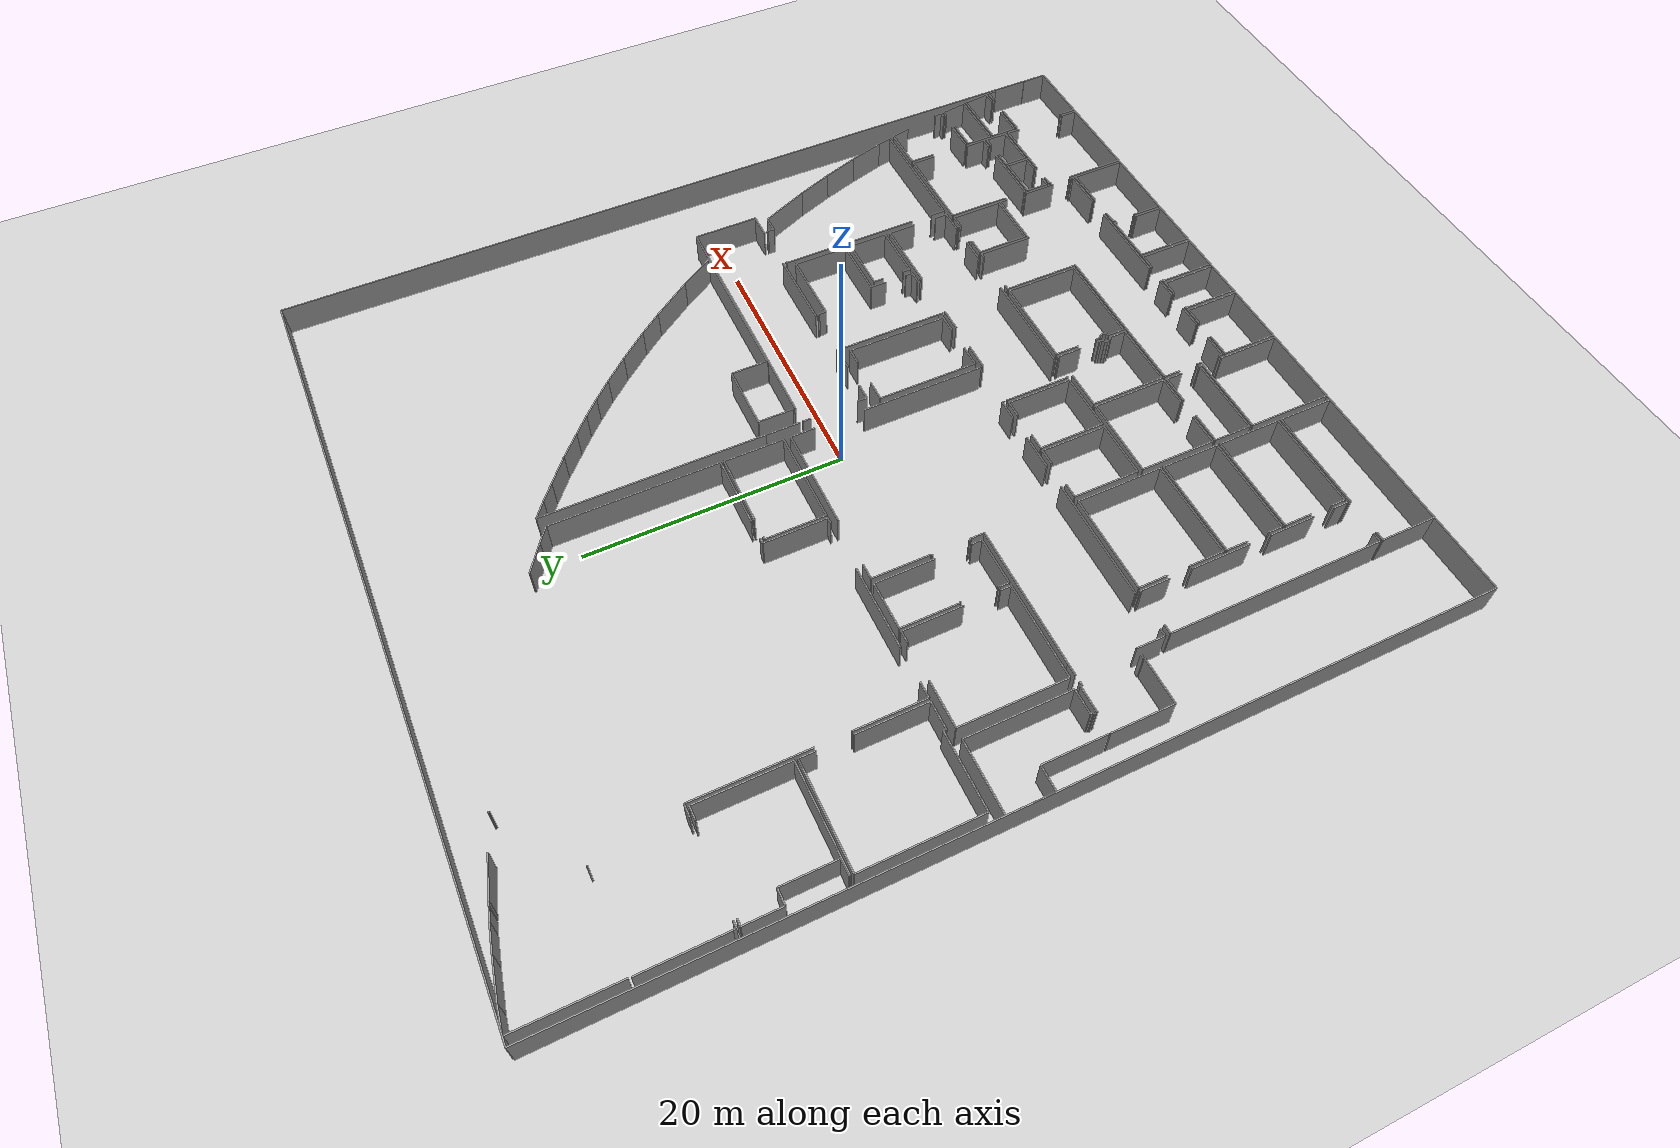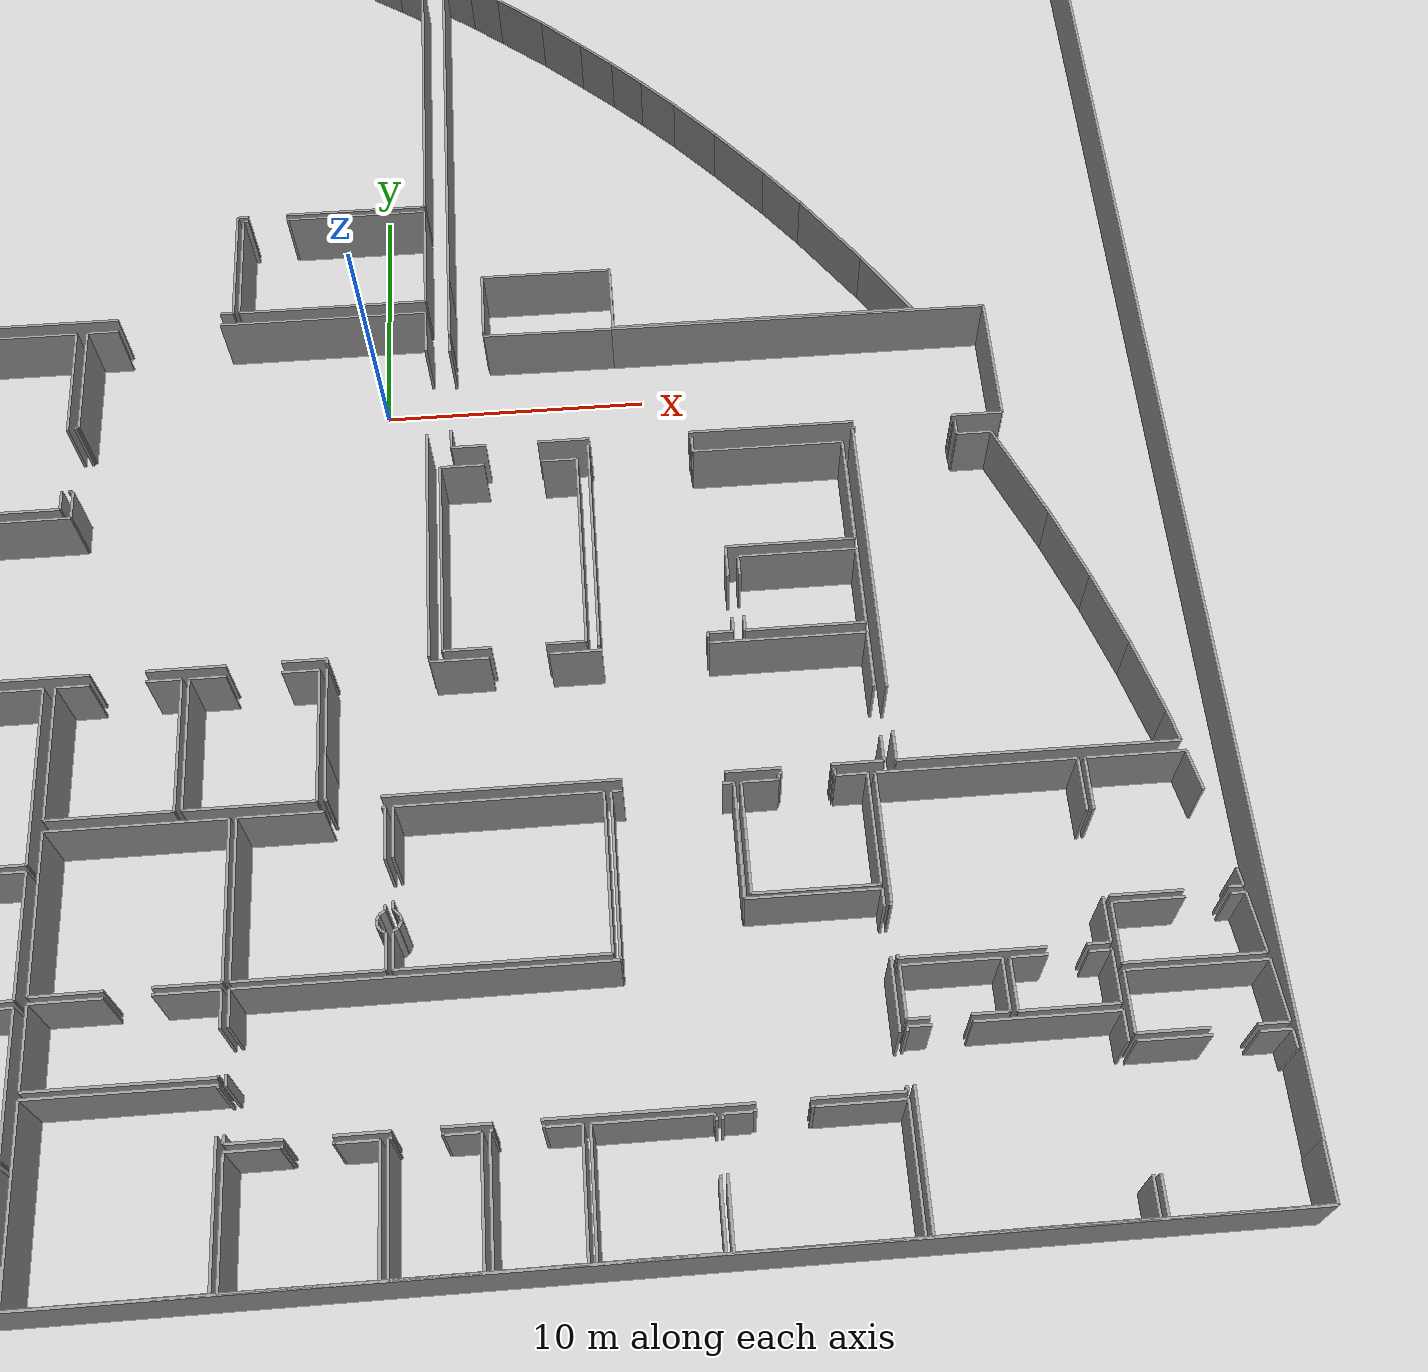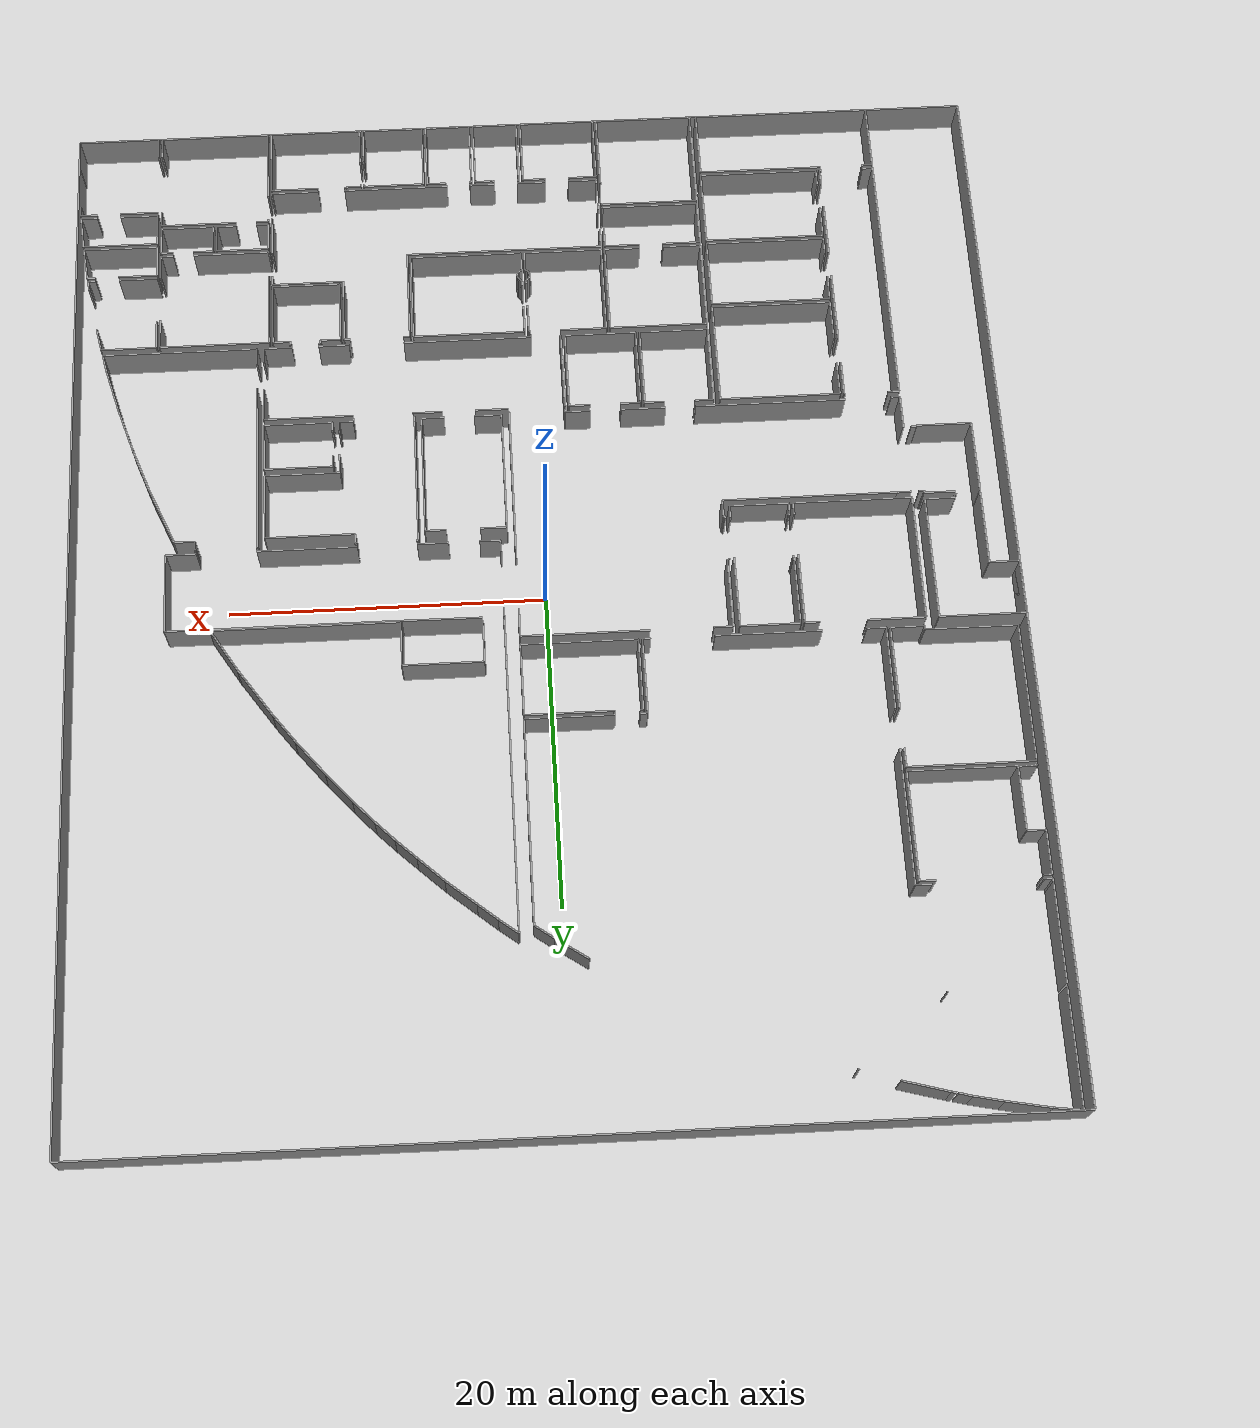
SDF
<sdf version="1.6">
  <world name="default">
    <light name="sun" type="directional">
      <cast_shadows>1</cast_shadows>
      <pose frame="">0 0 10 0 -0 0</pose>
      <diffuse>0.8 0.8 0.8 1</diffuse>
      <specular>0.1 0.1 0.1 1</specular>
      <attenuation>
        <range>1000</range>
        <constant>0.9</constant>
        <linear>0.01</linear>
        <quadratic>0.001</quadratic>
      </attenuation>
      <direction>-0.5 0.5 -1</direction>
    </light>
    <model name="ground_plane">
      <static>1</static>
      <link name="link">
        <collision name="collision">
          <geometry>
            <plane>
              <normal>0 0 1</normal>
              <size>100 100</size>
            </plane>
          </geometry>
          <surface>
            <friction>
              <ode>
                <mu>100</mu>
                <mu2>50</mu2>
              </ode>
              <torsional>
                <ode />
              </torsional>
            </friction>
            <contact>
              <ode />
            </contact>
            <bounce />
          </surface>
          <max_contacts>10</max_contacts>
        </collision>
        <visual name="visual">
          <cast_shadows>0</cast_shadows>
          <geometry>
            <plane>
              <normal>0 0 1</normal>
              <size>100 100</size>
            </plane>
          </geometry>
          <material>
            <script>
              <uri>file://media/materials/scripts/gazebo.material</uri>
              <name>Gazebo/Grey</name>
            </script>
          </material>
        </visual>
        <self_collide>0</self_collide>
        <kinematic>0</kinematic>
        <gravity>1</gravity>
      </link>
    </model>
    <gravity>0 0 -9.8</gravity>
    <magnetic_field>6e-06 2.3e-05 -4.2e-05</magnetic_field>
    <atmosphere type="adiabatic" />
    <physics default="0" name="default_physics" type="ode">
      <max_step_size>0.001</max_step_size>
      <real_time_factor>1</real_time_factor>
      <real_time_update_rate>1000</real_time_update_rate>
    </physics>
    <scene>
      <ambient>0.4 0.4 0.4 1</ambient>
      <background>0.7 0.7 0.7 1</background>
      <shadows>1</shadows>
    </scene>
    <spherical_coordinates>
      <surface_model>EARTH_WGS84</surface_model>
      <latitude_deg>0</latitude_deg>
      <longitude_deg>0</longitude_deg>
      <elevation>0</elevation>
      <heading_deg>0</heading_deg>
    </spherical_coordinates>
  <model name="50041192">
		<static>1</static>
		<link name="Wall_0">
			<collision name="Wall_0_Collision">
				<geometry>
					<box>
						<size>7.18817429759 0.1 2.5</size>
					</box>
				</geometry>
				<pose frame="">3.59408714879 0 1.25 0 0 0</pose>
			</collision>
			<visual name="Wall_0_Visual">
				<pose frame="">3.59408714879 0 1.25 0 0 0</pose>
				<geometry>
					<box>
						<size>7.18817429759 0.1 2.5</size>
					</box>
				</geometry>
				<material>
					<script>
						<uri>file://media/materials/scripts/gazebo.material</uri>
						<name>Gazebo/Grey</name>
					</script>
					<ambient>1 1 1 1</ambient>
				</material>
			</visual>
			<pose frame="">0.632839007281 -7.18817429759 0 0 0 1.57079632679</pose>
		</link>
		<link name="Wall_1">
			<collision name="Wall_1_Collision">
				<geometry>
					<box>
						<size>1.75687054855 0.1 2.5</size>
					</box>
				</geometry>
				<pose frame="">0.878435274276 0 1.25 0 0 0</pose>
			</collision>
			<visual name="Wall_1_Visual">
				<pose frame="">0.878435274276 0 1.25 0 0 0</pose>
				<geometry>
					<box>
						<size>1.75687054855 0.1 2.5</size>
					</box>
				</geometry>
				<material>
					<script>
						<uri>file://media/materials/scripts/gazebo.material</uri>
						<name>Gazebo/Grey</name>
					</script>
					<ambient>1 1 1 1</ambient>
				</material>
			</visual>
			<pose frame="">0.632839007281 -0.0 0 0 0 -0.12982228404</pose>
		</link>
		<link name="Wall_2">
			<collision name="Wall_2_Collision">
				<geometry>
					<box>
						<size>2.73227401978 0.1 2.5</size>
					</box>
				</geometry>
				<pose frame="">1.36613700989 0 1.25 0 0 0</pose>
			</collision>
			<visual name="Wall_2_Visual">
				<pose frame="">1.36613700989 0 1.25 0 0 0</pose>
				<geometry>
					<box>
						<size>2.73227401978 0.1 2.5</size>
					</box>
				</geometry>
				<material>
					<script>
						<uri>file://media/materials/scripts/gazebo.material</uri>
						<name>Gazebo/Grey</name>
					</script>
					<ambient>1 1 1 1</ambient>
				</material>
			</visual>
			<pose frame="">2.37492534279 -0.227440814304 0 0 0 -0.186057639425</pose>
		</link>
		<link name="Wall_3">
			<collision name="Wall_3_Collision">
				<geometry>
					<box>
						<size>1.87062123023 0.1 2.5</size>
					</box>
				</geometry>
				<pose frame="">0.935310615117 0 1.25 0 0 0</pose>
			</collision>
			<visual name="Wall_3_Visual">
				<pose frame="">0.935310615117 0 1.25 0 0 0</pose>
				<geometry>
					<box>
						<size>1.87062123023 0.1 2.5</size>
					</box>
				</geometry>
				<material>
					<script>
						<uri>file://media/materials/scripts/gazebo.material</uri>
						<name>Gazebo/Grey</name>
					</script>
					<ambient>1 1 1 1</ambient>
				</material>
			</visual>
			<pose frame="">5.06004346003 -0.73287331783 0 0 0 -0.208720073857</pose>
		</link>
		<link name="Wall_4">
			<collision name="Wall_4_Collision">
				<geometry>
					<box>
						<size>0.804798564311 0.1 2.5</size>
					</box>
				</geometry>
				<pose frame="">0.402399282156 0 1.25 0 0 0</pose>
			</collision>
			<visual name="Wall_4_Visual">
				<pose frame="">0.402399282156 0 1.25 0 0 0</pose>
				<geometry>
					<box>
						<size>0.804798564311 0.1 2.5</size>
					</box>
				</geometry>
				<material>
					<script>
						<uri>file://media/materials/scripts/gazebo.material</uri>
						<name>Gazebo/Grey</name>
					</script>
					<ambient>1 1 1 1</ambient>
				</material>
			</visual>
			<pose frame="">6.8900664608 -1.12048085598 0 0 0 -0.263867322598</pose>
		</link>
		<link name="Wall_5">
			<collision name="Wall_5_Collision">
				<geometry>
					<box>
						<size>0.0614808068669 0.1 2.5</size>
					</box>
				</geometry>
				<pose frame="">0.0307404034334 0 1.25 0 0 0</pose>
			</collision>
			<visual name="Wall_5_Visual">
				<pose frame="">0.0307404034334 0 1.25 0 0 0</pose>
				<geometry>
					<box>
						<size>0.0614808068669 0.1 2.5</size>
					</box>
				</geometry>
				<material>
					<script>
						<uri>file://media/materials/scripts/gazebo.material</uri>
						<name>Gazebo/Grey</name>
					</script>
					<ambient>1 1 1 1</ambient>
				</material>
			</visual>
			<pose frame="">7.66700977215 -7.18461616662 0 0 0 -3.08368644834</pose>
		</link>
		<link name="Wall_6">
			<collision name="Wall_6_Collision">
				<geometry>
					<box>
						<size>2.91367959298 0.1 2.5</size>
					</box>
				</geometry>
				<pose frame="">1.45683979649 0 1.25 0 0 0</pose>
			</collision>
			<visual name="Wall_6_Visual">
				<pose frame="">1.45683979649 0 1.25 0 0 0</pose>
				<geometry>
					<box>
						<size>2.91367959298 0.1 2.5</size>
					</box>
				</geometry>
				<material>
					<script>
						<uri>file://media/materials/scripts/gazebo.material</uri>
						<name>Gazebo/Grey</name>
					</script>
					<ambient>1 1 1 1</ambient>
				</material>
			</visual>
			<pose frame="">8.08483600829 -1.42307447931 0 0 0 -0.268842455313</pose>
		</link>
		<link name="Wall_7">
			<collision name="Wall_7_Collision">
				<geometry>
					<box>
						<size>0.12458212514 0.1 2.5</size>
					</box>
				</geometry>
				<pose frame="">0.0622910625701 0 1.25 0 0 0</pose>
			</collision>
			<visual name="Wall_7_Visual">
				<pose frame="">0.0622910625701 0 1.25 0 0 0</pose>
				<geometry>
					<box>
						<size>0.12458212514 0.1 2.5</size>
					</box>
				</geometry>
				<material>
					<script>
						<uri>file://media/materials/scripts/gazebo.material</uri>
						<name>Gazebo/Grey</name>
					</script>
					<ambient>1 1 1 1</ambient>
				</material>
			</visual>
			<pose frame="">13.2101965867 -2.92520300408 0 0 0 -0.531760269162</pose>
		</link>
		<link name="Wall_8">
			<collision name="Wall_8_Collision">
				<geometry>
					<box>
						<size>0.301906292314 0.1 2.5</size>
					</box>
				</geometry>
				<pose frame="">0.150953146157 0 1.25 0 0 0</pose>
			</collision>
			<visual name="Wall_8_Visual">
				<pose frame="">0.150953146157 0 1.25 0 0 0</pose>
				<geometry>
					<box>
						<size>0.301906292314 0.1 2.5</size>
					</box>
				</geometry>
				<material>
					<script>
						<uri>file://media/materials/scripts/gazebo.material</uri>
						<name>Gazebo/Grey</name>
					</script>
					<ambient>1 1 1 1</ambient>
				</material>
			</visual>
			<pose frame="">7.79090897539 -1.35412298426 0 0 0 -0.230420648931</pose>
		</link>
		<link name="Wall_9">
			<collision name="Wall_9_Collision">
				<geometry>
					<box>
						<size>6.08961406987 0.1 2.5</size>
					</box>
				</geometry>
				<pose frame="">3.04480703493 0 1.25 0 0 0</pose>
			</collision>
			<visual name="Wall_9_Visual">
				<pose frame="">3.04480703493 0 1.25 0 0 0</pose>
				<geometry>
					<box>
						<size>6.08961406987 0.1 2.5</size>
					</box>
				</geometry>
				<material>
					<script>
						<uri>file://media/materials/scripts/gazebo.material</uri>
						<name>Gazebo/Grey</name>
					</script>
					<ambient>1 1 1 1</ambient>
				</material>
			</visual>
			<pose frame="">0.612760982552 -13.4373959564 0 0 0 1.57079632679</pose>
		</link>
		<link name="Wall_10">
			<collision name="Wall_10_Collision">
				<geometry>
					<box>
						<size>0.501061085484 0.1 2.5</size>
					</box>
				</geometry>
				<pose frame="">0.250530542742 0 1.25 0 0 0</pose>
			</collision>
			<visual name="Wall_10_Visual">
				<pose frame="">0.250530542742 0 1.25 0 0 0</pose>
				<geometry>
					<box>
						<size>0.501061085484 0.1 2.5</size>
					</box>
				</geometry>
				<material>
					<script>
						<uri>file://media/materials/scripts/gazebo.material</uri>
						<name>Gazebo/Grey</name>
					</script>
					<ambient>1 1 1 1</ambient>
				</material>
			</visual>
			<pose frame="">1.11623651405 -13.6559668586 0 0 0 3.14159265359</pose>
		</link>
		<link name="Wall_11">
			<collision name="Wall_11_Collision">
				<geometry>
					<box>
						<size>0.218584237309 0.1 2.5</size>
					</box>
				</geometry>
				<pose frame="">0.109292118655 0 1.25 0 0 0</pose>
			</collision>
			<visual name="Wall_11_Visual">
				<pose frame="">0.109292118655 0 1.25 0 0 0</pose>
				<geometry>
					<box>
						<size>0.218584237309 0.1 2.5</size>
					</box>
				</geometry>
				<material>
					<script>
						<uri>file://media/materials/scripts/gazebo.material</uri>
						<name>Gazebo/Grey</name>
					</script>
					<ambient>1 1 1 1</ambient>
				</material>
			</visual>
			<pose frame="">0.615175428564 -13.6559668586 0 0 0 1.58184238914</pose>
		</link>
		<link name="Wall_12">
			<collision name="Wall_12_Collision">
				<geometry>
					<box>
						<size>0.0498138335049 0.1 2.5</size>
					</box>
				</geometry>
				<pose frame="">0.0249069167524 0 1.25 0 0 0</pose>
			</collision>
			<visual name="Wall_12_Visual">
				<pose frame="">0.0249069167524 0 1.25 0 0 0</pose>
				<geometry>
					<box>
						<size>0.0498138335049 0.1 2.5</size>
					</box>
				</geometry>
				<material>
					<script>
						<uri>file://media/materials/scripts/gazebo.material</uri>
						<name>Gazebo/Grey</name>
					</script>
					<ambient>1 1 1 1</ambient>
				</material>
			</visual>
			<pose frame="">0.622291690493 -20.7590128728 0 0 0 1.57079632679</pose>
		</link>
		<link name="Wall_13">
			<collision name="Wall_13_Collision">
				<geometry>
					<box>
						<size>1.17329368559 0.1 2.5</size>
					</box>
				</geometry>
				<pose frame="">0.586646842794 0 1.25 0 0 0</pose>
			</collision>
			<visual name="Wall_13_Visual">
				<pose frame="">0.586646842794 0 1.25 0 0 0</pose>
				<geometry>
					<box>
						<size>1.17329368559 0.1 2.5</size>
					</box>
				</geometry>
				<material>
					<script>
						<uri>file://media/materials/scripts/gazebo.material</uri>
						<name>Gazebo/Grey</name>
					</script>
					<ambient>1 1 1 1</ambient>
				</material>
			</visual>
			<pose frame="">0.622291690493 -20.7091990393 0 0 0 0.0</pose>
		</link>
		<link name="Wall_14">
			<collision name="Wall_14_Collision">
				<geometry>
					<box>
						<size>4.04254508025 0.1 2.5</size>
					</box>
				</geometry>
				<pose frame="">2.02127254012 0 1.25 0 0 0</pose>
			</collision>
			<visual name="Wall_14_Visual">
				<pose frame="">2.02127254012 0 1.25 0 0 0</pose>
				<geometry>
					<box>
						<size>4.04254508025 0.1 2.5</size>
					</box>
				</geometry>
				<material>
					<script>
						<uri>file://media/materials/scripts/gazebo.material</uri>
						<name>Gazebo/Grey</name>
					</script>
					<ambient>1 1 1 1</ambient>
				</material>
			</visual>
			<pose frame="">1.79558537608 -20.7091990393 0 0 0 1.57079632679</pose>
		</link>
		<link name="Wall_15">
			<collision name="Wall_15_Collision">
				<geometry>
					<box>
						<size>1.1757081316 0.1 2.5</size>
					</box>
				</geometry>
				<pose frame="">0.5878540658 0 1.25 0 0 0</pose>
			</collision>
			<visual name="Wall_15_Visual">
				<pose frame="">0.5878540658 0 1.25 0 0 0</pose>
				<geometry>
					<box>
						<size>1.1757081316 0.1 2.5</size>
					</box>
				</geometry>
				<material>
					<script>
						<uri>file://media/materials/scripts/gazebo.material</uri>
						<name>Gazebo/Grey</name>
					</script>
					<ambient>1 1 1 1</ambient>
				</material>
			</visual>
			<pose frame="">1.79558537608 -16.6666539591 0 0 0 3.14159265359</pose>
		</link>
		<link name="Wall_16">
			<collision name="Wall_16_Collision">
				<geometry>
					<box>
						<size>2.77407139136 0.1 2.5</size>
					</box>
				</geometry>
				<pose frame="">1.38703569568 0 1.25 0 0 0</pose>
			</collision>
			<visual name="Wall_16_Visual">
				<pose frame="">1.38703569568 0 1.25 0 0 0</pose>
				<geometry>
					<box>
						<size>2.77407139136 0.1 2.5</size>
					</box>
				</geometry>
				<material>
					<script>
						<uri>file://media/materials/scripts/gazebo.material</uri>
						<name>Gazebo/Grey</name>
					</script>
					<ambient>1 1 1 1</ambient>
				</material>
			</visual>
			<pose frame="">0.619877244482 -16.6666539591 0 0 0 1.57079632679</pose>
		</link>
		<link name="Wall_17">
			<collision name="Wall_17_Collision">
				<geometry>
					<box>
						<size>0.510718869531 0.1 2.5</size>
					</box>
				</geometry>
				<pose frame="">0.255359434765 0 1.25 0 0 0</pose>
			</collision>
			<visual name="Wall_17_Visual">
				<pose frame="">0.255359434765 0 1.25 0 0 0</pose>
				<geometry>
					<box>
						<size>0.510718869531 0.1 2.5</size>
					</box>
				</geometry>
				<material>
					<script>
						<uri>file://media/materials/scripts/gazebo.material</uri>
						<name>Gazebo/Grey</name>
					</script>
					<ambient>1 1 1 1</ambient>
				</material>
			</visual>
			<pose frame="">0.619877244482 -13.8925825677 0 0 0 0.0</pose>
		</link>
		<link name="Wall_18">
			<collision name="Wall_18_Collision">
				<geometry>
					<box>
						<size>1.01838791252 0.1 2.5</size>
					</box>
				</geometry>
				<pose frame="">0.50919395626 0 1.25 0 0 0</pose>
			</collision>
			<visual name="Wall_18_Visual">
				<pose frame="">0.50919395626 0 1.25 0 0 0</pose>
				<geometry>
					<box>
						<size>1.01838791252 0.1 2.5</size>
					</box>
				</geometry>
				<material>
					<script>
						<uri>file://media/materials/scripts/gazebo.material</uri>
						<name>Gazebo/Grey</name>
					</script>
					<ambient>1 1 1 1</ambient>
				</material>
			</visual>
			<pose frame="">7.54539793883 -13.8925825677 0 0 0 0.0</pose>
		</link>
		<link name="Wall_19">
			<collision name="Wall_19_Collision">
				<geometry>
					<box>
						<size>6.8575349777 0.1 2.5</size>
					</box>
				</geometry>
				<pose frame="">3.42876748885 0 1.25 0 0 0</pose>
			</collision>
			<visual name="Wall_19_Visual">
				<pose frame="">3.42876748885 0 1.25 0 0 0</pose>
				<geometry>
					<box>
						<size>6.8575349777 0.1 2.5</size>
					</box>
				</geometry>
				<material>
					<script>
						<uri>file://media/materials/scripts/gazebo.material</uri>
						<name>Gazebo/Grey</name>
					</script>
					<ambient>1 1 1 1</ambient>
				</material>
			</visual>
			<pose frame="">8.56378585135 -13.8925825677 0 0 0 -1.57079632679</pose>
		</link>
		<link name="Wall_20">
			<collision name="Wall_20_Collision">
				<geometry>
					<box>
						<size>7.94149914271 0.1 2.5</size>
					</box>
				</geometry>
				<pose frame="">3.97074957136 0 1.25 0 0 0</pose>
			</collision>
			<visual name="Wall_20_Visual">
				<pose frame="">3.97074957136 0 1.25 0 0 0</pose>
				<geometry>
					<box>
						<size>7.94149914271 0.1 2.5</size>
					</box>
				</geometry>
				<material>
					<script>
						<uri>file://media/materials/scripts/gazebo.material</uri>
						<name>Gazebo/Grey</name>
					</script>
					<ambient>1 1 1 1</ambient>
				</material>
			</visual>
			<pose frame="">8.56378585135 -20.7501175454 0 0 0 -3.14047254653</pose>
		</link>
		<link name="Wall_21">
			<collision name="Wall_21_Collision">
				<geometry>
					<box>
						<size>8.85262984001 0.1 2.5</size>
					</box>
				</geometry>
				<pose frame="">4.42631492001 0 1.25 0 0 0</pose>
			</collision>
			<visual name="Wall_21_Visual">
				<pose frame="">4.42631492001 0 1.25 0 0 0</pose>
				<geometry>
					<box>
						<size>8.85262984001 0.1 2.5</size>
					</box>
				</geometry>
				<material>
					<script>
						<uri>file://media/materials/scripts/gazebo.material</uri>
						<name>Gazebo/Grey</name>
					</script>
					<ambient>1 1 1 1</ambient>
				</material>
			</visual>
			<pose frame="">0.62610397367 -29.8576620538 0 0 0 1.57079632679</pose>
		</link>
		<link name="Wall_22">
			<collision name="Wall_22_Collision">
				<geometry>
					<box>
						<size>7.93755480157 0.1 2.5</size>
					</box>
				</geometry>
				<pose frame="">3.96877740079 0 1.25 0 0 0</pose>
			</collision>
			<visual name="Wall_22_Visual">
				<pose frame="">3.96877740079 0 1.25 0 0 0</pose>
				<geometry>
					<box>
						<size>7.93755480157 0.1 2.5</size>
					</box>
				</geometry>
				<material>
					<script>
						<uri>file://media/materials/scripts/gazebo.material</uri>
						<name>Gazebo/Grey</name>
					</script>
					<ambient>1 1 1 1</ambient>
				</material>
			</visual>
			<pose frame="">0.62610397367 -21.0050322138 0 0 0 0.0</pose>
		</link>
		<link name="Wall_23">
			<collision name="Wall_23_Collision">
				<geometry>
					<box>
						<size>1.21344973505 0.1 2.5</size>
					</box>
				</geometry>
				<pose frame="">0.606724867523 0 1.25 0 0 0</pose>
			</collision>
			<visual name="Wall_23_Visual">
				<pose frame="">0.606724867523 0 1.25 0 0 0</pose>
				<geometry>
					<box>
						<size>1.21344973505 0.1 2.5</size>
					</box>
				</geometry>
				<material>
					<script>
						<uri>file://media/materials/scripts/gazebo.material</uri>
						<name>Gazebo/Grey</name>
					</script>
					<ambient>1 1 1 1</ambient>
				</material>
			</visual>
			<pose frame="">8.56365877524 -21.0050322138 0 0 0 -1.57079632679</pose>
		</link>
		<link name="Wall_24">
			<collision name="Wall_24_Collision">
				<geometry>
					<box>
						<size>5.33643399032 0.1 2.5</size>
					</box>
				</geometry>
				<pose frame="">2.66821699516 0 1.25 0 0 0</pose>
			</collision>
			<visual name="Wall_24_Visual">
				<pose frame="">2.66821699516 0 1.25 0 0 0</pose>
				<geometry>
					<box>
						<size>5.33643399032 0.1 2.5</size>
					</box>
				</geometry>
				<material>
					<script>
						<uri>file://media/materials/scripts/gazebo.material</uri>
						<name>Gazebo/Grey</name>
					</script>
					<ambient>1 1 1 1</ambient>
				</material>
			</visual>
			<pose frame="">8.56365877524 -24.7532690328 0 0 0 -1.57079632679</pose>
		</link>
		<link name="Wall_25">
			<collision name="Wall_25_Collision">
				<geometry>
					<box>
						<size>2.12865184959 0.1 2.5</size>
					</box>
				</geometry>
				<pose frame="">1.0643259248 0 1.25 0 0 0</pose>
			</collision>
			<visual name="Wall_25_Visual">
				<pose frame="">1.0643259248 0 1.25 0 0 0</pose>
				<geometry>
					<box>
						<size>2.12865184959 0.1 2.5</size>
					</box>
				</geometry>
				<material>
					<script>
						<uri>file://media/materials/scripts/gazebo.material</uri>
						<name>Gazebo/Grey</name>
					</script>
					<ambient>1 1 1 1</ambient>
				</material>
			</visual>
			<pose frame="">8.56365877524 -30.0897030231 0 0 0 3.14159265359</pose>
		</link>
		<link name="Wall_26">
			<collision name="Wall_26_Collision">
				<geometry>
					<box>
						<size>0.224289326878 0.1 2.5</size>
					</box>
				</geometry>
				<pose frame="">0.112144663439 0 1.25 0 0 0</pose>
			</collision>
			<visual name="Wall_26_Visual">
				<pose frame="">0.112144663439 0 1.25 0 0 0</pose>
				<geometry>
					<box>
						<size>0.224289326878 0.1 2.5</size>
					</box>
				</geometry>
				<material>
					<script>
						<uri>file://media/materials/scripts/gazebo.material</uri>
						<name>Gazebo/Grey</name>
					</script>
					<ambient>1 1 1 1</ambient>
				</material>
			</visual>
			<pose frame="">6.43500692565 -30.0897030231 0 0 0 1.57079632679</pose>
		</link>
		<link name="Wall_27">
			<collision name="Wall_27_Collision">
				<geometry>
					<box>
						<size>5.80890812403 0.1 2.5</size>
					</box>
				</geometry>
				<pose frame="">2.90445406202 0 1.25 0 0 0</pose>
			</collision>
			<visual name="Wall_27_Visual">
				<pose frame="">2.90445406202 0 1.25 0 0 0</pose>
				<geometry>
					<box>
						<size>5.80890812403 0.1 2.5</size>
					</box>
				</geometry>
				<material>
					<script>
						<uri>file://media/materials/scripts/gazebo.material</uri>
						<name>Gazebo/Grey</name>
					</script>
					<ambient>1 1 1 1</ambient>
				</material>
			</visual>
			<pose frame="">6.43500692565 -29.8654136963 0 0 0 3.14025821266</pose>
		</link>
		<link name="Wall_28">
			<collision name="Wall_28_Collision">
				<geometry>
					<box>
						<size>5.35956184159 0.1 2.5</size>
					</box>
				</geometry>
				<pose frame="">2.67978092079 0 1.25 0 0 0</pose>
			</collision>
			<visual name="Wall_28_Visual">
				<pose frame="">2.67978092079 0 1.25 0 0 0</pose>
				<geometry>
					<box>
						<size>5.35956184159 0.1 2.5</size>
					</box>
				</geometry>
				<material>
					<script>
						<uri>file://media/materials/scripts/gazebo.material</uri>
						<name>Gazebo/Grey</name>
					</script>
					<ambient>1 1 1 1</ambient>
				</material>
			</visual>
			<pose frame="">8.81221963834 -30.1052063081 0 0 0 1.57079632679</pose>
		</link>
		<link name="Wall_29">
			<collision name="Wall_29_Collision">
				<geometry>
					<box>
						<size>8.53328758594 0.1 2.5</size>
					</box>
				</geometry>
				<pose frame="">4.26664379297 0 1.25 0 0 0</pose>
			</collision>
			<visual name="Wall_29_Visual">
				<pose frame="">4.26664379297 0 1.25 0 0 0</pose>
				<geometry>
					<box>
						<size>8.53328758594 0.1 2.5</size>
					</box>
				</geometry>
				<material>
					<script>
						<uri>file://media/materials/scripts/gazebo.material</uri>
						<name>Gazebo/Grey</name>
					</script>
					<ambient>1 1 1 1</ambient>
				</material>
			</visual>
			<pose frame="">8.81221963834 -22.1926854993 0 0 0 1.57079632679</pose>
		</link>
		<link name="Wall_30">
			<collision name="Wall_30_Collision">
				<geometry>
					<box>
						<size>0.975054960416 0.1 2.5</size>
					</box>
				</geometry>
				<pose frame="">0.487527480208 0 1.25 0 0 0</pose>
			</collision>
			<visual name="Wall_30_Visual">
				<pose frame="">0.487527480208 0 1.25 0 0 0</pose>
				<geometry>
					<box>
						<size>0.975054960416 0.1 2.5</size>
					</box>
				</geometry>
				<material>
					<script>
						<uri>file://media/materials/scripts/gazebo.material</uri>
						<name>Gazebo/Grey</name>
					</script>
					<ambient>1 1 1 1</ambient>
				</material>
			</visual>
			<pose frame="">8.81221963834 -13.6593979134 0 0 0 3.14159265359</pose>
		</link>
		<link name="Wall_31">
			<collision name="Wall_31_Collision">
				<geometry>
					<box>
						<size>2.39887418967 0.1 2.5</size>
					</box>
				</geometry>
				<pose frame="">1.19943709484 0 1.25 0 0 0</pose>
			</collision>
			<visual name="Wall_31_Visual">
				<pose frame="">1.19943709484 0 1.25 0 0 0</pose>
				<geometry>
					<box>
						<size>2.39887418967 0.1 2.5</size>
					</box>
				</geometry>
				<material>
					<script>
						<uri>file://media/materials/scripts/gazebo.material</uri>
						<name>Gazebo/Grey</name>
					</script>
					<ambient>1 1 1 1</ambient>
				</material>
			</visual>
			<pose frame="">28.3542373528 -10.1845017981 0 0 0 -0.59238087215</pose>
		</link>
		<link name="Wall_32">
			<collision name="Wall_32_Collision">
				<geometry>
					<box>
						<size>1.42702038407 0.1 2.5</size>
					</box>
				</geometry>
				<pose frame="">0.713510192037 0 1.25 0 0 0</pose>
			</collision>
			<visual name="Wall_32_Visual">
				<pose frame="">0.713510192037 0 1.25 0 0 0</pose>
				<geometry>
					<box>
						<size>1.42702038407 0.1 2.5</size>
					</box>
				</geometry>
				<material>
					<script>
						<uri>file://media/materials/scripts/gazebo.material</uri>
						<name>Gazebo/Grey</name>
					</script>
					<ambient>1 1 1 1</ambient>
				</material>
			</visual>
			<pose frame="">30.3443762469 -11.5238839541 0 0 0 -0.618707060109</pose>
		</link>
		<link name="Wall_33">
			<collision name="Wall_33_Collision">
				<geometry>
					<box>
						<size>12.8781467221 0.1 2.5</size>
					</box>
				</geometry>
				<pose frame="">6.43907336104 0 1.25 0 0 0</pose>
			</collision>
			<visual name="Wall_33_Visual">
				<pose frame="">6.43907336104 0 1.25 0 0 0</pose>
				<geometry>
					<box>
						<size>12.8781467221 0.1 2.5</size>
					</box>
				</geometry>
				<material>
					<script>
						<uri>file://media/materials/scripts/gazebo.material</uri>
						<name>Gazebo/Grey</name>
					</script>
					<ambient>1 1 1 1</ambient>
				</material>
			</visual>
			<pose frame="">31.5068684635 -12.3515306317 0 0 0 -1.57079632679</pose>
		</link>
		<link name="Wall_34">
			<collision name="Wall_34_Collision">
				<geometry>
					<box>
						<size>5.59884614896 0.1 2.5</size>
					</box>
				</geometry>
				<pose frame="">2.79942307448 0 1.25 0 0 0</pose>
			</collision>
			<visual name="Wall_34_Visual">
				<pose frame="">2.79942307448 0 1.25 0 0 0</pose>
				<geometry>
					<box>
						<size>5.59884614896 0.1 2.5</size>
					</box>
				</geometry>
				<material>
					<script>
						<uri>file://media/materials/scripts/gazebo.material</uri>
						<name>Gazebo/Grey</name>
					</script>
					<ambient>1 1 1 1</ambient>
				</material>
			</visual>
			<pose frame="">31.5068684635 -25.2296773538 0 0 0 3.14159265359</pose>
		</link>
		<link name="Wall_35">
			<collision name="Wall_35_Collision">
				<geometry>
					<box>
						<size>0.44197069625 0.1 2.5</size>
					</box>
				</geometry>
				<pose frame="">0.220985348125 0 1.25 0 0 0</pose>
			</collision>
			<visual name="Wall_35_Visual">
				<pose frame="">0.220985348125 0 1.25 0 0 0</pose>
				<geometry>
					<box>
						<size>0.44197069625 0.1 2.5</size>
					</box>
				</geometry>
				<material>
					<script>
						<uri>file://media/materials/scripts/gazebo.material</uri>
						<name>Gazebo/Grey</name>
					</script>
					<ambient>1 1 1 1</ambient>
				</material>
			</visual>
			<pose frame="">24.3843798051 -25.2296773538 0 0 0 3.14159265359</pose>
		</link>
		<link name="Wall_36">
			<collision name="Wall_36_Collision">
				<geometry>
					<box>
						<size>4.86841269236 0.1 2.5</size>
					</box>
				</geometry>
				<pose frame="">2.43420634618 0 1.25 0 0 0</pose>
			</collision>
			<visual name="Wall_36_Visual">
				<pose frame="">2.43420634618 0 1.25 0 0 0</pose>
				<geometry>
					<box>
						<size>4.86841269236 0.1 2.5</size>
					</box>
				</geometry>
				<material>
					<script>
						<uri>file://media/materials/scripts/gazebo.material</uri>
						<name>Gazebo/Grey</name>
					</script>
					<ambient>1 1 1 1</ambient>
				</material>
			</visual>
			<pose frame="">23.9424091088 -25.2296773538 0 0 0 -1.57079632679</pose>
		</link>
		<link name="Wall_37">
			<collision name="Wall_37_Collision">
				<geometry>
					<box>
						<size>0.509321032366 0.1 2.5</size>
					</box>
				</geometry>
				<pose frame="">0.254660516183 0 1.25 0 0 0</pose>
			</collision>
			<visual name="Wall_37_Visual">
				<pose frame="">0.254660516183 0 1.25 0 0 0</pose>
				<geometry>
					<box>
						<size>0.509321032366 0.1 2.5</size>
					</box>
				</geometry>
				<material>
					<script>
						<uri>file://media/materials/scripts/gazebo.material</uri>
						<name>Gazebo/Grey</name>
					</script>
					<ambient>1 1 1 1</ambient>
				</material>
			</visual>
			<pose frame="">23.9424091088 -30.0980900461 0 0 0 3.14159265359</pose>
		</link>
		<link name="Wall_38">
			<collision name="Wall_38_Collision">
				<geometry>
					<box>
						<size>6.66437929676 0.1 2.5</size>
					</box>
				</geometry>
				<pose frame="">3.33218964838 0 1.25 0 0 0</pose>
			</collision>
			<visual name="Wall_38_Visual">
				<pose frame="">3.33218964838 0 1.25 0 0 0</pose>
				<geometry>
					<box>
						<size>6.66437929676 0.1 2.5</size>
					</box>
				</geometry>
				<material>
					<script>
						<uri>file://media/materials/scripts/gazebo.material</uri>
						<name>Gazebo/Grey</name>
					</script>
					<ambient>1 1 1 1</ambient>
				</material>
			</visual>
			<pose frame="">19.4511582987 -30.0980900461 0 0 0 3.14159265359</pose>
		</link>
		<link name="Wall_39">
			<collision name="Wall_39_Collision">
				<geometry>
					<box>
						<size>1.22376359055 0.1 2.5</size>
					</box>
				</geometry>
				<pose frame="">0.611881795276 0 1.25 0 0 0</pose>
			</collision>
			<visual name="Wall_39_Visual">
				<pose frame="">0.611881795276 0 1.25 0 0 0</pose>
				<geometry>
					<box>
						<size>1.22376359055 0.1 2.5</size>
					</box>
				</geometry>
				<material>
					<script>
						<uri>file://media/materials/scripts/gazebo.material</uri>
						<name>Gazebo/Grey</name>
					</script>
					<ambient>1 1 1 1</ambient>
				</material>
			</visual>
			<pose frame="">10.035962538 -30.0980900461 0 0 0 -3.13577755818</pose>
		</link>
		<link name="Wall_40">
			<collision name="Wall_40_Collision">
				<geometry>
					<box>
						<size>4.64069231062 0.1 2.5</size>
					</box>
				</geometry>
				<pose frame="">2.32034615531 0 1.25 0 0 0</pose>
			</collision>
			<visual name="Wall_40_Visual">
				<pose frame="">2.32034615531 0 1.25 0 0 0</pose>
				<geometry>
					<box>
						<size>4.64069231062 0.1 2.5</size>
					</box>
				</geometry>
				<material>
					<script>
						<uri>file://media/materials/scripts/gazebo.material</uri>
						<name>Gazebo/Grey</name>
					</script>
					<ambient>1 1 1 1</ambient>
				</material>
			</visual>
			<pose frame="">24.1813121879 -30.1007586444 0 0 0 1.57079632679</pose>
		</link>
		<link name="Wall_41">
			<collision name="Wall_41_Collision">
				<geometry>
					<box>
						<size>0.213614933984 0.1 2.5</size>
					</box>
				</geometry>
				<pose frame="">0.106807466992 0 1.25 0 0 0</pose>
			</collision>
			<visual name="Wall_41_Visual">
				<pose frame="">0.106807466992 0 1.25 0 0 0</pose>
				<geometry>
					<box>
						<size>0.213614933984 0.1 2.5</size>
					</box>
				</geometry>
				<material>
					<script>
						<uri>file://media/materials/scripts/gazebo.material</uri>
						<name>Gazebo/Grey</name>
					</script>
					<ambient>1 1 1 1</ambient>
				</material>
			</visual>
			<pose frame="">24.1813121879 -25.4600663337 0 0 0 0.0</pose>
		</link>
		<link name="Wall_42">
			<collision name="Wall_42_Collision">
				<geometry>
					<box>
						<size>0.0908594157041 0.1 2.5</size>
					</box>
				</geometry>
				<pose frame="">0.045429707852 0 1.25 0 0 0</pose>
			</collision>
			<visual name="Wall_42_Visual">
				<pose frame="">0.045429707852 0 1.25 0 0 0</pose>
				<geometry>
					<box>
						<size>0.0908594157041 0.1 2.5</size>
					</box>
				</geometry>
				<material>
					<script>
						<uri>file://media/materials/scripts/gazebo.material</uri>
						<name>Gazebo/Grey</name>
					</script>
					<ambient>1 1 1 1</ambient>
				</material>
			</visual>
			<pose frame="">25.9293711004 -25.4600663337 0 0 0 0.0</pose>
		</link>
		<link name="Wall_43">
			<collision name="Wall_43_Collision">
				<geometry>
					<box>
						<size>0.0198238725173 0.1 2.5</size>
					</box>
				</geometry>
				<pose frame="">0.00991193625863 0 1.25 0 0 0</pose>
			</collision>
			<visual name="Wall_43_Visual">
				<pose frame="">0.00991193625863 0 1.25 0 0 0</pose>
				<geometry>
					<box>
						<size>0.0198238725173 0.1 2.5</size>
					</box>
				</geometry>
				<material>
					<script>
						<uri>file://media/materials/scripts/gazebo.material</uri>
						<name>Gazebo/Grey</name>
					</script>
					<ambient>1 1 1 1</ambient>
				</material>
			</visual>
			<pose frame="">26.0202305161 -25.4600663337 0 0 0 -1.57079632679</pose>
		</link>
		<link name="Wall_44">
			<collision name="Wall_44_Collision">
				<geometry>
					<box>
						<size>5.476471859 0.1 2.5</size>
					</box>
				</geometry>
				<pose frame="">2.7382359295 0 1.25 0 0 0</pose>
			</collision>
			<visual name="Wall_44_Visual">
				<pose frame="">2.7382359295 0 1.25 0 0 0</pose>
				<geometry>
					<box>
						<size>5.476471859 0.1 2.5</size>
					</box>
				</geometry>
				<material>
					<script>
						<uri>file://media/materials/scripts/gazebo.material</uri>
						<name>Gazebo/Grey</name>
					</script>
					<ambient>1 1 1 1</ambient>
				</material>
			</visual>
			<pose frame="">26.0202305161 -25.4798902062 0 0 0 0.0</pose>
		</link>
		<link name="Wall_45">
			<collision name="Wall_45_Collision">
				<geometry>
					<box>
						<size>4.61603954608 0.1 2.5</size>
					</box>
				</geometry>
				<pose frame="">2.30801977304 0 1.25 0 0 0</pose>
			</collision>
			<visual name="Wall_45_Visual">
				<pose frame="">2.30801977304 0 1.25 0 0 0</pose>
				<geometry>
					<box>
						<size>4.61603954608 0.1 2.5</size>
					</box>
				</geometry>
				<material>
					<script>
						<uri>file://media/materials/scripts/gazebo.material</uri>
						<name>Gazebo/Grey</name>
					</script>
					<ambient>1 1 1 1</ambient>
				</material>
			</visual>
			<pose frame="">31.4967023751 -25.4798902062 0 0 0 -1.57079632679</pose>
		</link>
		<link name="Wall_46">
			<collision name="Wall_46_Collision">
				<geometry>
					<box>
						<size>7.31539178096 0.1 2.5</size>
					</box>
				</geometry>
				<pose frame="">3.65769589048 0 1.25 0 0 0</pose>
			</collision>
			<visual name="Wall_46_Visual">
				<pose frame="">3.65769589048 0 1.25 0 0 0</pose>
				<geometry>
					<box>
						<size>7.31539178096 0.1 2.5</size>
					</box>
				</geometry>
				<material>
					<script>
						<uri>file://media/materials/scripts/gazebo.material</uri>
						<name>Gazebo/Grey</name>
					</script>
					<ambient>1 1 1 1</ambient>
				</material>
			</visual>
			<pose frame="">31.4967023751 -30.0959297523 0 0 0 -3.14093255328</pose>
		</link>
		<link name="Wall_47">
			<collision name="Wall_47_Collision">
				<geometry>
					<box>
						<size>8.17760156558 0.1 2.5</size>
					</box>
				</geometry>
				<pose frame="">4.08880078279 0 1.25 0 0 0</pose>
			</collision>
			<visual name="Wall_47_Visual">
				<pose frame="">4.08880078279 0 1.25 0 0 0</pose>
				<geometry>
					<box>
						<size>8.17760156558 0.1 2.5</size>
					</box>
				</geometry>
				<material>
					<script>
						<uri>file://media/materials/scripts/gazebo.material</uri>
						<name>Gazebo/Grey</name>
					</script>
					<ambient>1 1 1 1</ambient>
				</material>
			</visual>
			<pose frame="">6.27717840215 -38.84257812 0 0 0 1.57079632679</pose>
		</link>
		<link name="Wall_48">
			<collision name="Wall_48_Collision">
				<geometry>
					<box>
						<size>3.64644885822 0.1 2.5</size>
					</box>
				</geometry>
				<pose frame="">1.82322442911 0 1.25 0 0 0</pose>
			</collision>
			<visual name="Wall_48_Visual">
				<pose frame="">1.82322442911 0 1.25 0 0 0</pose>
				<geometry>
					<box>
						<size>3.64644885822 0.1 2.5</size>
					</box>
				</geometry>
				<material>
					<script>
						<uri>file://media/materials/scripts/gazebo.material</uri>
						<name>Gazebo/Grey</name>
					</script>
					<ambient>1 1 1 1</ambient>
				</material>
			</visual>
			<pose frame="">6.27717840215 -30.6649765545 0 0 0 0.0</pose>
		</link>
		<link name="Wall_49">
			<collision name="Wall_49_Collision">
				<geometry>
					<box>
						<size>0.926384811864 0.1 2.5</size>
					</box>
				</geometry>
				<pose frame="">0.463192405932 0 1.25 0 0 0</pose>
			</collision>
			<visual name="Wall_49_Visual">
				<pose frame="">0.463192405932 0 1.25 0 0 0</pose>
				<geometry>
					<box>
						<size>0.926384811864 0.1 2.5</size>
					</box>
				</geometry>
				<material>
					<script>
						<uri>file://media/materials/scripts/gazebo.material</uri>
						<name>Gazebo/Grey</name>
					</script>
					<ambient>1 1 1 1</ambient>
				</material>
			</visual>
			<pose frame="">12.8988601273 -30.6649765545 0 0 0 0.0</pose>
		</link>
		<link name="Wall_50">
			<collision name="Wall_50_Collision">
				<geometry>
					<box>
						<size>4.58338098687 0.1 2.5</size>
					</box>
				</geometry>
				<pose frame="">2.29169049344 0 1.25 0 0 0</pose>
			</collision>
			<visual name="Wall_50_Visual">
				<pose frame="">2.29169049344 0 1.25 0 0 0</pose>
				<geometry>
					<box>
						<size>4.58338098687 0.1 2.5</size>
					</box>
				</geometry>
				<material>
					<script>
						<uri>file://media/materials/scripts/gazebo.material</uri>
						<name>Gazebo/Grey</name>
					</script>
					<ambient>1 1 1 1</ambient>
				</material>
			</visual>
			<pose frame="">13.8252449392 -30.6649765545 0 0 0 -1.57079632679</pose>
		</link>
		<link name="Wall_51">
			<collision name="Wall_51_Collision">
				<geometry>
					<box>
						<size>0.834508787313 0.1 2.5</size>
					</box>
				</geometry>
				<pose frame="">0.417254393656 0 1.25 0 0 0</pose>
			</collision>
			<visual name="Wall_51_Visual">
				<pose frame="">0.417254393656 0 1.25 0 0 0</pose>
				<geometry>
					<box>
						<size>0.834508787313 0.1 2.5</size>
					</box>
				</geometry>
				<material>
					<script>
						<uri>file://media/materials/scripts/gazebo.material</uri>
						<name>Gazebo/Grey</name>
					</script>
					<ambient>1 1 1 1</ambient>
				</material>
			</visual>
			<pose frame="">13.8252449392 -38.0057819628 0 0 0 -1.57079632679</pose>
		</link>
		<link name="Wall_52">
			<collision name="Wall_52_Collision">
				<geometry>
					<box>
						<size>7.54806688363 0.1 2.5</size>
					</box>
				</geometry>
				<pose frame="">3.77403344182 0 1.25 0 0 0</pose>
			</collision>
			<visual name="Wall_52_Visual">
				<pose frame="">3.77403344182 0 1.25 0 0 0</pose>
				<geometry>
					<box>
						<size>7.54806688363 0.1 2.5</size>
					</box>
				</geometry>
				<material>
					<script>
						<uri>file://media/materials/scripts/gazebo.material</uri>
						<name>Gazebo/Grey</name>
					</script>
					<ambient>1 1 1 1</ambient>
				</material>
			</visual>
			<pose frame="">13.8252449392 -38.8402907501 0 0 0 -3.14128961309</pose>
		</link>
		<link name="Wall_53">
			<collision name="Wall_53_Collision">
				<geometry>
					<box>
						<size>11.0978104787 0.1 2.5</size>
					</box>
				</geometry>
				<pose frame="">5.54890523935 0 1.25 0 0 0</pose>
			</collision>
			<visual name="Wall_53_Visual">
				<pose frame="">5.54890523935 0 1.25 0 0 0</pose>
				<geometry>
					<box>
						<size>11.0978104787 0.1 2.5</size>
					</box>
				</geometry>
				<material>
					<script>
						<uri>file://media/materials/scripts/gazebo.material</uri>
						<name>Gazebo/Grey</name>
					</script>
					<ambient>1 1 1 1</ambient>
				</material>
			</visual>
			<pose frame="">7.18894946183 -39.2365140483 0 0 0 0.0</pose>
		</link>
		<link name="Wall_54">
			<collision name="Wall_54_Collision">
				<geometry>
					<box>
						<size>1.13110441844 0.1 2.5</size>
					</box>
				</geometry>
				<pose frame="">0.565552209218 0 1.25 0 0 0</pose>
			</collision>
			<visual name="Wall_54_Visual">
				<pose frame="">0.565552209218 0 1.25 0 0 0</pose>
				<geometry>
					<box>
						<size>1.13110441844 0.1 2.5</size>
					</box>
				</geometry>
				<material>
					<script>
						<uri>file://media/materials/scripts/gazebo.material</uri>
						<name>Gazebo/Grey</name>
					</script>
					<ambient>1 1 1 1</ambient>
				</material>
			</visual>
			<pose frame="">18.2867599405 -39.2365140483 0 0 0 1.57079632679</pose>
		</link>
		<link name="Wall_55">
			<collision name="Wall_55_Collision">
				<geometry>
					<box>
						<size>0.111064516539 0.1 2.5</size>
					</box>
				</geometry>
				<pose frame="">0.0555322582695 0 1.25 0 0 0</pose>
			</collision>
			<visual name="Wall_55_Visual">
				<pose frame="">0.0555322582695 0 1.25 0 0 0</pose>
				<geometry>
					<box>
						<size>0.111064516539 0.1 2.5</size>
					</box>
				</geometry>
				<material>
					<script>
						<uri>file://media/materials/scripts/gazebo.material</uri>
						<name>Gazebo/Grey</name>
					</script>
					<ambient>1 1 1 1</ambient>
				</material>
			</visual>
			<pose frame="">18.2867599405 -38.1054096298 0 0 0 3.14159265359</pose>
		</link>
		<link name="Wall_56">
			<collision name="Wall_56_Collision">
				<geometry>
					<box>
						<size>0.105981472304 0.1 2.5</size>
					</box>
				</geometry>
				<pose frame="">0.0529907361519 0 1.25 0 0 0</pose>
			</collision>
			<visual name="Wall_56_Visual">
				<pose frame="">0.0529907361519 0 1.25 0 0 0</pose>
				<geometry>
					<box>
						<size>0.105981472304 0.1 2.5</size>
					</box>
				</geometry>
				<material>
					<script>
						<uri>file://media/materials/scripts/gazebo.material</uri>
						<name>Gazebo/Grey</name>
					</script>
					<ambient>1 1 1 1</ambient>
				</material>
			</visual>
			<pose frame="">18.175695424 -38.1054096298 0 0 0 1.57079632679</pose>
		</link>
		<link name="Wall_57">
			<collision name="Wall_57_Collision">
				<geometry>
					<box>
						<size>0.0973402971039 0.1 2.5</size>
					</box>
				</geometry>
				<pose frame="">0.048670148552 0 1.25 0 0 0</pose>
			</collision>
			<visual name="Wall_57_Visual">
				<pose frame="">0.048670148552 0 1.25 0 0 0</pose>
				<geometry>
					<box>
						<size>0.0973402971039 0.1 2.5</size>
					</box>
				</geometry>
				<material>
					<script>
						<uri>file://media/materials/scripts/gazebo.material</uri>
						<name>Gazebo/Grey</name>
					</script>
					<ambient>1 1 1 1</ambient>
				</material>
			</visual>
			<pose frame="">18.175695424 -35.2355228546 0 0 0 1.57079632679</pose>
		</link>
		<link name="Wall_58">
			<collision name="Wall_58_Collision">
				<geometry>
					<box>
						<size>0.101025504174 0.1 2.5</size>
					</box>
				</geometry>
				<pose frame="">0.0505127520872 0 1.25 0 0 0</pose>
			</collision>
			<visual name="Wall_58_Visual">
				<pose frame="">0.0505127520872 0 1.25 0 0 0</pose>
				<geometry>
					<box>
						<size>0.101025504174 0.1 2.5</size>
					</box>
				</geometry>
				<material>
					<script>
						<uri>file://media/materials/scripts/gazebo.material</uri>
						<name>Gazebo/Grey</name>
					</script>
					<ambient>1 1 1 1</ambient>
				</material>
			</visual>
			<pose frame="">18.175695424 -35.1381825575 0 0 0 0.0</pose>
		</link>
		<link name="Wall_59">
			<collision name="Wall_59_Collision">
				<geometry>
					<box>
						<size>4.49214034285 0.1 2.5</size>
					</box>
				</geometry>
				<pose frame="">2.24607017143 0 1.25 0 0 0</pose>
			</collision>
			<visual name="Wall_59_Visual">
				<pose frame="">2.24607017143 0 1.25 0 0 0</pose>
				<geometry>
					<box>
						<size>4.49214034285 0.1 2.5</size>
					</box>
				</geometry>
				<material>
					<script>
						<uri>file://media/materials/scripts/gazebo.material</uri>
						<name>Gazebo/Grey</name>
					</script>
					<ambient>1 1 1 1</ambient>
				</material>
			</visual>
			<pose frame="">18.2767209282 -35.1381825575 0 0 0 1.57079632679</pose>
		</link>
		<link name="Wall_60">
			<collision name="Wall_60_Collision">
				<geometry>
					<box>
						<size>1.20874791913 0.1 2.5</size>
					</box>
				</geometry>
				<pose frame="">0.604373959564 0 1.25 0 0 0</pose>
			</collision>
			<visual name="Wall_60_Visual">
				<pose frame="">0.604373959564 0 1.25 0 0 0</pose>
				<geometry>
					<box>
						<size>1.20874791913 0.1 2.5</size>
					</box>
				</geometry>
				<material>
					<script>
						<uri>file://media/materials/scripts/gazebo.material</uri>
						<name>Gazebo/Grey</name>
					</script>
					<ambient>1 1 1 1</ambient>
				</material>
			</visual>
			<pose frame="">18.2767209282 -30.6460422147 0 0 0 0.0</pose>
		</link>
		<link name="Wall_61">
			<collision name="Wall_61_Collision">
				<geometry>
					<box>
						<size>8.04556949157 0.1 2.5</size>
					</box>
				</geometry>
				<pose frame="">4.02278474578 0 1.25 0 0 0</pose>
			</collision>
			<visual name="Wall_61_Visual">
				<pose frame="">4.02278474578 0 1.25 0 0 0</pose>
				<geometry>
					<box>
						<size>8.04556949157 0.1 2.5</size>
					</box>
				</geometry>
				<material>
					<script>
						<uri>file://media/materials/scripts/gazebo.material</uri>
						<name>Gazebo/Grey</name>
					</script>
					<ambient>1 1 1 1</ambient>
				</material>
			</visual>
			<pose frame="">23.4488455136 -30.6460422147 0 0 0 0.0</pose>
		</link>
		<link name="Wall_62">
			<collision name="Wall_62_Collision">
				<geometry>
					<box>
						<size>1.89012999886 0.1 2.5</size>
					</box>
				</geometry>
				<pose frame="">0.945064999428 0 1.25 0 0 0</pose>
			</collision>
			<visual name="Wall_62_Visual">
				<pose frame="">0.945064999428 0 1.25 0 0 0</pose>
				<geometry>
					<box>
						<size>1.89012999886 0.1 2.5</size>
					</box>
				</geometry>
				<material>
					<script>
						<uri>file://media/materials/scripts/gazebo.material</uri>
						<name>Gazebo/Grey</name>
					</script>
					<ambient>1 1 1 1</ambient>
				</material>
			</visual>
			<pose frame="">31.4944150051 -30.6460422147 0 0 0 -1.57079632679</pose>
		</link>
		<link name="Wall_63">
			<collision name="Wall_63_Collision">
				<geometry>
					<box>
						<size>9.65257392652 0.1 2.5</size>
					</box>
				</geometry>
				<pose frame="">4.82628696326 0 1.25 0 0 0</pose>
			</collision>
			<visual name="Wall_63_Visual">
				<pose frame="">4.82628696326 0 1.25 0 0 0</pose>
				<geometry>
					<box>
						<size>9.65257392652 0.1 2.5</size>
					</box>
				</geometry>
				<material>
					<script>
						<uri>file://media/materials/scripts/gazebo.material</uri>
						<name>Gazebo/Grey</name>
					</script>
					<ambient>1 1 1 1</ambient>
				</material>
			</visual>
			<pose frame="">31.4944150051 -36.510604501 0 0 0 -1.57079632679</pose>
		</link>
		<link name="Wall_64">
			<collision name="Wall_64_Collision">
				<geometry>
					<box>
						<size>0.18997877829 0.1 2.5</size>
					</box>
				</geometry>
				<pose frame="">0.0949893891452 0 1.25 0 0 0</pose>
			</collision>
			<visual name="Wall_64_Visual">
				<pose frame="">0.0949893891452 0 1.25 0 0 0</pose>
				<geometry>
					<box>
						<size>0.18997877829 0.1 2.5</size>
					</box>
				</geometry>
				<material>
					<script>
						<uri>file://media/materials/scripts/gazebo.material</uri>
						<name>Gazebo/Grey</name>
					</script>
					<ambient>1 1 1 1</ambient>
				</material>
			</visual>
			<pose frame="">27.8658838779 -46.1631784276 0 0 0 1.57079632679</pose>
		</link>
		<link name="Wall_65">
			<collision name="Wall_65_Collision">
				<geometry>
					<box>
						<size>1.62060157829 0.1 2.5</size>
					</box>
				</geometry>
				<pose frame="">0.810300789143 0 1.25 0 0 0</pose>
			</collision>
			<visual name="Wall_65_Visual">
				<pose frame="">0.810300789143 0 1.25 0 0 0</pose>
				<geometry>
					<box>
						<size>1.62060157829 0.1 2.5</size>
					</box>
				</geometry>
				<material>
					<script>
						<uri>file://media/materials/scripts/gazebo.material</uri>
						<name>Gazebo/Grey</name>
					</script>
					<ambient>1 1 1 1</ambient>
				</material>
			</visual>
			<pose frame="">27.8658838779 -45.9731996493 0 0 0 3.14159265359</pose>
		</link>
		<link name="Wall_66">
			<collision name="Wall_66_Collision">
				<geometry>
					<box>
						<size>2.86683694865 0.1 2.5</size>
					</box>
				</geometry>
				<pose frame="">1.43341847432 0 1.25 0 0 0</pose>
			</collision>
			<visual name="Wall_66_Visual">
				<pose frame="">1.43341847432 0 1.25 0 0 0</pose>
				<geometry>
					<box>
						<size>2.86683694865 0.1 2.5</size>
					</box>
				</geometry>
				<material>
					<script>
						<uri>file://media/materials/scripts/gazebo.material</uri>
						<name>Gazebo/Grey</name>
					</script>
					<ambient>1 1 1 1</ambient>
				</material>
			</visual>
			<pose frame="">24.2817023115 -45.9731996493 0 0 0 3.14159265359</pose>
		</link>
		<link name="Wall_67">
			<collision name="Wall_67_Collision">
				<geometry>
					<box>
						<size>9.63656233718 0.1 2.5</size>
					</box>
				</geometry>
				<pose frame="">4.81828116859 0 1.25 0 0 0</pose>
			</collision>
			<visual name="Wall_67_Visual">
				<pose frame="">4.81828116859 0 1.25 0 0 0</pose>
				<geometry>
					<box>
						<size>9.63656233718 0.1 2.5</size>
					</box>
				</geometry>
				<material>
					<script>
						<uri>file://media/materials/scripts/gazebo.material</uri>
						<name>Gazebo/Grey</name>
					</script>
					<ambient>1 1 1 1</ambient>
				</material>
			</visual>
			<pose frame="">19.4603077783 -45.9731996493 0 0 0 3.14159265359</pose>
		</link>
		<link name="Wall_68">
			<collision name="Wall_68_Collision">
				<geometry>
					<box>
						<size>0.579085814494 0.1 2.5</size>
					</box>
				</geometry>
				<pose frame="">0.289542907247 0 1.25 0 0 0</pose>
			</collision>
			<visual name="Wall_68_Visual">
				<pose frame="">0.289542907247 0 1.25 0 0 0</pose>
				<geometry>
					<box>
						<size>0.579085814494 0.1 2.5</size>
					</box>
				</geometry>
				<material>
					<script>
						<uri>file://media/materials/scripts/gazebo.material</uri>
						<name>Gazebo/Grey</name>
					</script>
					<ambient>1 1 1 1</ambient>
				</material>
			</visual>
			<pose frame="">6.85651836885 -45.9731996493 0 0 0 3.14159265359</pose>
		</link>
		<link name="Wall_69">
			<collision name="Wall_69_Collision">
				<geometry>
					<box>
						<size>2.1872339344 0.1 2.5</size>
					</box>
				</geometry>
				<pose frame="">1.0936169672 0 1.25 0 0 0</pose>
			</collision>
			<visual name="Wall_69_Visual">
				<pose frame="">1.0936169672 0 1.25 0 0 0</pose>
				<geometry>
					<box>
						<size>2.1872339344 0.1 2.5</size>
					</box>
				</geometry>
				<material>
					<script>
						<uri>file://media/materials/scripts/gazebo.material</uri>
						<name>Gazebo/Grey</name>
					</script>
					<ambient>1 1 1 1</ambient>
				</material>
			</visual>
			<pose frame="">6.27743255436 -45.9731996493 0 0 0 1.57079632679</pose>
		</link>
		<link name="Wall_70">
			<collision name="Wall_70_Collision">
				<geometry>
					<box>
						<size>0.911561559292 0.1 2.5</size>
					</box>
				</geometry>
				<pose frame="">0.455780779646 0 1.25 0 0 0</pose>
			</collision>
			<visual name="Wall_70_Visual">
				<pose frame="">0.455780779646 0 1.25 0 0 0</pose>
				<geometry>
					<box>
						<size>0.911561559292 0.1 2.5</size>
					</box>
				</geometry>
				<material>
					<script>
						<uri>file://media/materials/scripts/gazebo.material</uri>
						<name>Gazebo/Grey</name>
					</script>
					<ambient>1 1 1 1</ambient>
				</material>
			</visual>
			<pose frame="">6.27743255436 -39.2455364518 0 0 0 0.00989790623113</pose>
		</link>
		<link name="Wall_71">
			<collision name="Wall_71_Collision">
				<geometry>
					<box>
						<size>3.78165783488 0.1 2.5</size>
					</box>
				</geometry>
				<pose frame="">1.89082891744 0 1.25 0 0 0</pose>
			</collision>
			<visual name="Wall_71_Visual">
				<pose frame="">1.89082891744 0 1.25 0 0 0</pose>
				<geometry>
					<box>
						<size>3.78165783488 0.1 2.5</size>
					</box>
				</geometry>
				<material>
					<script>
						<uri>file://media/materials/scripts/gazebo.material</uri>
						<name>Gazebo/Grey</name>
					</script>
					<ambient>1 1 1 1</ambient>
				</material>
			</visual>
			<pose frame="">14.0745682589 -30.646423443 0 0 0 0.0</pose>
		</link>
		<link name="Wall_72">
			<collision name="Wall_72_Collision">
				<geometry>
					<box>
						<size>4.61260849123 0.1 2.5</size>
					</box>
				</geometry>
				<pose frame="">2.30630424561 0 1.25 0 0 0</pose>
			</collision>
			<visual name="Wall_72_Visual">
				<pose frame="">2.30630424561 0 1.25 0 0 0</pose>
				<geometry>
					<box>
						<size>4.61260849123 0.1 2.5</size>
					</box>
				</geometry>
				<material>
					<script>
						<uri>file://media/materials/scripts/gazebo.material</uri>
						<name>Gazebo/Grey</name>
					</script>
					<ambient>1 1 1 1</ambient>
				</material>
			</visual>
			<pose frame="">17.8562260938 -30.646423443 0 0 0 -1.57079632679</pose>
		</link>
		<link name="Wall_73">
			<collision name="Wall_73_Collision">
				<geometry>
					<box>
						<size>0.808712337819 0.1 2.5</size>
					</box>
				</geometry>
				<pose frame="">0.40435616891 0 1.25 0 0 0</pose>
			</collision>
			<visual name="Wall_73_Visual">
				<pose frame="">0.40435616891 0 1.25 0 0 0</pose>
				<geometry>
					<box>
						<size>0.808712337819 0.1 2.5</size>
					</box>
				</geometry>
				<material>
					<script>
						<uri>file://media/materials/scripts/gazebo.material</uri>
						<name>Gazebo/Grey</name>
					</script>
					<ambient>1 1 1 1</ambient>
				</material>
			</visual>
			<pose frame="">17.8562260938 -38.0200144867 0 0 0 -1.57079632679</pose>
		</link>
		<link name="Wall_74">
			<collision name="Wall_74_Collision">
				<geometry>
					<box>
						<size>3.7669170066 0.1 2.5</size>
					</box>
				</geometry>
				<pose frame="">1.8834585033 0 1.25 0 0 0</pose>
			</collision>
			<visual name="Wall_74_Visual">
				<pose frame="">1.8834585033 0 1.25 0 0 0</pose>
				<geometry>
					<box>
						<size>3.7669170066 0.1 2.5</size>
					</box>
				</geometry>
				<material>
					<script>
						<uri>file://media/materials/scripts/gazebo.material</uri>
						<name>Gazebo/Grey</name>
					</script>
					<ambient>1 1 1 1</ambient>
				</material>
			</visual>
			<pose frame="">17.8562260938 -38.8287268245 0 0 0 3.14159265359</pose>
		</link>
		<link name="Wall_75">
			<collision name="Wall_75_Collision">
				<geometry>
					<box>
						<size>0.688371265551 0.1 2.5</size>
					</box>
				</geometry>
				<pose frame="">0.344185632775 0 1.25 0 0 0</pose>
			</collision>
			<visual name="Wall_75_Visual">
				<pose frame="">0.344185632775 0 1.25 0 0 0</pose>
				<geometry>
					<box>
						<size>0.688371265551 0.1 2.5</size>
					</box>
				</geometry>
				<material>
					<script>
						<uri>file://media/materials/scripts/gazebo.material</uri>
						<name>Gazebo/Grey</name>
					</script>
					<ambient>1 1 1 1</ambient>
				</material>
			</visual>
			<pose frame="">14.0893090872 -38.8287268245 0 0 0 1.57079632679</pose>
		</link>
		<link name="Wall_76">
			<collision name="Wall_76_Collision">
				<geometry>
					<box>
						<size>0.0475264635991 0.1 2.5</size>
					</box>
				</geometry>
				<pose frame="">0.0237632317995 0 1.25 0 0 0</pose>
			</collision>
			<visual name="Wall_76_Visual">
				<pose frame="">0.0237632317995 0 1.25 0 0 0</pose>
				<geometry>
					<box>
						<size>0.0475264635991 0.1 2.5</size>
					</box>
				</geometry>
				<material>
					<script>
						<uri>file://media/materials/scripts/gazebo.material</uri>
						<name>Gazebo/Grey</name>
					</script>
					<ambient>1 1 1 1</ambient>
				</material>
			</visual>
			<pose frame="">14.0893090872 -38.1403555589 0 0 0 0.0</pose>
		</link>
		<link name="Wall_77">
			<collision name="Wall_77_Collision">
				<geometry>
					<box>
						<size>0.142452314691 0.1 2.5</size>
					</box>
				</geometry>
				<pose frame="">0.0712261573456 0 1.25 0 0 0</pose>
			</collision>
			<visual name="Wall_77_Visual">
				<pose frame="">0.0712261573456 0 1.25 0 0 0</pose>
				<geometry>
					<box>
						<size>0.142452314691 0.1 2.5</size>
					</box>
				</geometry>
				<material>
					<script>
						<uri>file://media/materials/scripts/gazebo.material</uri>
						<name>Gazebo/Grey</name>
					</script>
					<ambient>1 1 1 1</ambient>
				</material>
			</visual>
			<pose frame="">14.1368355508 -38.1403555589 0 0 0 1.57079632679</pose>
		</link>
		<link name="Wall_78">
			<collision name="Wall_78_Collision">
				<geometry>
					<box>
						<size>0.116147560774 0.1 2.5</size>
					</box>
				</geometry>
				<pose frame="">0.0580737803871 0 1.25 0 0 0</pose>
			</collision>
			<visual name="Wall_78_Visual">
				<pose frame="">0.0580737803871 0 1.25 0 0 0</pose>
				<geometry>
					<box>
						<size>0.116147560774 0.1 2.5</size>
					</box>
				</geometry>
				<material>
					<script>
						<uri>file://media/materials/scripts/gazebo.material</uri>
						<name>Gazebo/Grey</name>
					</script>
					<ambient>1 1 1 1</ambient>
				</material>
			</visual>
			<pose frame="">14.1368355508 -35.2195112653 0 0 0 1.57079632679</pose>
		</link>
		<link name="Wall_79">
			<collision name="Wall_79_Collision">
				<geometry>
					<box>
						<size>0.0510845945637 0.1 2.5</size>
					</box>
				</geometry>
				<pose frame="">0.0255422972818 0 1.25 0 0 0</pose>
			</collision>
			<visual name="Wall_79_Visual">
				<pose frame="">0.0255422972818 0 1.25 0 0 0</pose>
				<geometry>
					<box>
						<size>0.0510845945637 0.1 2.5</size>
					</box>
				</geometry>
				<material>
					<script>
						<uri>file://media/materials/scripts/gazebo.material</uri>
						<name>Gazebo/Grey</name>
					</script>
					<ambient>1 1 1 1</ambient>
				</material>
			</visual>
			<pose frame="">14.1368355508 -35.1033637045 0 0 0 3.14159265359</pose>
		</link>
		<link name="Wall_80">
			<collision name="Wall_80_Collision">
				<geometry>
					<box>
						<size>4.45695429049 0.1 2.5</size>
					</box>
				</geometry>
				<pose frame="">2.22847714524 0 1.25 0 0 0</pose>
			</collision>
			<visual name="Wall_80_Visual">
				<pose frame="">2.22847714524 0 1.25 0 0 0</pose>
				<geometry>
					<box>
						<size>4.45695429049 0.1 2.5</size>
					</box>
				</geometry>
				<material>
					<script>
						<uri>file://media/materials/scripts/gazebo.material</uri>
						<name>Gazebo/Grey</name>
					</script>
					<ambient>1 1 1 1</ambient>
				</material>
			</visual>
			<pose frame="">14.0857509562 -35.1033637045 0 0 0 1.57330537408</pose>
		</link>
		<link name="Wall_81">
			<collision name="Wall_81_Collision">
				<geometry>
					<box>
						<size>17.1731920247 0.1 2.5</size>
					</box>
				</geometry>
				<pose frame="">8.58659601235 0 1.25 0 0 0</pose>
			</collision>
			<visual name="Wall_81_Visual">
				<pose frame="">8.58659601235 0 1.25 0 0 0</pose>
				<geometry>
					<box>
						<size>17.1731920247 0.1 2.5</size>
					</box>
				</geometry>
				<material>
					<script>
						<uri>file://media/materials/scripts/gazebo.material</uri>
						<name>Gazebo/Grey</name>
					</script>
					<ambient>1 1 1 1</ambient>
				</material>
			</visual>
			<pose frame="">32.4150813922 -29.1052444309 0 0 0 1.57079632679</pose>
		</link>
		<link name="Wall_82">
			<collision name="Wall_82_Collision">
				<geometry>
					<box>
						<size>1.44503381173 0.1 2.5</size>
					</box>
				</geometry>
				<pose frame="">0.722516905864 0 1.25 0 0 0</pose>
			</collision>
			<visual name="Wall_82_Visual">
				<pose frame="">0.722516905864 0 1.25 0 0 0</pose>
				<geometry>
					<box>
						<size>1.44503381173 0.1 2.5</size>
					</box>
				</geometry>
				<material>
					<script>
						<uri>file://media/materials/scripts/gazebo.material</uri>
						<name>Gazebo/Grey</name>
					</script>
					<ambient>1 1 1 1</ambient>
				</material>
			</visual>
			<pose frame="">32.4150813922 -11.9320524062 0 0 0 -0.644398095731</pose>
		</link>
		<link name="Wall_83">
			<collision name="Wall_83_Collision">
				<geometry>
					<box>
						<size>1.56282057982 0.1 2.5</size>
					</box>
				</geometry>
				<pose frame="">0.781410289909 0 1.25 0 0 0</pose>
			</collision>
			<visual name="Wall_83_Visual">
				<pose frame="">0.781410289909 0 1.25 0 0 0</pose>
				<geometry>
					<box>
						<size>1.56282057982 0.1 2.5</size>
					</box>
				</geometry>
				<material>
					<script>
						<uri>file://media/materials/scripts/gazebo.material</uri>
						<name>Gazebo/Grey</name>
					</script>
					<ambient>1 1 1 1</ambient>
				</material>
			</visual>
			<pose frame="">33.5703302708 -12.8001092855 0 0 0 -0.68281746989</pose>
		</link>
		<link name="Wall_84">
			<collision name="Wall_84_Collision">
				<geometry>
					<box>
						<size>2.39352154909 0.1 2.5</size>
					</box>
				</geometry>
				<pose frame="">1.19676077454 0 1.25 0 0 0</pose>
			</collision>
			<visual name="Wall_84_Visual">
				<pose frame="">1.19676077454 0 1.25 0 0 0</pose>
				<geometry>
					<box>
						<size>2.39352154909 0.1 2.5</size>
					</box>
				</geometry>
				<material>
					<script>
						<uri>file://media/materials/scripts/gazebo.material</uri>
						<name>Gazebo/Grey</name>
					</script>
					<ambient>1 1 1 1</ambient>
				</material>
			</visual>
			<pose frame="">34.782763397 -13.7862198671 0 0 0 -0.683861750658</pose>
		</link>
		<link name="Wall_85">
			<collision name="Wall_85_Collision">
				<geometry>
					<box>
						<size>2.18574596155 0.1 2.5</size>
					</box>
				</geometry>
				<pose frame="">1.09287298077 0 1.25 0 0 0</pose>
			</collision>
			<visual name="Wall_85_Visual">
				<pose frame="">1.09287298077 0 1.25 0 0 0</pose>
				<geometry>
					<box>
						<size>2.18574596155 0.1 2.5</size>
					</box>
				</geometry>
				<material>
					<script>
						<uri>file://media/materials/scripts/gazebo.material</uri>
						<name>Gazebo/Grey</name>
					</script>
					<ambient>1 1 1 1</ambient>
				</material>
			</visual>
			<pose frame="">36.6380745428 -15.298425527 0 0 0 -0.740161555618</pose>
		</link>
		<link name="Wall_86">
			<collision name="Wall_86_Collision">
				<geometry>
					<box>
						<size>1.74210203803 0.1 2.5</size>
					</box>
				</geometry>
				<pose frame="">0.871051019017 0 1.25 0 0 0</pose>
			</collision>
			<visual name="Wall_86_Visual">
				<pose frame="">0.871051019017 0 1.25 0 0 0</pose>
				<geometry>
					<box>
						<size>1.74210203803 0.1 2.5</size>
					</box>
				</geometry>
				<material>
					<script>
						<uri>file://media/materials/scripts/gazebo.material</uri>
						<name>Gazebo/Grey</name>
					</script>
					<ambient>1 1 1 1</ambient>
				</material>
			</visual>
			<pose frame="">38.2519410875 -16.7725083553 0 0 0 -0.746549191015</pose>
		</link>
		<link name="Wall_87">
			<collision name="Wall_87_Collision">
				<geometry>
					<box>
						<size>1.66182811455 0.1 2.5</size>
					</box>
				</geometry>
				<pose frame="">0.830914057274 0 1.25 0 0 0</pose>
			</collision>
			<visual name="Wall_87_Visual">
				<pose frame="">0.830914057274 0 1.25 0 0 0</pose>
				<geometry>
					<box>
						<size>1.66182811455 0.1 2.5</size>
					</box>
				</geometry>
				<material>
					<script>
						<uri>file://media/materials/scripts/gazebo.material</uri>
						<name>Gazebo/Grey</name>
					</script>
					<ambient>1 1 1 1</ambient>
				</material>
			</visual>
			<pose frame="">39.530707941 -17.955586901 0 0 0 -0.779991057015</pose>
		</link>
		<link name="Wall_88">
			<collision name="Wall_88_Collision">
				<geometry>
					<box>
						<size>1.89194413627 0.1 2.5</size>
					</box>
				</geometry>
				<pose frame="">0.945972068134 0 1.25 0 0 0</pose>
			</collision>
			<visual name="Wall_88_Visual">
				<pose frame="">0.945972068134 0 1.25 0 0 0</pose>
				<geometry>
					<box>
						<size>1.89194413627 0.1 2.5</size>
					</box>
				</geometry>
				<material>
					<script>
						<uri>file://media/materials/scripts/gazebo.material</uri>
						<name>Gazebo/Grey</name>
					</script>
					<ambient>1 1 1 1</ambient>
				</material>
			</visual>
			<pose frame="">40.7121344974 -19.1243058468 0 0 0 -0.807627280386</pose>
		</link>
		<link name="Wall_89">
			<collision name="Wall_89_Collision">
				<geometry>
					<box>
						<size>2.39229482902 0.1 2.5</size>
					</box>
				</geometry>
				<pose frame="">1.19614741451 0 1.25 0 0 0</pose>
			</collision>
			<visual name="Wall_89_Visual">
				<pose frame="">1.19614741451 0 1.25 0 0 0</pose>
				<geometry>
					<box>
						<size>2.39229482902 0.1 2.5</size>
					</box>
				</geometry>
				<material>
					<script>
						<uri>file://media/materials/scripts/gazebo.material</uri>
						<name>Gazebo/Grey</name>
					</script>
					<ambient>1 1 1 1</ambient>
				</material>
			</visual>
			<pose frame="">42.019874703 -20.4915176699 0 0 0 -0.842596801599</pose>
		</link>
		<link name="Wall_90">
			<collision name="Wall_90_Collision">
				<geometry>
					<box>
						<size>2.85792089007 0.1 2.5</size>
					</box>
				</geometry>
				<pose frame="">1.42896044504 0 1.25 0 0 0</pose>
			</collision>
			<visual name="Wall_90_Visual">
				<pose frame="">1.42896044504 0 1.25 0 0 0</pose>
				<geometry>
					<box>
						<size>2.85792089007 0.1 2.5</size>
					</box>
				</geometry>
				<material>
					<script>
						<uri>file://media/materials/scripts/gazebo.material</uri>
						<name>Gazebo/Grey</name>
					</script>
					<ambient>1 1 1 1</ambient>
				</material>
			</visual>
			<pose frame="">43.6120112335 -22.2770640336 0 0 0 -0.877714743323</pose>
		</link>
		<link name="Wall_91">
			<collision name="Wall_91_Collision">
				<geometry>
					<box>
						<size>2.18430889218 0.1 2.5</size>
					</box>
				</geometry>
				<pose frame="">1.09215444609 0 1.25 0 0 0</pose>
			</collision>
			<visual name="Wall_91_Visual">
				<pose frame="">1.09215444609 0 1.25 0 0 0</pose>
				<geometry>
					<box>
						<size>2.18430889218 0.1 2.5</size>
					</box>
				</geometry>
				<material>
					<script>
						<uri>file://media/materials/scripts/gazebo.material</uri>
						<name>Gazebo/Grey</name>
					</script>
					<ambient>1 1 1 1</ambient>
				</material>
			</visual>
			<pose frame="">45.4379677989 -24.4756077415 0 0 0 -0.913727971563</pose>
		</link>
		<link name="Wall_92">
			<collision name="Wall_92_Collision">
				<geometry>
					<box>
						<size>3.73266425463 0.1 2.5</size>
					</box>
				</geometry>
				<pose frame="">1.86633212731 0 1.25 0 0 0</pose>
			</collision>
			<visual name="Wall_92_Visual">
				<pose frame="">1.86633212731 0 1.25 0 0 0</pose>
				<geometry>
					<box>
						<size>3.73266425463 0.1 2.5</size>
					</box>
				</geometry>
				<material>
					<script>
						<uri>file://media/materials/scripts/gazebo.material</uri>
						<name>Gazebo/Grey</name>
					</script>
					<ambient>1 1 1 1</ambient>
				</material>
			</visual>
			<pose frame="">46.7721398345 -26.2051135425 0 0 0 -0.956182456876</pose>
		</link>
		<link name="Wall_93">
			<collision name="Wall_93_Collision">
				<geometry>
					<box>
						<size>3.20976708383 0.1 2.5</size>
					</box>
				</geometry>
				<pose frame="">1.60488354191 0 1.25 0 0 0</pose>
			</collision>
			<visual name="Wall_93_Visual">
				<pose frame="">1.60488354191 0 1.25 0 0 0</pose>
				<geometry>
					<box>
						<size>3.20976708383 0.1 2.5</size>
					</box>
				</geometry>
				<material>
					<script>
						<uri>file://media/materials/scripts/gazebo.material</uri>
						<name>Gazebo/Grey</name>
					</script>
					<ambient>1 1 1 1</ambient>
				</material>
			</visual>
			<pose frame="">48.9245549159 -29.2546859314 0 0 0 -1.00489909625</pose>
		</link>
		<link name="Wall_94">
			<collision name="Wall_94_Collision">
				<geometry>
					<box>
						<size>11.8123594221 0.1 2.5</size>
					</box>
				</geometry>
				<pose frame="">5.90617971103 0 1.25 0 0 0</pose>
			</collision>
			<visual name="Wall_94_Visual">
				<pose frame="">5.90617971103 0 1.25 0 0 0</pose>
				<geometry>
					<box>
						<size>11.8123594221 0.1 2.5</size>
					</box>
				</geometry>
				<material>
					<script>
						<uri>file://media/materials/scripts/gazebo.material</uri>
						<name>Gazebo/Grey</name>
					</script>
					<ambient>1 1 1 1</ambient>
				</material>
			</visual>
			<pose frame="">50.6455466179 -31.9640755849 0 0 0 3.14159265359</pose>
		</link>
		<link name="Wall_95">
			<collision name="Wall_95_Collision">
				<geometry>
					<box>
						<size>2.88017993977 0.1 2.5</size>
					</box>
				</geometry>
				<pose frame="">1.44008996988 0 1.25 0 0 0</pose>
			</collision>
			<visual name="Wall_95_Visual">
				<pose frame="">1.44008996988 0 1.25 0 0 0</pose>
				<geometry>
					<box>
						<size>2.88017993977 0.1 2.5</size>
					</box>
				</geometry>
				<material>
					<script>
						<uri>file://media/materials/scripts/gazebo.material</uri>
						<name>Gazebo/Grey</name>
					</script>
					<ambient>1 1 1 1</ambient>
				</material>
			</visual>
			<pose frame="">38.8331871958 -31.9640755849 0 0 0 1.57079632679</pose>
		</link>
		<link name="Wall_96">
			<collision name="Wall_96_Collision">
				<geometry>
					<box>
						<size>5.08012148476 0.1 2.5</size>
					</box>
				</geometry>
				<pose frame="">2.54006074238 0 1.25 0 0 0</pose>
			</collision>
			<visual name="Wall_96_Visual">
				<pose frame="">2.54006074238 0 1.25 0 0 0</pose>
				<geometry>
					<box>
						<size>5.08012148476 0.1 2.5</size>
					</box>
				</geometry>
				<material>
					<script>
						<uri>file://media/materials/scripts/gazebo.material</uri>
						<name>Gazebo/Grey</name>
					</script>
					<ambient>1 1 1 1</ambient>
				</material>
			</visual>
			<pose frame="">38.8331871958 -29.0838956451 0 0 0 3.14159265359</pose>
		</link>
		<link name="Wall_97">
			<collision name="Wall_97_Collision">
				<geometry>
					<box>
						<size>2.71320193664 0.1 2.5</size>
					</box>
				</geometry>
				<pose frame="">1.35660096832 0 1.25 0 0 0</pose>
			</collision>
			<visual name="Wall_97_Visual">
				<pose frame="">1.35660096832 0 1.25 0 0 0</pose>
				<geometry>
					<box>
						<size>2.71320193664 0.1 2.5</size>
					</box>
				</geometry>
				<material>
					<script>
						<uri>file://media/materials/scripts/gazebo.material</uri>
						<name>Gazebo/Grey</name>
					</script>
					<ambient>1 1 1 1</ambient>
				</material>
			</visual>
			<pose frame="">33.7530657111 -29.0838956451 0 0 0 -1.57079632679</pose>
		</link>
		<link name="Wall_98">
			<collision name="Wall_98_Collision">
				<geometry>
					<box>
						<size>2.69185412268 0.1 2.5</size>
					</box>
				</geometry>
				<pose frame="">1.34592706134 0 1.25 0 0 0</pose>
			</collision>
			<visual name="Wall_98_Visual">
				<pose frame="">1.34592706134 0 1.25 0 0 0</pose>
				<geometry>
					<box>
						<size>2.69185412268 0.1 2.5</size>
					</box>
				</geometry>
				<material>
					<script>
						<uri>file://media/materials/scripts/gazebo.material</uri>
						<name>Gazebo/Grey</name>
					</script>
					<ambient>1 1 1 1</ambient>
				</material>
			</visual>
			<pose frame="">32.4173687622 -31.7970975817 0 0 0 1.57164606459</pose>
		</link>
		<link name="Wall_99">
			<collision name="Wall_99_Collision">
				<geometry>
					<box>
						<size>14.7086780273 0.1 2.5</size>
					</box>
				</geometry>
				<pose frame="">7.35433901364 0 1.25 0 0 0</pose>
			</collision>
			<visual name="Wall_99_Visual">
				<pose frame="">7.35433901364 0 1.25 0 0 0</pose>
				<geometry>
					<box>
						<size>14.7086780273 0.1 2.5</size>
					</box>
				</geometry>
				<material>
					<script>
						<uri>file://media/materials/scripts/gazebo.material</uri>
						<name>Gazebo/Grey</name>
					</script>
					<ambient>1 1 1 1</ambient>
				</material>
			</visual>
			<pose frame="">38.7593559783 -32.0407024767 0 0 0 0.0</pose>
		</link>
		<link name="Wall_100">
			<collision name="Wall_100_Collision">
				<geometry>
					<box>
						<size>5.14022848284 0.1 2.5</size>
					</box>
				</geometry>
				<pose frame="">2.57011424142 0 1.25 0 0 0</pose>
			</collision>
			<visual name="Wall_100_Visual">
				<pose frame="">2.57011424142 0 1.25 0 0 0</pose>
				<geometry>
					<box>
						<size>5.14022848284 0.1 2.5</size>
					</box>
				</geometry>
				<material>
					<script>
						<uri>file://media/materials/scripts/gazebo.material</uri>
						<name>Gazebo/Grey</name>
					</script>
					<ambient>1 1 1 1</ambient>
				</material>
			</visual>
			<pose frame="">53.4680340056 -32.0407024767 0 0 0 -1.57079632679</pose>
		</link>
		<link name="Wall_101">
			<collision name="Wall_101_Collision">
				<geometry>
					<box>
						<size>1.94922038809 0.1 2.5</size>
					</box>
				</geometry>
				<pose frame="">0.974610194045 0 1.25 0 0 0</pose>
			</collision>
			<visual name="Wall_101_Visual">
				<pose frame="">0.974610194045 0 1.25 0 0 0</pose>
				<geometry>
					<box>
						<size>1.94922038809 0.1 2.5</size>
					</box>
				</geometry>
				<material>
					<script>
						<uri>file://media/materials/scripts/gazebo.material</uri>
						<name>Gazebo/Grey</name>
					</script>
					<ambient>1 1 1 1</ambient>
				</material>
			</visual>
			<pose frame="">53.4680340056 -37.1809309596 0 0 0 3.14159265359</pose>
		</link>
		<link name="Wall_102">
			<collision name="Wall_102_Collision">
				<geometry>
					<box>
						<size>6.31034526578 0.1 2.5</size>
					</box>
				</geometry>
				<pose frame="">3.15517263289 0 1.25 0 0 0</pose>
			</collision>
			<visual name="Wall_102_Visual">
				<pose frame="">3.15517263289 0 1.25 0 0 0</pose>
				<geometry>
					<box>
						<size>6.31034526578 0.1 2.5</size>
					</box>
				</geometry>
				<material>
					<script>
						<uri>file://media/materials/scripts/gazebo.material</uri>
						<name>Gazebo/Grey</name>
					</script>
					<ambient>1 1 1 1</ambient>
				</material>
			</visual>
			<pose frame="">47.7396973047 -37.1809309596 0 0 0 3.14159265359</pose>
		</link>
		<link name="Wall_103">
			<collision name="Wall_103_Collision">
				<geometry>
					<box>
						<size>1.97768543581 0.1 2.5</size>
					</box>
				</geometry>
				<pose frame="">0.988842717904 0 1.25 0 0 0</pose>
			</collision>
			<visual name="Wall_103_Visual">
				<pose frame="">0.988842717904 0 1.25 0 0 0</pose>
				<geometry>
					<box>
						<size>1.97768543581 0.1 2.5</size>
					</box>
				</geometry>
				<material>
					<script>
						<uri>file://media/materials/scripts/gazebo.material</uri>
						<name>Gazebo/Grey</name>
					</script>
					<ambient>1 1 1 1</ambient>
				</material>
			</visual>
			<pose frame="">37.6642140978 -37.1809309596 0 0 0 3.14159265359</pose>
		</link>
		<link name="Wall_104">
			<collision name="Wall_104_Collision">
				<geometry>
					<box>
						<size>1.31142541268 0.1 2.5</size>
					</box>
				</geometry>
				<pose frame="">0.65571270634 0 1.25 0 0 0</pose>
			</collision>
			<visual name="Wall_104_Visual">
				<pose frame="">0.65571270634 0 1.25 0 0 0</pose>
				<geometry>
					<box>
						<size>1.31142541268 0.1 2.5</size>
					</box>
				</geometry>
				<material>
					<script>
						<uri>file://media/materials/scripts/gazebo.material</uri>
						<name>Gazebo/Grey</name>
					</script>
					<ambient>1 1 1 1</ambient>
				</material>
			</visual>
			<pose frame="">33.7362916651 -37.1809309596 0 0 0 3.14159265359</pose>
		</link>
		<link name="Wall_105">
			<collision name="Wall_105_Collision">
				<geometry>
					<box>
						<size>0.78863431309 0.1 2.5</size>
					</box>
				</geometry>
				<pose frame="">0.394317156545 0 1.25 0 0 0</pose>
			</collision>
			<visual name="Wall_105_Visual">
				<pose frame="">0.394317156545 0 1.25 0 0 0</pose>
				<geometry>
					<box>
						<size>0.78863431309 0.1 2.5</size>
					</box>
				</geometry>
				<material>
					<script>
						<uri>file://media/materials/scripts/gazebo.material</uri>
						<name>Gazebo/Grey</name>
					</script>
					<ambient>1 1 1 1</ambient>
				</material>
			</visual>
			<pose frame="">32.4248662524 -37.1809309596 0 0 0 1.57079632679</pose>
		</link>
		<link name="Wall_106">
			<collision name="Wall_106_Collision">
				<geometry>
					<box>
						<size>0.618352331211 0.1 2.5</size>
					</box>
				</geometry>
				<pose frame="">0.309176165606 0 1.25 0 0 0</pose>
			</collision>
			<visual name="Wall_106_Visual">
				<pose frame="">0.309176165606 0 1.25 0 0 0</pose>
				<geometry>
					<box>
						<size>0.618352331211 0.1 2.5</size>
					</box>
				</geometry>
				<material>
					<script>
						<uri>file://media/materials/scripts/gazebo.material</uri>
						<name>Gazebo/Grey</name>
					</script>
					<ambient>1 1 1 1</ambient>
				</material>
			</visual>
			<pose frame="">32.4248662524 -32.6263962487 0 0 0 1.57079632679</pose>
		</link>
		<link name="Wall_107">
			<collision name="Wall_107_Collision">
				<geometry>
					<box>
						<size>4.99686628548 0.1 2.5</size>
					</box>
				</geometry>
				<pose frame="">2.49843314274 0 1.25 0 0 0</pose>
			</collision>
			<visual name="Wall_107_Visual">
				<pose frame="">2.49843314274 0 1.25 0 0 0</pose>
				<geometry>
					<box>
						<size>4.99686628548 0.1 2.5</size>
					</box>
				</geometry>
				<material>
					<script>
						<uri>file://media/materials/scripts/gazebo.material</uri>
						<name>Gazebo/Grey</name>
					</script>
					<ambient>1 1 1 1</ambient>
				</material>
			</visual>
			<pose frame="">33.762596419 -32.0080439175 0 0 0 -0.00653585464593</pose>
		</link>
		<link name="Wall_108">
			<collision name="Wall_108_Collision">
				<geometry>
					<box>
						<size>7.90820022111 0.1 2.5</size>
					</box>
				</geometry>
				<pose frame="">3.95410011056 0 1.25 0 0 0</pose>
			</collision>
			<visual name="Wall_108_Visual">
				<pose frame="">3.95410011056 0 1.25 0 0 0</pose>
				<geometry>
					<box>
						<size>7.90820022111 0.1 2.5</size>
					</box>
				</geometry>
				<material>
					<script>
						<uri>file://media/materials/scripts/gazebo.material</uri>
						<name>Gazebo/Grey</name>
					</script>
					<ambient>1 1 1 1</ambient>
				</material>
			</visual>
			<pose frame="">31.9872161437 -45.966845844 0 0 0 1.57079632679</pose>
		</link>
		<link name="Wall_109">
			<collision name="Wall_109_Collision">
				<geometry>
					<box>
						<size>1.66571359587 0.1 2.5</size>
					</box>
				</geometry>
				<pose frame="">0.832856797936 0 1.25 0 0 0</pose>
			</collision>
			<visual name="Wall_109_Visual">
				<pose frame="">0.832856797936 0 1.25 0 0 0</pose>
				<geometry>
					<box>
						<size>1.66571359587 0.1 2.5</size>
					</box>
				</geometry>
				<material>
					<script>
						<uri>file://media/materials/scripts/gazebo.material</uri>
						<name>Gazebo/Grey</name>
					</script>
					<ambient>1 1 1 1</ambient>
				</material>
			</visual>
			<pose frame="">31.9872161437 -38.0586456229 0 0 0 0.0</pose>
		</link>
		<link name="Wall_110">
			<collision name="Wall_110_Collision">
				<geometry>
					<box>
						<size>1.3355698728 0.1 2.5</size>
					</box>
				</geometry>
				<pose frame="">0.667784936398 0 1.25 0 0 0</pose>
			</collision>
			<visual name="Wall_110_Visual">
				<pose frame="">0.667784936398 0 1.25 0 0 0</pose>
				<geometry>
					<box>
						<size>1.3355698728 0.1 2.5</size>
					</box>
				</geometry>
				<material>
					<script>
						<uri>file://media/materials/scripts/gazebo.material</uri>
						<name>Gazebo/Grey</name>
					</script>
					<ambient>1 1 1 1</ambient>
				</material>
			</visual>
			<pose frame="">35.8014054617 -38.0586456229 0 0 0 0.0</pose>
		</link>
		<link name="Wall_111">
			<collision name="Wall_111_Collision">
				<geometry>
					<box>
						<size>7.90781899279 0.1 2.5</size>
					</box>
				</geometry>
				<pose frame="">3.9539094964 0 1.25 0 0 0</pose>
			</collision>
			<visual name="Wall_111_Visual">
				<pose frame="">3.9539094964 0 1.25 0 0 0</pose>
				<geometry>
					<box>
						<size>7.90781899279 0.1 2.5</size>
					</box>
				</geometry>
				<material>
					<script>
						<uri>file://media/materials/scripts/gazebo.material</uri>
						<name>Gazebo/Grey</name>
					</script>
					<ambient>1 1 1 1</ambient>
				</material>
			</visual>
			<pose frame="">37.1369753345 -38.0586456229 0 0 0 -1.57079632679</pose>
		</link>
		<link name="Wall_112">
			<collision name="Wall_112_Collision">
				<geometry>
					<box>
						<size>1.45031959641 0.1 2.5</size>
					</box>
				</geometry>
				<pose frame="">0.725159798203 0 1.25 0 0 0</pose>
			</collision>
			<visual name="Wall_112_Visual">
				<pose frame="">0.725159798203 0 1.25 0 0 0</pose>
				<geometry>
					<box>
						<size>1.45031959641 0.1 2.5</size>
					</box>
				</geometry>
				<material>
					<script>
						<uri>file://media/materials/scripts/gazebo.material</uri>
						<name>Gazebo/Grey</name>
					</script>
					<ambient>1 1 1 1</ambient>
				</material>
			</visual>
			<pose frame="">37.1369753345 -45.9664646157 0 0 0 3.14159265359</pose>
		</link>
		<link name="Wall_113">
			<collision name="Wall_113_Collision">
				<geometry>
					<box>
						<size>1.74920263898 0.1 2.5</size>
					</box>
				</geometry>
				<pose frame="">0.874601319489 0 1.25 0 0 0</pose>
			</collision>
			<visual name="Wall_113_Visual">
				<pose frame="">0.874601319489 0 1.25 0 0 0</pose>
				<geometry>
					<box>
						<size>1.74920263898 0.1 2.5</size>
					</box>
				</geometry>
				<material>
					<script>
						<uri>file://media/materials/scripts/gazebo.material</uri>
						<name>Gazebo/Grey</name>
					</script>
					<ambient>1 1 1 1</ambient>
				</material>
			</visual>
			<pose frame="">33.7364187412 -45.9664646157 0 0 0 -3.14137470953</pose>
		</link>
		<link name="Wall_114">
			<collision name="Wall_114_Collision">
				<geometry>
					<box>
						<size>8.35512688549 0.1 2.5</size>
					</box>
				</geometry>
				<pose frame="">4.17756344275 0 1.25 0 0 0</pose>
			</collision>
			<visual name="Wall_114_Visual">
				<pose frame="">4.17756344275 0 1.25 0 0 0</pose>
				<geometry>
					<box>
						<size>8.35512688549 0.1 2.5</size>
					</box>
				</geometry>
				<material>
					<script>
						<uri>file://media/materials/scripts/gazebo.material</uri>
						<name>Gazebo/Grey</name>
					</script>
					<ambient>1 1 1 1</ambient>
				</material>
			</visual>
			<pose frame="">37.5865705971 -45.7853811648 0 0 0 1.57079632679</pose>
		</link>
		<link name="Wall_115">
			<collision name="Wall_115_Collision">
				<geometry>
					<box>
						<size>0.104583635139 0.1 2.5</size>
					</box>
				</geometry>
				<pose frame="">0.0522918175695 0 1.25 0 0 0</pose>
			</collision>
			<visual name="Wall_115_Visual">
				<pose frame="">0.0522918175695 0 1.25 0 0 0</pose>
				<geometry>
					<box>
						<size>0.104583635139 0.1 2.5</size>
					</box>
				</geometry>
				<material>
					<script>
						<uri>file://media/materials/scripts/gazebo.material</uri>
						<name>Gazebo/Grey</name>
					</script>
					<ambient>1 1 1 1</ambient>
				</material>
			</visual>
			<pose frame="">37.5865705971 -37.4302542793 0 0 0 0.0</pose>
		</link>
		<link name="Wall_116">
			<collision name="Wall_116_Collision">
				<geometry>
					<box>
						<size>0.0949258510922 0.1 2.5</size>
					</box>
				</geometry>
				<pose frame="">0.0474629255461 0 1.25 0 0 0</pose>
			</collision>
			<visual name="Wall_116_Visual">
				<pose frame="">0.0474629255461 0 1.25 0 0 0</pose>
				<geometry>
					<box>
						<size>0.0949258510922 0.1 2.5</size>
					</box>
				</geometry>
				<material>
					<script>
						<uri>file://media/materials/scripts/gazebo.material</uri>
						<name>Gazebo/Grey</name>
					</script>
					<ambient>1 1 1 1</ambient>
				</material>
			</visual>
			<pose frame="">41.4391368991 -37.4302542793 0 0 0 0.0</pose>
		</link>
		<link name="Wall_117">
			<collision name="Wall_117_Collision">
				<geometry>
					<box>
						<size>0.632076550646 0.1 2.5</size>
					</box>
				</geometry>
				<pose frame="">0.316038275323 0 1.25 0 0 0</pose>
			</collision>
			<visual name="Wall_117_Visual">
				<pose frame="">0.316038275323 0 1.25 0 0 0</pose>
				<geometry>
					<box>
						<size>0.632076550646 0.1 2.5</size>
					</box>
				</geometry>
				<material>
					<script>
						<uri>file://media/materials/scripts/gazebo.material</uri>
						<name>Gazebo/Grey</name>
					</script>
					<ambient>1 1 1 1</ambient>
				</material>
			</visual>
			<pose frame="">41.5340627502 -37.4302542793 0 0 0 -1.57079632679</pose>
		</link>
		<link name="Wall_118">
			<collision name="Wall_118_Collision">
				<geometry>
					<box>
						<size>5.6905950974 0.1 2.5</size>
					</box>
				</geometry>
				<pose frame="">2.8452975487 0 1.25 0 0 0</pose>
			</collision>
			<visual name="Wall_118_Visual">
				<pose frame="">2.8452975487 0 1.25 0 0 0</pose>
				<geometry>
					<box>
						<size>5.6905950974 0.1 2.5</size>
					</box>
				</geometry>
				<material>
					<script>
						<uri>file://media/materials/scripts/gazebo.material</uri>
						<name>Gazebo/Grey</name>
					</script>
					<ambient>1 1 1 1</ambient>
				</material>
			</visual>
			<pose frame="">41.5340627502 -38.0623308299 0 0 0 0.0</pose>
		</link>
		<link name="Wall_119">
			<collision name="Wall_119_Collision">
				<geometry>
					<box>
						<size>4.32846631848 0.1 2.5</size>
					</box>
				</geometry>
				<pose frame="">2.16423315924 0 1.25 0 0 0</pose>
			</collision>
			<visual name="Wall_119_Visual">
				<pose frame="">2.16423315924 0 1.25 0 0 0</pose>
				<geometry>
					<box>
						<size>4.32846631848 0.1 2.5</size>
					</box>
				</geometry>
				<material>
					<script>
						<uri>file://media/materials/scripts/gazebo.material</uri>
						<name>Gazebo/Grey</name>
					</script>
					<ambient>1 1 1 1</ambient>
				</material>
			</visual>
			<pose frame="">47.2246578476 -38.0623308299 0 0 0 -1.57079632679</pose>
		</link>
		<link name="Wall_120">
			<collision name="Wall_120_Collision">
				<geometry>
					<box>
						<size>4.79267533326 0.1 2.5</size>
					</box>
				</geometry>
				<pose frame="">2.39633766663 0 1.25 0 0 0</pose>
			</collision>
			<visual name="Wall_120_Visual">
				<pose frame="">2.39633766663 0 1.25 0 0 0</pose>
				<geometry>
					<box>
						<size>4.79267533326 0.1 2.5</size>
					</box>
				</geometry>
				<material>
					<script>
						<uri>file://media/materials/scripts/gazebo.material</uri>
						<name>Gazebo/Grey</name>
					</script>
					<ambient>1 1 1 1</ambient>
				</material>
			</visual>
			<pose frame="">47.2246578476 -42.3907971484 0 0 0 3.14159265359</pose>
		</link>
		<link name="Wall_121">
			<collision name="Wall_121_Collision">
				<geometry>
					<box>
						<size>1.26326356855 0.1 2.5</size>
					</box>
				</geometry>
				<pose frame="">0.631631784276 0 1.25 0 0 0</pose>
			</collision>
			<visual name="Wall_121_Visual">
				<pose frame="">0.631631784276 0 1.25 0 0 0</pose>
				<geometry>
					<box>
						<size>1.26326356855 0.1 2.5</size>
					</box>
				</geometry>
				<material>
					<script>
						<uri>file://media/materials/scripts/gazebo.material</uri>
						<name>Gazebo/Grey</name>
					</script>
					<ambient>1 1 1 1</ambient>
				</material>
			</visual>
			<pose frame="">42.4319825143 -42.3907971484 0 0 0 -1.57079632679</pose>
		</link>
		<link name="Wall_122">
			<collision name="Wall_122_Collision">
				<geometry>
					<box>
						<size>0.576035987953 0.1 2.5</size>
					</box>
				</geometry>
				<pose frame="">0.288017993977 0 1.25 0 0 0</pose>
			</collision>
			<visual name="Wall_122_Visual">
				<pose frame="">0.288017993977 0 1.25 0 0 0</pose>
				<geometry>
					<box>
						<size>0.576035987953 0.1 2.5</size>
					</box>
				</geometry>
				<material>
					<script>
						<uri>file://media/materials/scripts/gazebo.material</uri>
						<name>Gazebo/Grey</name>
					</script>
					<ambient>1 1 1 1</ambient>
				</material>
			</visual>
			<pose frame="">42.4319825143 -45.3936055304 0 0 0 -1.57079632679</pose>
		</link>
		<link name="Wall_123">
			<collision name="Wall_123_Collision">
				<geometry>
					<box>
						<size>0.915202114546 0.1 2.5</size>
					</box>
				</geometry>
				<pose frame="">0.457601057273 0 1.25 0 0 0</pose>
			</collision>
			<visual name="Wall_123_Visual">
				<pose frame="">0.457601057273 0 1.25 0 0 0</pose>
				<geometry>
					<box>
						<size>0.915202114546 0.1 2.5</size>
					</box>
				</geometry>
				<material>
					<script>
						<uri>file://media/materials/scripts/gazebo.material</uri>
						<name>Gazebo/Grey</name>
					</script>
					<ambient>1 1 1 1</ambient>
				</material>
			</visual>
			<pose frame="">42.4319825143 -45.9696415183 0 0 0 3.14159265359</pose>
		</link>
		<link name="Wall_124">
			<collision name="Wall_124_Collision">
				<geometry>
					<box>
						<size>0.199890714549 0.1 2.5</size>
					</box>
				</geometry>
				<pose frame="">0.0999453572745 0 1.25 0 0 0</pose>
			</collision>
			<visual name="Wall_124_Visual">
				<pose frame="">0.0999453572745 0 1.25 0 0 0</pose>
				<geometry>
					<box>
						<size>0.199890714549 0.1 2.5</size>
					</box>
				</geometry>
				<material>
					<script>
						<uri>file://media/materials/scripts/gazebo.material</uri>
						<name>Gazebo/Grey</name>
					</script>
					<ambient>1 1 1 1</ambient>
				</material>
			</visual>
			<pose frame="">41.5167803998 -45.9696415183 0 0 0 -1.57079632679</pose>
		</link>
		<link name="Wall_125">
			<collision name="Wall_125_Collision">
				<geometry>
					<box>
						<size>0.384186398063 0.1 2.5</size>
					</box>
				</geometry>
				<pose frame="">0.192093199032 0 1.25 0 0 0</pose>
			</collision>
			<visual name="Wall_125_Visual">
				<pose frame="">0.192093199032 0 1.25 0 0 0</pose>
				<geometry>
					<box>
						<size>0.384186398063 0.1 2.5</size>
					</box>
				</geometry>
				<material>
					<script>
						<uri>file://media/materials/scripts/gazebo.material</uri>
						<name>Gazebo/Grey</name>
					</script>
					<ambient>1 1 1 1</ambient>
				</material>
			</visual>
			<pose frame="">37.5813604768 -46.1695322329 0 0 0 1.55723447223</pose>
		</link>
		<link name="Wall_126">
			<collision name="Wall_126_Collision">
				<geometry>
					<box>
						<size>4.37535740155 0.1 2.5</size>
					</box>
				</geometry>
				<pose frame="">2.18767870077 0 1.25 0 0 0</pose>
			</collision>
			<visual name="Wall_126_Visual">
				<pose frame="">2.18767870077 0 1.25 0 0 0</pose>
				<geometry>
					<box>
						<size>4.37535740155 0.1 2.5</size>
					</box>
				</geometry>
				<material>
					<script>
						<uri>file://media/materials/scripts/gazebo.material</uri>
						<name>Gazebo/Grey</name>
					</script>
					<ambient>1 1 1 1</ambient>
				</material>
			</visual>
			<pose frame="">42.8616268283 -42.8336573774 0 0 0 0.0</pose>
		</link>
		<link name="Wall_127">
			<collision name="Wall_127_Collision">
				<geometry>
					<box>
						<size>3.1316635533 0.1 2.5</size>
					</box>
				</geometry>
				<pose frame="">1.56583177665 0 1.25 0 0 0</pose>
			</collision>
			<visual name="Wall_127_Visual">
				<pose frame="">1.56583177665 0 1.25 0 0 0</pose>
				<geometry>
					<box>
						<size>3.1316635533 0.1 2.5</size>
					</box>
				</geometry>
				<material>
					<script>
						<uri>file://media/materials/scripts/gazebo.material</uri>
						<name>Gazebo/Grey</name>
					</script>
					<ambient>1 1 1 1</ambient>
				</material>
			</visual>
			<pose frame="">47.2369842299 -42.8336573774 0 0 0 -1.57079632679</pose>
		</link>
		<link name="Wall_128">
			<collision name="Wall_128_Collision">
				<geometry>
					<box>
						<size>4.37523032544 0.1 2.5</size>
					</box>
				</geometry>
				<pose frame="">2.18761516272 0 1.25 0 0 0</pose>
			</collision>
			<visual name="Wall_128_Visual">
				<pose frame="">2.18761516272 0 1.25 0 0 0</pose>
				<geometry>
					<box>
						<size>4.37523032544 0.1 2.5</size>
					</box>
				</geometry>
				<material>
					<script>
						<uri>file://media/materials/scripts/gazebo.material</uri>
						<name>Gazebo/Grey</name>
					</script>
					<ambient>1 1 1 1</ambient>
				</material>
			</visual>
			<pose frame="">47.2369842299 -45.9653209307 0 0 0 3.14159265359</pose>
		</link>
		<link name="Wall_129">
			<collision name="Wall_129_Collision">
				<geometry>
					<box>
						<size>0.598274306482 0.1 2.5</size>
					</box>
				</geometry>
				<pose frame="">0.299137153241 0 1.25 0 0 0</pose>
			</collision>
			<visual name="Wall_129_Visual">
				<pose frame="">0.299137153241 0 1.25 0 0 0</pose>
				<geometry>
					<box>
						<size>0.598274306482 0.1 2.5</size>
					</box>
				</geometry>
				<material>
					<script>
						<uri>file://media/materials/scripts/gazebo.material</uri>
						<name>Gazebo/Grey</name>
					</script>
					<ambient>1 1 1 1</ambient>
				</material>
			</visual>
			<pose frame="">42.8617539044 -45.9653209307 0 0 0 1.57079632679</pose>
		</link>
		<link name="Wall_130">
			<collision name="Wall_130_Collision">
				<geometry>
					<box>
						<size>0.784313735785 0.1 2.5</size>
					</box>
				</geometry>
				<pose frame="">0.392156867892 0 1.25 0 0 0</pose>
			</collision>
			<visual name="Wall_130_Visual">
				<pose frame="">0.392156867892 0 1.25 0 0 0</pose>
				<geometry>
					<box>
						<size>0.784313735785 0.1 2.5</size>
					</box>
				</geometry>
				<material>
					<script>
						<uri>file://media/materials/scripts/gazebo.material</uri>
						<name>Gazebo/Grey</name>
					</script>
					<ambient>1 1 1 1</ambient>
				</material>
			</visual>
			<pose frame="">42.8617539044 -43.6179711029 0 0 0 1.57095834883</pose>
		</link>
		<link name="Wall_131">
			<collision name="Wall_131_Collision">
				<geometry>
					<box>
						<size>4.12750156963 0.1 2.5</size>
					</box>
				</geometry>
				<pose frame="">2.06375078482 0 1.25 0 0 0</pose>
			</collision>
			<visual name="Wall_131_Visual">
				<pose frame="">2.06375078482 0 1.25 0 0 0</pose>
				<geometry>
					<box>
						<size>4.12750156963 0.1 2.5</size>
					</box>
				</geometry>
				<material>
					<script>
						<uri>file://media/materials/scripts/gazebo.material</uri>
						<name>Gazebo/Grey</name>
					</script>
					<ambient>1 1 1 1</ambient>
				</material>
			</visual>
			<pose frame="">52.9209713698 -38.0428881857 0 0 0 -1.16059655878</pose>
		</link>
		<link name="Wall_132">
			<collision name="Wall_132_Collision">
				<geometry>
					<box>
						<size>3.03550018759 0.1 2.5</size>
					</box>
				</geometry>
				<pose frame="">1.5177500938 0 1.25 0 0 0</pose>
			</collision>
			<visual name="Wall_132_Visual">
				<pose frame="">1.5177500938 0 1.25 0 0 0</pose>
				<geometry>
					<box>
						<size>3.03550018759 0.1 2.5</size>
					</box>
				</geometry>
				<material>
					<script>
						<uri>file://media/materials/scripts/gazebo.material</uri>
						<name>Gazebo/Grey</name>
					</script>
					<ambient>1 1 1 1</ambient>
				</material>
			</visual>
			<pose frame="">54.5669881692 -41.8279770755 0 0 0 -1.20913481143</pose>
		</link>
		<link name="Wall_133">
			<collision name="Wall_133_Collision">
				<geometry>
					<box>
						<size>3.01227094083 0.1 2.5</size>
					</box>
				</geometry>
				<pose frame="">1.50613547041 0 1.25 0 0 0</pose>
			</collision>
			<visual name="Wall_133_Visual">
				<pose frame="">1.50613547041 0 1.25 0 0 0</pose>
				<geometry>
					<box>
						<size>3.01227094083 0.1 2.5</size>
					</box>
				</geometry>
				<material>
					<script>
						<uri>file://media/materials/scripts/gazebo.material</uri>
						<name>Gazebo/Grey</name>
					</script>
					<ambient>1 1 1 1</ambient>
				</material>
			</visual>
			<pose frame="">55.6410354161 -44.667111433 0 0 0 -1.25064662482</pose>
		</link>
		<link name="Wall_134">
			<collision name="Wall_134_Collision">
				<geometry>
					<box>
						<size>2.93746454916 0.1 2.5</size>
					</box>
				</geometry>
				<pose frame="">1.46873227458 0 1.25 0 0 0</pose>
			</collision>
			<visual name="Wall_134_Visual">
				<pose frame="">1.46873227458 0 1.25 0 0 0</pose>
				<geometry>
					<box>
						<size>2.93746454916 0.1 2.5</size>
					</box>
				</geometry>
				<material>
					<script>
						<uri>file://media/materials/scripts/gazebo.material</uri>
						<name>Gazebo/Grey</name>
					</script>
					<ambient>1 1 1 1</ambient>
				</material>
			</visual>
			<pose frame="">56.589023166 -47.5263238153 0 0 0 -1.29008409856</pose>
		</link>
		<link name="Wall_135">
			<collision name="Wall_135_Collision">
				<geometry>
					<box>
						<size>1.22493164507 0.1 2.5</size>
					</box>
				</geometry>
				<pose frame="">0.612465822537 0 1.25 0 0 0</pose>
			</collision>
			<visual name="Wall_135_Visual">
				<pose frame="">0.612465822537 0 1.25 0 0 0</pose>
				<geometry>
					<box>
						<size>1.22493164507 0.1 2.5</size>
					</box>
				</geometry>
				<material>
					<script>
						<uri>file://media/materials/scripts/gazebo.material</uri>
						<name>Gazebo/Grey</name>
					</script>
					<ambient>1 1 1 1</ambient>
				</material>
			</visual>
			<pose frame="">57.402818548 -50.348811203 0 0 0 -1.34330543733</pose>
		</link>
		<link name="Wall_136">
			<collision name="Wall_136_Collision">
				<geometry>
					<box>
						<size>10.0033039788 0.1 2.5</size>
					</box>
				</geometry>
				<pose frame="">5.00165198938 0 1.25 0 0 0</pose>
			</collision>
			<visual name="Wall_136_Visual">
				<pose frame="">5.00165198938 0 1.25 0 0 0</pose>
				<geometry>
					<box>
						<size>10.0033039788 0.1 2.5</size>
					</box>
				</geometry>
				<material>
					<script>
						<uri>file://media/materials/scripts/gazebo.material</uri>
						<name>Gazebo/Grey</name>
					</script>
					<ambient>1 1 1 1</ambient>
				</material>
			</visual>
			<pose frame="">57.6790820022 -51.5421829133 0 0 0 3.14159265359</pose>
		</link>
		<link name="Wall_137">
			<collision name="Wall_137_Collision">
				<geometry>
					<box>
						<size>1.14279542018 0.1 2.5</size>
					</box>
				</geometry>
				<pose frame="">0.571397710089 0 1.25 0 0 0</pose>
			</collision>
			<visual name="Wall_137_Visual">
				<pose frame="">0.571397710089 0 1.25 0 0 0</pose>
				<geometry>
					<box>
						<size>1.14279542018 0.1 2.5</size>
					</box>
				</geometry>
				<material>
					<script>
						<uri>file://media/materials/scripts/gazebo.material</uri>
						<name>Gazebo/Grey</name>
					</script>
					<ambient>1 1 1 1</ambient>
				</material>
			</visual>
			<pose frame="">47.6757780235 -51.5421829133 0 0 0 1.57079632679</pose>
		</link>
		<link name="Wall_138">
			<collision name="Wall_138_Collision">
				<geometry>
					<box>
						<size>11.1852388395 0.1 2.5</size>
					</box>
				</geometry>
				<pose frame="">5.59261941977 0 1.25 0 0 0</pose>
			</collision>
			<visual name="Wall_138_Visual">
				<pose frame="">5.59261941977 0 1.25 0 0 0</pose>
				<geometry>
					<box>
						<size>11.1852388395 0.1 2.5</size>
					</box>
				</geometry>
				<material>
					<script>
						<uri>file://media/materials/scripts/gazebo.material</uri>
						<name>Gazebo/Grey</name>
					</script>
					<ambient>1 1 1 1</ambient>
				</material>
			</visual>
			<pose frame="">47.6757780235 -48.6462455365 0 0 0 1.57079632679</pose>
		</link>
		<link name="Wall_139">
			<collision name="Wall_139_Collision">
				<geometry>
					<box>
						<size>0.10826884221 0.1 2.5</size>
					</box>
				</geometry>
				<pose frame="">0.0541344211048 0 1.25 0 0 0</pose>
			</collision>
			<visual name="Wall_139_Visual">
				<pose frame="">0.0541344211048 0 1.25 0 0 0</pose>
				<geometry>
					<box>
						<size>0.10826884221 0.1 2.5</size>
					</box>
				</geometry>
				<material>
					<script>
						<uri>file://media/materials/scripts/gazebo.material</uri>
						<name>Gazebo/Grey</name>
					</script>
					<ambient>1 1 1 1</ambient>
				</material>
			</visual>
			<pose frame="">47.6757780235 -37.4610066969 0 0 0 0.0</pose>
		</link>
		<link name="Wall_140">
			<collision name="Wall_140_Collision">
				<geometry>
					<box>
						<size>0.0785330334337 0.1 2.5</size>
					</box>
				</geometry>
				<pose frame="">0.0392665167169 0 1.25 0 0 0</pose>
			</collision>
			<visual name="Wall_140_Visual">
				<pose frame="">0.0392665167169 0 1.25 0 0 0</pose>
				<geometry>
					<box>
						<size>0.0785330334337 0.1 2.5</size>
					</box>
				</geometry>
				<material>
					<script>
						<uri>file://media/materials/scripts/gazebo.material</uri>
						<name>Gazebo/Grey</name>
					</script>
					<ambient>1 1 1 1</ambient>
				</material>
			</visual>
			<pose frame="">51.5343169024 -37.4610066969 0 0 0 0.0</pose>
		</link>
		<link name="Wall_141">
			<collision name="Wall_141_Collision">
				<geometry>
					<box>
						<size>0.576163064059 0.1 2.5</size>
					</box>
				</geometry>
				<pose frame="">0.28808153203 0 1.25 0 0 0</pose>
			</collision>
			<visual name="Wall_141_Visual">
				<pose frame="">0.28808153203 0 1.25 0 0 0</pose>
				<geometry>
					<box>
						<size>0.576163064059 0.1 2.5</size>
					</box>
				</geometry>
				<material>
					<script>
						<uri>file://media/materials/scripts/gazebo.material</uri>
						<name>Gazebo/Grey</name>
					</script>
					<ambient>1 1 1 1</ambient>
				</material>
			</visual>
			<pose frame="">51.6128499358 -37.4610066969 0 0 0 -1.57079632679</pose>
		</link>
		<link name="Wall_142">
			<collision name="Wall_142_Collision">
				<geometry>
					<box>
						<size>1.30813393285 0.1 2.5</size>
					</box>
				</geometry>
				<pose frame="">0.654066966426 0 1.25 0 0 0</pose>
			</collision>
			<visual name="Wall_142_Visual">
				<pose frame="">0.654066966426 0 1.25 0 0 0</pose>
				<geometry>
					<box>
						<size>1.30813393285 0.1 2.5</size>
					</box>
				</geometry>
				<material>
					<script>
						<uri>file://media/materials/scripts/gazebo.material</uri>
						<name>Gazebo/Grey</name>
					</script>
					<ambient>1 1 1 1</ambient>
				</material>
			</visual>
			<pose frame="">51.6128499358 -38.037169761 0 0 0 -0.00437145068544</pose>
		</link>
		<link name="Wall_143">
			<collision name="Wall_143_Collision">
				<geometry>
					<box>
						<size>5.15992527925 0.1 2.5</size>
					</box>
				</geometry>
				<pose frame="">2.57996263962 0 1.25 0 0 0</pose>
			</collision>
			<visual name="Wall_143_Visual">
				<pose frame="">2.57996263962 0 1.25 0 0 0</pose>
				<geometry>
					<box>
						<size>5.15992527925 0.1 2.5</size>
					</box>
				</geometry>
				<material>
					<script>
						<uri>file://media/materials/scripts/gazebo.material</uri>
						<name>Gazebo/Grey</name>
					</script>
					<ambient>1 1 1 1</ambient>
				</material>
			</visual>
			<pose frame="">18.2823122768 -51.5439619788 0 0 0 1.57079632679</pose>
		</link>
		<link name="Wall_144">
			<collision name="Wall_144_Collision">
				<geometry>
					<box>
						<size>1.20735008196 0.1 2.5</size>
					</box>
				</geometry>
				<pose frame="">0.603675040982 0 1.25 0 0 0</pose>
			</collision>
			<visual name="Wall_144_Visual">
				<pose frame="">0.603675040982 0 1.25 0 0 0</pose>
				<geometry>
					<box>
						<size>1.20735008196 0.1 2.5</size>
					</box>
				</geometry>
				<material>
					<script>
						<uri>file://media/materials/scripts/gazebo.material</uri>
						<name>Gazebo/Grey</name>
					</script>
					<ambient>1 1 1 1</ambient>
				</material>
			</visual>
			<pose frame="">18.2823122768 -46.3840366996 0 0 0 0.0</pose>
		</link>
		<link name="Wall_145">
			<collision name="Wall_145_Collision">
				<geometry>
					<box>
						<size>1.26351772076 0.1 2.5</size>
					</box>
				</geometry>
				<pose frame="">0.631758860381 0 1.25 0 0 0</pose>
			</collision>
			<visual name="Wall_145_Visual">
				<pose frame="">0.631758860381 0 1.25 0 0 0</pose>
				<geometry>
					<box>
						<size>1.26351772076 0.1 2.5</size>
					</box>
				</geometry>
				<material>
					<script>
						<uri>file://media/materials/scripts/gazebo.material</uri>
						<name>Gazebo/Grey</name>
					</script>
					<ambient>1 1 1 1</ambient>
				</material>
			</visual>
			<pose frame="">21.4674748707 -46.3840366996 0 0 0 0.0</pose>
		</link>
		<link name="Wall_146">
			<collision name="Wall_146_Collision">
				<geometry>
					<box>
						<size>5.15433393059 0.1 2.5</size>
					</box>
				</geometry>
				<pose frame="">2.5771669653 0 1.25 0 0 0</pose>
			</collision>
			<visual name="Wall_146_Visual">
				<pose frame="">2.5771669653 0 1.25 0 0 0</pose>
				<geometry>
					<box>
						<size>5.15433393059 0.1 2.5</size>
					</box>
				</geometry>
				<material>
					<script>
						<uri>file://media/materials/scripts/gazebo.material</uri>
						<name>Gazebo/Grey</name>
					</script>
					<ambient>1 1 1 1</ambient>
				</material>
			</visual>
			<pose frame="">22.7309925915 -46.3840366996 0 0 0 -1.57079632679</pose>
		</link>
		<link name="Wall_147">
			<collision name="Wall_147_Collision">
				<geometry>
					<box>
						<size>4.4486838284 0.1 2.5</size>
					</box>
				</geometry>
				<pose frame="">2.2243419142 0 1.25 0 0 0</pose>
			</collision>
			<visual name="Wall_147_Visual">
				<pose frame="">2.2243419142 0 1.25 0 0 0</pose>
				<geometry>
					<box>
						<size>4.4486838284 0.1 2.5</size>
					</box>
				</geometry>
				<material>
					<script>
						<uri>file://media/materials/scripts/gazebo.material</uri>
						<name>Gazebo/Grey</name>
					</script>
					<ambient>1 1 1 1</ambient>
				</material>
			</visual>
			<pose frame="">22.7309925915 -51.5383706302 0 0 0 -3.14033579868</pose>
		</link>
		<link name="Wall_148">
			<collision name="Wall_148_Collision">
				<geometry>
					<box>
						<size>5.14251585274 0.1 2.5</size>
					</box>
				</geometry>
				<pose frame="">2.57125792637 0 1.25 0 0 0</pose>
			</collision>
			<visual name="Wall_148_Visual">
				<pose frame="">2.57125792637 0 1.25 0 0 0</pose>
				<geometry>
					<box>
						<size>5.14251585274 0.1 2.5</size>
					</box>
				</geometry>
				<material>
					<script>
						<uri>file://media/materials/scripts/gazebo.material</uri>
						<name>Gazebo/Grey</name>
					</script>
					<ambient>1 1 1 1</ambient>
				</material>
			</visual>
			<pose frame="">22.9887029342 -51.5350666514 0 0 0 1.57079632679</pose>
		</link>
		<link name="Wall_149">
			<collision name="Wall_149_Collision">
				<geometry>
					<box>
						<size>1.31206079321 0.1 2.5</size>
					</box>
				</geometry>
				<pose frame="">0.656030396605 0 1.25 0 0 0</pose>
			</collision>
			<visual name="Wall_149_Visual">
				<pose frame="">0.656030396605 0 1.25 0 0 0</pose>
				<geometry>
					<box>
						<size>1.31206079321 0.1 2.5</size>
					</box>
				</geometry>
				<material>
					<script>
						<uri>file://media/materials/scripts/gazebo.material</uri>
						<name>Gazebo/Grey</name>
					</script>
					<ambient>1 1 1 1</ambient>
				</material>
			</visual>
			<pose frame="">22.9887029342 -46.3925507987 0 0 0 0.0</pose>
		</link>
		<link name="Wall_150">
			<collision name="Wall_150_Collision">
				<geometry>
					<box>
						<size>1.33277419847 0.1 2.5</size>
					</box>
				</geometry>
				<pose frame="">0.666387099234 0 1.25 0 0 0</pose>
			</collision>
			<visual name="Wall_150_Visual">
				<pose frame="">0.666387099234 0 1.25 0 0 0</pose>
				<geometry>
					<box>
						<size>1.33277419847 0.1 2.5</size>
					</box>
				</geometry>
				<material>
					<script>
						<uri>file://media/materials/scripts/gazebo.material</uri>
						<name>Gazebo/Grey</name>
					</script>
					<ambient>1 1 1 1</ambient>
				</material>
			</visual>
			<pose frame="">26.2719682818 -46.3925507987 0 0 0 0.0</pose>
		</link>
		<link name="Wall_151">
			<collision name="Wall_151_Collision">
				<geometry>
					<box>
						<size>5.13794111293 0.1 2.5</size>
					</box>
				</geometry>
				<pose frame="">2.56897055647 0 1.25 0 0 0</pose>
			</collision>
			<visual name="Wall_151_Visual">
				<pose frame="">2.56897055647 0 1.25 0 0 0</pose>
				<geometry>
					<box>
						<size>5.13794111293 0.1 2.5</size>
					</box>
				</geometry>
				<material>
					<script>
						<uri>file://media/materials/scripts/gazebo.material</uri>
						<name>Gazebo/Grey</name>
					</script>
					<ambient>1 1 1 1</ambient>
				</material>
			</visual>
			<pose frame="">27.6047424803 -46.3925507987 0 0 0 -1.57079632679</pose>
		</link>
		<link name="Wall_152">
			<collision name="Wall_152_Collision">
				<geometry>
					<box>
						<size>4.61604181299 0.1 2.5</size>
					</box>
				</geometry>
				<pose frame="">2.30802090649 0 1.25 0 0 0</pose>
			</collision>
			<visual name="Wall_152_Visual">
				<pose frame="">2.30802090649 0 1.25 0 0 0</pose>
				<geometry>
					<box>
						<size>4.61604181299 0.1 2.5</size>
					</box>
				</geometry>
				<material>
					<script>
						<uri>file://media/materials/scripts/gazebo.material</uri>
						<name>Gazebo/Grey</name>
					</script>
					<ambient>1 1 1 1</ambient>
				</material>
			</visual>
			<pose frame="">27.6047424803 -51.5304919116 0 0 0 -3.14060160092</pose>
		</link>
		<link name="Wall_153">
			<collision name="Wall_153_Collision">
				<geometry>
					<box>
						<size>1.3398904604 0.1 2.5</size>
					</box>
				</geometry>
				<pose frame="">0.669945230198 0 1.25 0 0 0</pose>
			</collision>
			<visual name="Wall_153_Visual">
				<pose frame="">0.669945230198 0 1.25 0 0 0</pose>
				<geometry>
					<box>
						<size>1.3398904604 0.1 2.5</size>
					</box>
				</geometry>
				<material>
					<script>
						<uri>file://media/materials/scripts/gazebo.material</uri>
						<name>Gazebo/Grey</name>
					</script>
					<ambient>1 1 1 1</ambient>
				</material>
			</visual>
			<pose frame="">30.2012885517 -57.8573570711 0 0 0 1.57079632679</pose>
		</link>
		<link name="Wall_154">
			<collision name="Wall_154_Collision">
				<geometry>
					<box>
						<size>0.224713173399 0.1 2.5</size>
					</box>
				</geometry>
				<pose frame="">0.1123565867 0 1.25 0 0 0</pose>
			</collision>
			<visual name="Wall_154_Visual">
				<pose frame="">0.1123565867 0 1.25 0 0 0</pose>
				<geometry>
					<box>
						<size>0.224713173399 0.1 2.5</size>
					</box>
				</geometry>
				<material>
					<script>
						<uri>file://media/materials/scripts/gazebo.material</uri>
						<name>Gazebo/Grey</name>
					</script>
					<ambient>1 1 1 1</ambient>
				</material>
			</visual>
			<pose frame="">30.2012885517 -56.5174666108 0 0 0 0.503363489354</pose>
		</link>
		<link name="Wall_155">
			<collision name="Wall_155_Collision">
				<geometry>
					<box>
						<size>0.277951815044 0.1 2.5</size>
					</box>
				</geometry>
				<pose frame="">0.138975907522 0 1.25 0 0 0</pose>
			</collision>
			<visual name="Wall_155_Visual">
				<pose frame="">0.138975907522 0 1.25 0 0 0</pose>
				<geometry>
					<box>
						<size>0.277951815044 0.1 2.5</size>
					</box>
				</geometry>
				<material>
					<script>
						<uri>file://media/materials/scripts/gazebo.material</uri>
						<name>Gazebo/Grey</name>
					</script>
					<ambient>1 1 1 1</ambient>
				</material>
			</visual>
			<pose frame="">30.3981294397 -56.4090706924 0 0 0 1.14170941905</pose>
		</link>
		<link name="Wall_156">
			<collision name="Wall_156_Collision">
				<geometry>
					<box>
						<size>0.219416869989 0.1 2.5</size>
					</box>
				</geometry>
				<pose frame="">0.109708434995 0 1.25 0 0 0</pose>
			</collision>
			<visual name="Wall_156_Visual">
				<pose frame="">0.109708434995 0 1.25 0 0 0</pose>
				<geometry>
					<box>
						<size>0.219416869989 0.1 2.5</size>
					</box>
				</geometry>
				<material>
					<script>
						<uri>file://media/materials/scripts/gazebo.material</uri>
						<name>Gazebo/Grey</name>
					</script>
					<ambient>1 1 1 1</ambient>
				</material>
			</visual>
			<pose frame="">30.5137686961 -56.1563163178 0 0 0 1.87185007505</pose>
		</link>
		<link name="Wall_157">
			<collision name="Wall_157_Collision">
				<geometry>
					<box>
						<size>0.273640742345 0.1 2.5</size>
					</box>
				</geometry>
				<pose frame="">0.136820371172 0 1.25 0 0 0</pose>
			</collision>
			<visual name="Wall_157_Visual">
				<pose frame="">0.136820371172 0 1.25 0 0 0</pose>
				<geometry>
					<box>
						<size>0.273640742345 0.1 2.5</size>
					</box>
				</geometry>
				<material>
					<script>
						<uri>file://media/materials/scripts/gazebo.material</uri>
						<name>Gazebo/Grey</name>
					</script>
					<ambient>1 1 1 1</ambient>
				</material>
			</visual>
			<pose frame="">30.4487057299 -55.9467678192 0 0 0 2.30954853521</pose>
		</link>
		<link name="Wall_158">
			<collision name="Wall_158_Collision">
				<geometry>
					<box>
						<size>0.0613403879139 0.1 2.5</size>
					</box>
				</geometry>
				<pose frame="">0.0306701939569 0 1.25 0 0 0</pose>
			</collision>
			<visual name="Wall_158_Visual">
				<pose frame="">0.0306701939569 0 1.25 0 0 0</pose>
				<geometry>
					<box>
						<size>0.0613403879139 0.1 2.5</size>
					</box>
				</geometry>
				<material>
					<script>
						<uri>file://media/materials/scripts/gazebo.material</uri>
						<name>Gazebo/Grey</name>
					</script>
					<ambient>1 1 1 1</ambient>
				</material>
			</visual>
			<pose frame="">30.2644453763 -55.7444626587 0 0 0 2.65200091348</pose>
		</link>
		<link name="Wall_159">
			<collision name="Wall_159_Collision">
				<geometry>
					<box>
						<size>0.296214402806 0.1 2.5</size>
					</box>
				</geometry>
				<pose frame="">0.148107201403 0 1.25 0 0 0</pose>
			</collision>
			<visual name="Wall_159_Visual">
				<pose frame="">0.148107201403 0 1.25 0 0 0</pose>
				<geometry>
					<box>
						<size>0.296214402806 0.1 2.5</size>
					</box>
				</geometry>
				<material>
					<script>
						<uri>file://media/materials/scripts/gazebo.material</uri>
						<name>Gazebo/Grey</name>
					</script>
					<ambient>1 1 1 1</ambient>
				</material>
			</visual>
			<pose frame="">30.2103109552 -55.7156163827 0 0 0 1.57079632679</pose>
		</link>
		<link name="Wall_160">
			<collision name="Wall_160_Collision">
				<geometry>
					<box>
						<size>1.91846797047 0.1 2.5</size>
					</box>
				</geometry>
				<pose frame="">0.959233985234 0 1.25 0 0 0</pose>
			</collision>
			<visual name="Wall_160_Visual">
				<pose frame="">0.959233985234 0 1.25 0 0 0</pose>
				<geometry>
					<box>
						<size>1.91846797047 0.1 2.5</size>
					</box>
				</geometry>
				<material>
					<script>
						<uri>file://media/materials/scripts/gazebo.material</uri>
						<name>Gazebo/Grey</name>
					</script>
					<ambient>1 1 1 1</ambient>
				</material>
			</visual>
			<pose frame="">30.2103109552 -53.8556034209 0 0 0 1.57079632679</pose>
		</link>
		<link name="Wall_161">
			<collision name="Wall_161_Collision">
				<geometry>
					<box>
						<size>7.26036623334 0.1 2.5</size>
					</box>
				</geometry>
				<pose frame="">3.63018311667 0 1.25 0 0 0</pose>
			</collision>
			<visual name="Wall_161_Visual">
				<pose frame="">3.63018311667 0 1.25 0 0 0</pose>
				<geometry>
					<box>
						<size>7.26036623334 0.1 2.5</size>
					</box>
				</geometry>
				<material>
					<script>
						<uri>file://media/materials/scripts/gazebo.material</uri>
						<name>Gazebo/Grey</name>
					</script>
					<ambient>1 1 1 1</ambient>
				</material>
			</visual>
			<pose frame="">30.2103109552 -51.9371354504 0 0 0 0.0</pose>
		</link>
		<link name="Wall_162">
			<collision name="Wall_162_Collision">
				<geometry>
					<box>
						<size>5.91653641366 0.1 2.5</size>
					</box>
				</geometry>
				<pose frame="">2.95826820683 0 1.25 0 0 0</pose>
			</collision>
			<visual name="Wall_162_Visual">
				<pose frame="">2.95826820683 0 1.25 0 0 0</pose>
				<geometry>
					<box>
						<size>5.91653641366 0.1 2.5</size>
					</box>
				</geometry>
				<material>
					<script>
						<uri>file://media/materials/scripts/gazebo.material</uri>
						<name>Gazebo/Grey</name>
					</script>
					<ambient>1 1 1 1</ambient>
				</material>
			</visual>
			<pose frame="">37.4706771886 -51.9371354504 0 0 0 -1.57079632679</pose>
		</link>
		<link name="Wall_163">
			<collision name="Wall_163_Collision">
				<geometry>
					<box>
						<size>7.26938957096 0.1 2.5</size>
					</box>
				</geometry>
				<pose frame="">3.63469478548 0 1.25 0 0 0</pose>
			</collision>
			<visual name="Wall_163_Visual">
				<pose frame="">3.63469478548 0 1.25 0 0 0</pose>
				<geometry>
					<box>
						<size>7.26938957096 0.1 2.5</size>
					</box>
				</geometry>
				<material>
					<script>
						<uri>file://media/materials/scripts/gazebo.material</uri>
						<name>Gazebo/Grey</name>
					</script>
					<ambient>1 1 1 1</ambient>
				</material>
			</visual>
			<pose frame="">37.4706771886 -57.8536718641 0 0 0 -3.14108570494</pose>
		</link>
		<link name="Wall_164">
			<collision name="Wall_164_Collision">
				<geometry>
					<box>
						<size>5.90598909687 0.1 2.5</size>
					</box>
				</geometry>
				<pose frame="">2.95299454844 0 1.25 0 0 0</pose>
			</collision>
			<visual name="Wall_164_Visual">
				<pose frame="">2.95299454844 0 1.25 0 0 0</pose>
				<geometry>
					<box>
						<size>5.90598909687 0.1 2.5</size>
					</box>
				</geometry>
				<material>
					<script>
						<uri>file://media/materials/scripts/gazebo.material</uri>
						<name>Gazebo/Grey</name>
					</script>
					<ambient>1 1 1 1</ambient>
				</material>
			</visual>
			<pose frame="">24.8673960835 -57.8551967773 0 0 0 1.57079632679</pose>
		</link>
		<link name="Wall_165">
			<collision name="Wall_165_Collision">
				<geometry>
					<box>
						<size>3.01017879608 0.1 2.5</size>
					</box>
				</geometry>
				<pose frame="">1.50508939804 0 1.25 0 0 0</pose>
			</collision>
			<visual name="Wall_165_Visual">
				<pose frame="">1.50508939804 0 1.25 0 0 0</pose>
				<geometry>
					<box>
						<size>3.01017879608 0.1 2.5</size>
					</box>
				</geometry>
				<material>
					<script>
						<uri>file://media/materials/scripts/gazebo.material</uri>
						<name>Gazebo/Grey</name>
					</script>
					<ambient>1 1 1 1</ambient>
				</material>
			</visual>
			<pose frame="">24.8673960835 -51.9492076805 0 0 0 0.0</pose>
		</link>
		<link name="Wall_166">
			<collision name="Wall_166_Collision">
				<geometry>
					<box>
						<size>0.125042888186 0.1 2.5</size>
					</box>
				</geometry>
				<pose frame="">0.0625214440929 0 1.25 0 0 0</pose>
			</collision>
			<visual name="Wall_166_Visual">
				<pose frame="">0.0625214440929 0 1.25 0 0 0</pose>
				<geometry>
					<box>
						<size>0.125042888186 0.1 2.5</size>
					</box>
				</geometry>
				<material>
					<script>
						<uri>file://media/materials/scripts/gazebo.material</uri>
						<name>Gazebo/Grey</name>
					</script>
					<ambient>1 1 1 1</ambient>
				</material>
			</visual>
			<pose frame="">29.8178999403 -51.9492076805 0 0 0 0.0</pose>
		</link>
		<link name="Wall_167">
			<collision name="Wall_167_Collision">
				<geometry>
					<box>
						<size>1.94121459342 0.1 2.5</size>
					</box>
				</geometry>
				<pose frame="">0.97060729671 0 1.25 0 0 0</pose>
			</collision>
			<visual name="Wall_167_Visual">
				<pose frame="">0.97060729671 0 1.25 0 0 0</pose>
				<geometry>
					<box>
						<size>1.94121459342 0.1 2.5</size>
					</box>
				</geometry>
				<material>
					<script>
						<uri>file://media/materials/scripts/gazebo.material</uri>
						<name>Gazebo/Grey</name>
					</script>
					<ambient>1 1 1 1</ambient>
				</material>
			</visual>
			<pose frame="">29.9429428285 -51.9492076805 0 0 0 -1.57079632679</pose>
		</link>
		<link name="Wall_168">
			<collision name="Wall_168_Collision">
				<geometry>
					<box>
						<size>0.199382410125 0.1 2.5</size>
					</box>
				</geometry>
				<pose frame="">0.0996912050627 0 1.25 0 0 0</pose>
			</collision>
			<visual name="Wall_168_Visual">
				<pose frame="">0.0996912050627 0 1.25 0 0 0</pose>
				<geometry>
					<box>
						<size>0.199382410125 0.1 2.5</size>
					</box>
				</geometry>
				<material>
					<script>
						<uri>file://media/materials/scripts/gazebo.material</uri>
						<name>Gazebo/Grey</name>
					</script>
					<ambient>1 1 1 1</ambient>
				</material>
			</visual>
			<pose frame="">29.9429428285 -55.5429199548 0 0 0 -1.57079632679</pose>
		</link>
		<link name="Wall_169">
			<collision name="Wall_169_Collision">
				<geometry>
					<box>
						<size>0.246214636417 0.1 2.5</size>
					</box>
				</geometry>
				<pose frame="">0.123107318209 0 1.25 0 0 0</pose>
			</collision>
			<visual name="Wall_169_Visual">
				<pose frame="">0.123107318209 0 1.25 0 0 0</pose>
				<geometry>
					<box>
						<size>0.246214636417 0.1 2.5</size>
					</box>
				</geometry>
				<material>
					<script>
						<uri>file://media/materials/scripts/gazebo.material</uri>
						<name>Gazebo/Grey</name>
					</script>
					<ambient>1 1 1 1</ambient>
				</material>
			</visual>
			<pose frame="">29.9429428285 -55.7423023649 0 0 0 -2.42815199779</pose>
		</link>
		<link name="Wall_170">
			<collision name="Wall_170_Collision">
				<geometry>
					<box>
						<size>0.200398051999 0.1 2.5</size>
					</box>
				</geometry>
				<pose frame="">0.100199026 0 1.25 0 0 0</pose>
			</collision>
			<visual name="Wall_170_Visual">
				<pose frame="">0.100199026 0 1.25 0 0 0</pose>
				<geometry>
					<box>
						<size>0.200398051999 0.1 2.5</size>
					</box>
				</geometry>
				<material>
					<script>
						<uri>file://media/materials/scripts/gazebo.material</uri>
						<name>Gazebo/Grey</name>
					</script>
					<ambient>1 1 1 1</ambient>
				</material>
			</visual>
			<pose frame="">29.7567763333 -55.9034348671 0 0 0 -2.02224941835</pose>
		</link>
		<link name="Wall_171">
			<collision name="Wall_171_Collision">
				<geometry>
					<box>
						<size>0.198476198962 0.1 2.5</size>
					</box>
				</geometry>
				<pose frame="">0.0992380994808 0 1.25 0 0 0</pose>
			</collision>
			<visual name="Wall_171_Visual">
				<pose frame="">0.0992380994808 0 1.25 0 0 0</pose>
				<geometry>
					<box>
						<size>0.198476198962 0.1 2.5</size>
					</box>
				</geometry>
				<material>
					<script>
						<uri>file://media/materials/scripts/gazebo.material</uri>
						<name>Gazebo/Grey</name>
					</script>
					<ambient>1 1 1 1</ambient>
				</material>
			</visual>
			<pose frame="">29.6693479725 -56.0837558614 0 0 0 -1.4327022238</pose>
		</link>
		<link name="Wall_172">
			<collision name="Wall_172_Collision">
				<geometry>
					<box>
						<size>0.220738365318 0.1 2.5</size>
					</box>
				</geometry>
				<pose frame="">0.110369182659 0 1.25 0 0 0</pose>
			</collision>
			<visual name="Wall_172_Visual">
				<pose frame="">0.110369182659 0 1.25 0 0 0</pose>
				<geometry>
					<box>
						<size>0.220738365318 0.1 2.5</size>
					</box>
				</geometry>
				<material>
					<script>
						<uri>file://media/materials/scripts/gazebo.material</uri>
						<name>Gazebo/Grey</name>
					</script>
					<ambient>1 1 1 1</ambient>
				</material>
			</visual>
			<pose frame="">29.6966693353 -56.2803425972 0 0 0 -0.935354916826</pose>
		</link>
		<link name="Wall_173">
			<collision name="Wall_173_Collision">
				<geometry>
					<box>
						<size>0.1601344999 0.1 2.5</size>
					</box>
				</geometry>
				<pose frame="">0.0800672499501 0 1.25 0 0 0</pose>
			</collision>
			<visual name="Wall_173_Visual">
				<pose frame="">0.0800672499501 0 1.25 0 0 0</pose>
				<geometry>
					<box>
						<size>0.1601344999 0.1 2.5</size>
					</box>
				</geometry>
				<material>
					<script>
						<uri>file://media/materials/scripts/gazebo.material</uri>
						<name>Gazebo/Grey</name>
					</script>
					<ambient>1 1 1 1</ambient>
				</material>
			</visual>
			<pose frame="">29.8276848004 -56.4579949932 0 0 0 -0.440222714576</pose>
		</link>
		<link name="Wall_174">
			<collision name="Wall_174_Collision">
				<geometry>
					<box>
						<size>1.32209980557 0.1 2.5</size>
					</box>
				</geometry>
				<pose frame="">0.661049902787 0 1.25 0 0 0</pose>
			</collision>
			<visual name="Wall_174_Visual">
				<pose frame="">0.661049902787 0 1.25 0 0 0</pose>
				<geometry>
					<box>
						<size>1.32209980557 0.1 2.5</size>
					</box>
				</geometry>
				<material>
					<script>
						<uri>file://media/materials/scripts/gazebo.material</uri>
						<name>Gazebo/Grey</name>
					</script>
					<ambient>1 1 1 1</ambient>
				</material>
			</visual>
			<pose frame="">29.9725515611 -56.5262348621 0 0 0 -1.57079632679</pose>
		</link>
		<link name="Wall_175">
			<collision name="Wall_175_Collision">
				<geometry>
					<box>
						<size>5.10516008948 0.1 2.5</size>
					</box>
				</geometry>
				<pose frame="">2.55258004474 0 1.25 0 0 0</pose>
			</collision>
			<visual name="Wall_175_Visual">
				<pose frame="">2.55258004474 0 1.25 0 0 0</pose>
				<geometry>
					<box>
						<size>5.10516008948 0.1 2.5</size>
					</box>
				</geometry>
				<material>
					<script>
						<uri>file://media/materials/scripts/gazebo.material</uri>
						<name>Gazebo/Grey</name>
					</script>
					<ambient>1 1 1 1</ambient>
				</material>
			</visual>
			<pose frame="">29.9725515611 -57.8483346676 0 0 0 -3.14024850146</pose>
		</link>
		<link name="Wall_176">
			<collision name="Wall_176_Collision">
				<geometry>
					<box>
						<size>4.13950414903 0.1 2.5</size>
					</box>
				</geometry>
				<pose frame="">2.06975207452 0 1.25 0 0 0</pose>
			</collision>
			<visual name="Wall_176_Visual">
				<pose frame="">2.06975207452 0 1.25 0 0 0</pose>
				<geometry>
					<box>
						<size>4.13950414903 0.1 2.5</size>
					</box>
				</geometry>
				<material>
					<script>
						<uri>file://media/materials/scripts/gazebo.material</uri>
						<name>Gazebo/Grey</name>
					</script>
					<ambient>1 1 1 1</ambient>
				</material>
			</visual>
			<pose frame="">42.2174780476 -56.0946844065 0 0 0 1.57079632679</pose>
		</link>
		<link name="Wall_177">
			<collision name="Wall_177_Collision">
				<geometry>
					<box>
						<size>1.31854167461 0.1 2.5</size>
					</box>
				</geometry>
				<pose frame="">0.659270837304 0 1.25 0 0 0</pose>
			</collision>
			<visual name="Wall_177_Visual">
				<pose frame="">0.659270837304 0 1.25 0 0 0</pose>
				<geometry>
					<box>
						<size>1.31854167461 0.1 2.5</size>
					</box>
				</geometry>
				<material>
					<script>
						<uri>file://media/materials/scripts/gazebo.material</uri>
						<name>Gazebo/Grey</name>
					</script>
					<ambient>1 1 1 1</ambient>
				</material>
			</visual>
			<pose frame="">42.2174780476 -51.9551802575 0 0 0 0.0</pose>
		</link>
		<link name="Wall_178">
			<collision name="Wall_178_Collision">
				<geometry>
					<box>
						<size>0.245638112666 0.1 2.5</size>
					</box>
				</geometry>
				<pose frame="">0.122819056333 0 1.25 0 0 0</pose>
			</collision>
			<visual name="Wall_178_Visual">
				<pose frame="">0.122819056333 0 1.25 0 0 0</pose>
				<geometry>
					<box>
						<size>0.245638112666 0.1 2.5</size>
					</box>
				</geometry>
				<material>
					<script>
						<uri>file://media/materials/scripts/gazebo.material</uri>
						<name>Gazebo/Grey</name>
					</script>
					<ambient>1 1 1 1</ambient>
				</material>
			</visual>
			<pose frame="">43.5360197222 -51.9551802575 0 0 0 1.57079632679</pose>
		</link>
		<link name="Wall_179">
			<collision name="Wall_179_Collision">
				<geometry>
					<box>
						<size>0.12644072535 0.1 2.5</size>
					</box>
				</geometry>
				<pose frame="">0.0632203626752 0 1.25 0 0 0</pose>
			</collision>
			<visual name="Wall_179_Visual">
				<pose frame="">0.0632203626752 0 1.25 0 0 0</pose>
				<geometry>
					<box>
						<size>0.12644072535 0.1 2.5</size>
					</box>
				</geometry>
				<material>
					<script>
						<uri>file://media/materials/scripts/gazebo.material</uri>
						<name>Gazebo/Grey</name>
					</script>
					<ambient>1 1 1 1</ambient>
				</material>
			</visual>
			<pose frame="">43.5360197222 -51.7095421448 0 0 0 0.0</pose>
		</link>
		<link name="Wall_180">
			<collision name="Wall_180_Collision">
				<geometry>
					<box>
						<size>0.0982298298451 0.1 2.5</size>
					</box>
				</geometry>
				<pose frame="">0.0491149149226 0 1.25 0 0 0</pose>
			</collision>
			<visual name="Wall_180_Visual">
				<pose frame="">0.0491149149226 0 1.25 0 0 0</pose>
				<geometry>
					<box>
						<size>0.0982298298451 0.1 2.5</size>
					</box>
				</geometry>
				<material>
					<script>
						<uri>file://media/materials/scripts/gazebo.material</uri>
						<name>Gazebo/Grey</name>
					</script>
					<ambient>1 1 1 1</ambient>
				</material>
			</visual>
			<pose frame="">45.3995908149 -51.7095421448 0 0 0 0.0</pose>
		</link>
		<link name="Wall_181">
			<collision name="Wall_181_Collision">
				<geometry>
					<box>
						<size>0.241571677278 0.1 2.5</size>
					</box>
				</geometry>
				<pose frame="">0.120785838639 0 1.25 0 0 0</pose>
			</collision>
			<visual name="Wall_181_Visual">
				<pose frame="">0.120785838639 0 1.25 0 0 0</pose>
				<geometry>
					<box>
						<size>0.241571677278 0.1 2.5</size>
					</box>
				</geometry>
				<material>
					<script>
						<uri>file://media/materials/scripts/gazebo.material</uri>
						<name>Gazebo/Grey</name>
					</script>
					<ambient>1 1 1 1</ambient>
				</material>
			</visual>
			<pose frame="">45.4978206448 -51.7095421448 0 0 0 -1.57079632679</pose>
		</link>
		<link name="Wall_182">
			<collision name="Wall_182_Collision">
				<geometry>
					<box>
						<size>1.1172531229 0.1 2.5</size>
					</box>
				</geometry>
				<pose frame="">0.558626561448 0 1.25 0 0 0</pose>
			</collision>
			<visual name="Wall_182_Visual">
				<pose frame="">0.558626561448 0 1.25 0 0 0</pose>
				<geometry>
					<box>
						<size>1.1172531229 0.1 2.5</size>
					</box>
				</geometry>
				<material>
					<script>
						<uri>file://media/materials/scripts/gazebo.material</uri>
						<name>Gazebo/Grey</name>
					</script>
					<ambient>1 1 1 1</ambient>
				</material>
			</visual>
			<pose frame="">45.4978206448 -51.9511138221 0 0 0 0.0</pose>
		</link>
		<link name="Wall_183">
			<collision name="Wall_183_Collision">
				<geometry>
					<box>
						<size>4.15373667289 0.1 2.5</size>
					</box>
				</geometry>
				<pose frame="">2.07686833645 0 1.25 0 0 0</pose>
			</collision>
			<visual name="Wall_183_Visual">
				<pose frame="">2.07686833645 0 1.25 0 0 0</pose>
				<geometry>
					<box>
						<size>4.15373667289 0.1 2.5</size>
					</box>
				</geometry>
				<material>
					<script>
						<uri>file://media/materials/scripts/gazebo.material</uri>
						<name>Gazebo/Grey</name>
					</script>
					<ambient>1 1 1 1</ambient>
				</material>
			</visual>
			<pose frame="">46.6150737677 -51.9511138221 0 0 0 -1.57079632679</pose>
		</link>
		<link name="Wall_184">
			<collision name="Wall_184_Collision">
				<geometry>
					<box>
						<size>4.39760747073 0.1 2.5</size>
					</box>
				</geometry>
				<pose frame="">2.19880373536 0 1.25 0 0 0</pose>
			</collision>
			<visual name="Wall_184_Visual">
				<pose frame="">2.19880373536 0 1.25 0 0 0</pose>
				<geometry>
					<box>
						<size>4.39760747073 0.1 2.5</size>
					</box>
				</geometry>
				<material>
					<script>
						<uri>file://media/materials/scripts/gazebo.material</uri>
						<name>Gazebo/Grey</name>
					</script>
					<ambient>1 1 1 1</ambient>
				</material>
			</visual>
			<pose frame="">46.6150737677 -56.104850495 0 0 0 3.13928091986</pose>
		</link>
		<link name="Wall_185">
			<collision name="Wall_185_Collision">
				<geometry>
					<box>
						<size>3.41059560571 0.1 2.5</size>
					</box>
				</geometry>
				<pose frame="">1.70529780285 0 1.25 0 0 0</pose>
			</collision>
			<visual name="Wall_185_Visual">
				<pose frame="">1.70529780285 0 1.25 0 0 0</pose>
				<geometry>
					<box>
						<size>3.41059560571 0.1 2.5</size>
					</box>
				</geometry>
				<material>
					<script>
						<uri>file://media/materials/scripts/gazebo.material</uri>
						<name>Gazebo/Grey</name>
					</script>
					<ambient>1 1 1 1</ambient>
				</material>
			</visual>
			<pose frame="">27.8695690849 -49.7842120646 0 0 0 1.57079632679</pose>
		</link>
		<link name="Wall_186">
			<collision name="Wall_186_Collision">
				<geometry>
					<box>
						<size>2.12954138233 0.1 2.5</size>
					</box>
				</geometry>
				<pose frame="">1.06477069117 0 1.25 0 0 0</pose>
			</collision>
			<visual name="Wall_186_Visual">
				<pose frame="">1.06477069117 0 1.25 0 0 0</pose>
				<geometry>
					<box>
						<size>2.12954138233 0.1 2.5</size>
					</box>
				</geometry>
				<material>
					<script>
						<uri>file://media/materials/scripts/gazebo.material</uri>
						<name>Gazebo/Grey</name>
					</script>
					<ambient>1 1 1 1</ambient>
				</material>
			</visual>
			<pose frame="">31.5221175962 -46.3736164589 0 0 0 0.0</pose>
		</link>
		<link name="Wall_187">
			<collision name="Wall_187_Collision">
				<geometry>
					<box>
						<size>1.89368812982 0.1 2.5</size>
					</box>
				</geometry>
				<pose frame="">0.94684406491 0 1.25 0 0 0</pose>
			</collision>
			<visual name="Wall_187_Visual">
				<pose frame="">0.94684406491 0 1.25 0 0 0</pose>
				<geometry>
					<box>
						<size>1.89368812982 0.1 2.5</size>
					</box>
				</geometry>
				<material>
					<script>
						<uri>file://media/materials/scripts/gazebo.material</uri>
						<name>Gazebo/Grey</name>
					</script>
					<ambient>1 1 1 1</ambient>
				</material>
			</visual>
			<pose frame="">35.7881895467 -46.3736164589 0 0 0 0.0</pose>
		</link>
		<link name="Wall_188">
			<collision name="Wall_188_Collision">
				<geometry>
					<box>
						<size>5.70444639294 0.1 2.5</size>
					</box>
				</geometry>
				<pose frame="">2.85222319647 0 1.25 0 0 0</pose>
			</collision>
			<visual name="Wall_188_Visual">
				<pose frame="">2.85222319647 0 1.25 0 0 0</pose>
				<geometry>
					<box>
						<size>5.70444639294 0.1 2.5</size>
					</box>
				</geometry>
				<material>
					<script>
						<uri>file://media/materials/scripts/gazebo.material</uri>
						<name>Gazebo/Grey</name>
					</script>
					<ambient>1 1 1 1</ambient>
				</material>
			</visual>
			<pose frame="">41.5297421626 -46.3736164589 0 0 0 0.0</pose>
		</link>
		<link name="Wall_189">
			<collision name="Wall_189_Collision">
				<geometry>
					<box>
						<size>2.21391991664 0.1 2.5</size>
					</box>
				</geometry>
				<pose frame="">1.10695995832 0 1.25 0 0 0</pose>
			</collision>
			<visual name="Wall_189_Visual">
				<pose frame="">1.10695995832 0 1.25 0 0 0</pose>
				<geometry>
					<box>
						<size>2.21391991664 0.1 2.5</size>
					</box>
				</geometry>
				<material>
					<script>
						<uri>file://media/materials/scripts/gazebo.material</uri>
						<name>Gazebo/Grey</name>
					</script>
					<ambient>1 1 1 1</ambient>
				</material>
			</visual>
			<pose frame="">47.2341885555 -46.3736164589 0 0 0 -1.57079632679</pose>
		</link>
		<link name="Wall_190">
			<collision name="Wall_190_Collision">
				<geometry>
					<box>
						<size>0.979883852439 0.1 2.5</size>
					</box>
				</geometry>
				<pose frame="">0.48994192622 0 1.25 0 0 0</pose>
			</collision>
			<visual name="Wall_190_Visual">
				<pose frame="">0.48994192622 0 1.25 0 0 0</pose>
				<geometry>
					<box>
						<size>0.979883852439 0.1 2.5</size>
					</box>
				</geometry>
				<material>
					<script>
						<uri>file://media/materials/scripts/gazebo.material</uri>
						<name>Gazebo/Grey</name>
					</script>
					<ambient>1 1 1 1</ambient>
				</material>
			</visual>
			<pose frame="">47.2341885555 -50.5484477654 0 0 0 -1.57079632679</pose>
		</link>
		<link name="Wall_191">
			<collision name="Wall_191_Collision">
				<geometry>
					<box>
						<size>1.84832196002 0.1 2.5</size>
					</box>
				</geometry>
				<pose frame="">0.924160980011 0 1.25 0 0 0</pose>
			</collision>
			<visual name="Wall_191_Visual">
				<pose frame="">0.924160980011 0 1.25 0 0 0</pose>
				<geometry>
					<box>
						<size>1.84832196002 0.1 2.5</size>
					</box>
				</geometry>
				<material>
					<script>
						<uri>file://media/materials/scripts/gazebo.material</uri>
						<name>Gazebo/Grey</name>
					</script>
					<ambient>1 1 1 1</ambient>
				</material>
			</visual>
			<pose frame="">47.2341885555 -51.5283316178 0 0 0 3.14159265359</pose>
		</link>
		<link name="Wall_192">
			<collision name="Wall_192_Collision">
				<geometry>
					<box>
						<size>1.97234823936 0.1 2.5</size>
					</box>
				</geometry>
				<pose frame="">0.98617411968 0 1.25 0 0 0</pose>
			</collision>
			<visual name="Wall_192_Visual">
				<pose frame="">0.98617411968 0 1.25 0 0 0</pose>
				<geometry>
					<box>
						<size>1.97234823936 0.1 2.5</size>
					</box>
				</geometry>
				<material>
					<script>
						<uri>file://media/materials/scripts/gazebo.material</uri>
						<name>Gazebo/Grey</name>
					</script>
					<ambient>1 1 1 1</ambient>
				</material>
			</visual>
			<pose frame="">43.6589023166 -51.5283316178 0 0 0 3.14159265359</pose>
		</link>
		<link name="Wall_193">
			<collision name="Wall_193_Collision">
				<geometry>
					<box>
						<size>8.31674990152 0.1 2.5</size>
					</box>
				</geometry>
				<pose frame="">4.15837495076 0 1.25 0 0 0</pose>
			</collision>
			<visual name="Wall_193_Visual">
				<pose frame="">4.15837495076 0 1.25 0 0 0</pose>
				<geometry>
					<box>
						<size>8.31674990152 0.1 2.5</size>
					</box>
				</geometry>
				<material>
					<script>
						<uri>file://media/materials/scripts/gazebo.material</uri>
						<name>Gazebo/Grey</name>
					</script>
					<ambient>1 1 1 1</ambient>
				</material>
			</visual>
			<pose frame="">38.1146988932 -51.5283316178 0 0 0 3.14159265359</pose>
		</link>
		<link name="Wall_194">
			<collision name="Wall_194_Collision">
				<geometry>
					<box>
						<size>0.0799308705984 0.1 2.5</size>
					</box>
				</geometry>
				<pose frame="">0.0399654352992 0 1.25 0 0 0</pose>
			</collision>
			<visual name="Wall_194_Visual">
				<pose frame="">0.0399654352992 0 1.25 0 0 0</pose>
				<geometry>
					<box>
						<size>0.0799308705984 0.1 2.5</size>
					</box>
				</geometry>
				<material>
					<script>
						<uri>file://media/materials/scripts/gazebo.material</uri>
						<name>Gazebo/Grey</name>
					</script>
					<ambient>1 1 1 1</ambient>
				</material>
			</visual>
			<pose frame="">27.9569974458 -51.5283316178 0 0 0 3.14159265359</pose>
		</link>
		<link name="Wall_195">
			<collision name="Wall_195_Collision">
				<geometry>
					<box>
						<size>1.74413566795 0.1 2.5</size>
					</box>
				</geometry>
				<pose frame="">0.872067833975 0 1.25 0 0 0</pose>
			</collision>
			<visual name="Wall_195_Visual">
				<pose frame="">0.872067833975 0 1.25 0 0 0</pose>
				<geometry>
					<box>
						<size>1.74413566795 0.1 2.5</size>
					</box>
				</geometry>
				<material>
					<script>
						<uri>file://media/materials/scripts/gazebo.material</uri>
						<name>Gazebo/Grey</name>
					</script>
					<ambient>1 1 1 1</ambient>
				</material>
			</visual>
			<pose frame="">27.8770665752 -51.5283316178 0 0 0 1.57509502527</pose>
		</link>
		<link name="Wall_196">
			<collision name="Wall_196_Collision">
				<geometry>
					<box>
						<size>3.56308693276 0.1 2.5</size>
					</box>
				</geometry>
				<pose frame="">1.78154346638 0 1.25 0 0 0</pose>
			</collision>
			<visual name="Wall_196_Visual">
				<pose frame="">1.78154346638 0 1.25 0 0 0</pose>
				<geometry>
					<box>
						<size>3.56308693276 0.1 2.5</size>
					</box>
				</geometry>
				<material>
					<script>
						<uri>file://media/materials/scripts/gazebo.material</uri>
						<name>Gazebo/Grey</name>
					</script>
					<ambient>1 1 1 1</ambient>
				</material>
			</visual>
			<pose frame="">54.2221036179 -51.9565780946 0 0 0 0.0</pose>
		</link>
		<link name="Wall_197">
			<collision name="Wall_197_Collision">
				<geometry>
					<box>
						<size>1.5532558582 0.1 2.5</size>
					</box>
				</geometry>
				<pose frame="">0.776627929098 0 1.25 0 0 0</pose>
			</collision>
			<visual name="Wall_197_Visual">
				<pose frame="">0.776627929098 0 1.25 0 0 0</pose>
				<geometry>
					<box>
						<size>1.5532558582 0.1 2.5</size>
					</box>
				</geometry>
				<material>
					<script>
						<uri>file://media/materials/scripts/gazebo.material</uri>
						<name>Gazebo/Grey</name>
					</script>
					<ambient>1 1 1 1</ambient>
				</material>
			</visual>
			<pose frame="">57.7851905506 -51.9565780946 0 0 0 -1.36138292479</pose>
		</link>
		<link name="Wall_198">
			<collision name="Wall_198_Collision">
				<geometry>
					<box>
						<size>0.668744210047 0.1 2.5</size>
					</box>
				</geometry>
				<pose frame="">0.334372105024 0 1.25 0 0 0</pose>
			</collision>
			<visual name="Wall_198_Visual">
				<pose frame="">0.334372105024 0 1.25 0 0 0</pose>
				<geometry>
					<box>
						<size>0.668744210047 0.1 2.5</size>
					</box>
				</geometry>
				<material>
					<script>
						<uri>file://media/materials/scripts/gazebo.material</uri>
						<name>Gazebo/Grey</name>
					</script>
					<ambient>1 1 1 1</ambient>
				</material>
			</visual>
			<pose frame="">58.6643030511 -56.4452873826 0 0 0 -1.41895603633</pose>
		</link>
		<link name="Wall_199">
			<collision name="Wall_199_Collision">
				<geometry>
					<box>
						<size>0.516564370401 0.1 2.5</size>
					</box>
				</geometry>
				<pose frame="">0.258282185201 0 1.25 0 0 0</pose>
			</collision>
			<visual name="Wall_199_Visual">
				<pose frame="">0.258282185201 0 1.25 0 0 0</pose>
				<geometry>
					<box>
						<size>0.516564370401 0.1 2.5</size>
					</box>
				</geometry>
				<material>
					<script>
						<uri>file://media/materials/scripts/gazebo.material</uri>
						<name>Gazebo/Grey</name>
					</script>
					<ambient>1 1 1 1</ambient>
				</material>
			</visual>
			<pose frame="">58.7654556314 -57.1063372854 0 0 0 3.14159265359</pose>
		</link>
		<link name="Wall_200">
			<collision name="Wall_200_Collision">
				<geometry>
					<box>
						<size>2.5177588858 0.1 2.5</size>
					</box>
				</geometry>
				<pose frame="">1.2588794429 0 1.25 0 0 0</pose>
			</collision>
			<visual name="Wall_200_Visual">
				<pose frame="">1.2588794429 0 1.25 0 0 0</pose>
				<geometry>
					<box>
						<size>2.5177588858 0.1 2.5</size>
					</box>
				</geometry>
				<material>
					<script>
						<uri>file://media/materials/scripts/gazebo.material</uri>
						<name>Gazebo/Grey</name>
					</script>
					<ambient>1 1 1 1</ambient>
				</material>
			</visual>
			<pose frame="">56.7255029037 -57.1063372854 0 0 0 3.14159265359</pose>
		</link>
		<link name="Wall_201">
			<collision name="Wall_201_Collision">
				<geometry>
					<box>
						<size>1.96731760173 0.1 2.5</size>
					</box>
				</geometry>
				<pose frame="">0.983658800863 0 1.25 0 0 0</pose>
			</collision>
			<visual name="Wall_201_Visual">
				<pose frame="">0.983658800863 0 1.25 0 0 0</pose>
				<geometry>
					<box>
						<size>1.96731760173 0.1 2.5</size>
					</box>
				</geometry>
				<material>
					<script>
						<uri>file://media/materials/scripts/gazebo.material</uri>
						<name>Gazebo/Grey</name>
					</script>
					<ambient>1 1 1 1</ambient>
				</material>
			</visual>
			<pose frame="">54.2077440179 -53.9238432897 0 0 0 1.56349718635</pose>
		</link>
		<link name="Wall_202">
			<collision name="Wall_202_Collision">
				<geometry>
					<box>
						<size>2.15343169024 0.1 2.5</size>
					</box>
				</geometry>
				<pose frame="">1.07671584512 0 1.25 0 0 0</pose>
			</collision>
			<visual name="Wall_202_Visual">
				<pose frame="">1.07671584512 0 1.25 0 0 0</pose>
				<geometry>
					<box>
						<size>2.15343169024 0.1 2.5</size>
					</box>
				</geometry>
				<material>
					<script>
						<uri>file://media/materials/scripts/gazebo.material</uri>
						<name>Gazebo/Grey</name>
					</script>
					<ambient>1 1 1 1</ambient>
				</material>
			</visual>
			<pose frame="">54.2221036179 -59.4976554458 0 0 0 1.57079632679</pose>
		</link>
		<link name="Wall_203">
			<collision name="Wall_203_Collision">
				<geometry>
					<box>
						<size>2.51915672296 0.1 2.5</size>
					</box>
				</geometry>
				<pose frame="">1.25957836148 0 1.25 0 0 0</pose>
			</collision>
			<visual name="Wall_203_Visual">
				<pose frame="">1.25957836148 0 1.25 0 0 0</pose>
				<geometry>
					<box>
						<size>2.51915672296 0.1 2.5</size>
					</box>
				</geometry>
				<material>
					<script>
						<uri>file://media/materials/scripts/gazebo.material</uri>
						<name>Gazebo/Grey</name>
					</script>
					<ambient>1 1 1 1</ambient>
				</material>
			</visual>
			<pose frame="">54.2221036179 -57.3442237556 0 0 0 0.0</pose>
		</link>
		<link name="Wall_204">
			<collision name="Wall_204_Collision">
				<geometry>
					<box>
						<size>0.520757881895 0.1 2.5</size>
					</box>
				</geometry>
				<pose frame="">0.260378940948 0 1.25 0 0 0</pose>
			</collision>
			<visual name="Wall_204_Visual">
				<pose frame="">0.260378940948 0 1.25 0 0 0</pose>
				<geometry>
					<box>
						<size>0.520757881895 0.1 2.5</size>
					</box>
				</geometry>
				<material>
					<script>
						<uri>file://media/materials/scripts/gazebo.material</uri>
						<name>Gazebo/Grey</name>
					</script>
					<ambient>1 1 1 1</ambient>
				</material>
			</visual>
			<pose frame="">58.2795166025 -57.3442237556 0 0 0 0.0</pose>
		</link>
		<link name="Wall_205">
			<collision name="Wall_205_Collision">
				<geometry>
					<box>
						<size>2.1776834757 0.1 2.5</size>
					</box>
				</geometry>
				<pose frame="">1.08884173785 0 1.25 0 0 0</pose>
			</collision>
			<visual name="Wall_205_Visual">
				<pose frame="">1.08884173785 0 1.25 0 0 0</pose>
				<geometry>
					<box>
						<size>2.1776834757 0.1 2.5</size>
					</box>
				</geometry>
				<material>
					<script>
						<uri>file://media/materials/scripts/gazebo.material</uri>
						<name>Gazebo/Grey</name>
					</script>
					<ambient>1 1 1 1</ambient>
				</material>
			</visual>
			<pose frame="">58.8002744844 -57.3442237556 0 0 0 -1.44023841381</pose>
		</link>
		<link name="Wall_206">
			<collision name="Wall_206_Collision">
				<geometry>
					<box>
						<size>4.86168102182 0.1 2.5</size>
					</box>
				</geometry>
				<pose frame="">2.43084051091 0 1.25 0 0 0</pose>
			</collision>
			<visual name="Wall_206_Visual">
				<pose frame="">2.43084051091 0 1.25 0 0 0</pose>
				<geometry>
					<box>
						<size>4.86168102182 0.1 2.5</size>
					</box>
				</geometry>
				<material>
					<script>
						<uri>file://media/materials/scripts/gazebo.material</uri>
						<name>Gazebo/Grey</name>
					</script>
					<ambient>1 1 1 1</ambient>
				</material>
			</visual>
			<pose frame="">59.0837812766 -59.5033738706 0 0 0 3.14041642955</pose>
		</link>
		<link name="Wall_207">
			<collision name="Wall_207_Collision">
				<geometry>
					<box>
						<size>2.15953134332 0.1 2.5</size>
					</box>
				</geometry>
				<pose frame="">1.07976567166 0 1.25 0 0 0</pose>
			</collision>
			<visual name="Wall_207_Visual">
				<pose frame="">1.07976567166 0 1.25 0 0 0</pose>
				<geometry>
					<box>
						<size>2.15953134332 0.1 2.5</size>
					</box>
				</geometry>
				<material>
					<script>
						<uri>file://media/materials/scripts/gazebo.material</uri>
						<name>Gazebo/Grey</name>
					</script>
					<ambient>1 1 1 1</ambient>
				</material>
			</visual>
			<pose frame="">54.2262971294 -61.9034602824 0 0 0 1.57079632679</pose>
		</link>
		<link name="Wall_208">
			<collision name="Wall_208_Collision">
				<geometry>
					<box>
						<size>4.88747410824 0.1 2.5</size>
					</box>
				</geometry>
				<pose frame="">2.44373705412 0 1.25 0 0 0</pose>
			</collision>
			<visual name="Wall_208_Visual">
				<pose frame="">2.44373705412 0 1.25 0 0 0</pose>
				<geometry>
					<box>
						<size>4.88747410824 0.1 2.5</size>
					</box>
				</geometry>
				<material>
					<script>
						<uri>file://media/materials/scripts/gazebo.material</uri>
						<name>Gazebo/Grey</name>
					</script>
					<ambient>1 1 1 1</ambient>
				</material>
			</visual>
			<pose frame="">54.2262971294 -59.743928939 0 0 0 0.0</pose>
		</link>
		<link name="Wall_209">
			<collision name="Wall_209_Collision">
				<geometry>
					<box>
						<size>2.17400835199 0.1 2.5</size>
					</box>
				</geometry>
				<pose frame="">1.08700417599 0 1.25 0 0 0</pose>
			</collision>
			<visual name="Wall_209_Visual">
				<pose frame="">1.08700417599 0 1.25 0 0 0</pose>
				<geometry>
					<box>
						<size>2.17400835199 0.1 2.5</size>
					</box>
				</geometry>
				<material>
					<script>
						<uri>file://media/materials/scripts/gazebo.material</uri>
						<name>Gazebo/Grey</name>
					</script>
					<ambient>1 1 1 1</ambient>
				</material>
			</visual>
			<pose frame="">59.1137712376 -59.743928939 0 0 0 -1.4753153763</pose>
		</link>
		<link name="Wall_210">
			<collision name="Wall_210_Collision">
				<geometry>
					<box>
						<size>1.0654060717 0.1 2.5</size>
					</box>
				</geometry>
				<pose frame="">0.532703035848 0 1.25 0 0 0</pose>
			</collision>
			<visual name="Wall_210_Visual">
				<pose frame="">0.532703035848 0 1.25 0 0 0</pose>
				<geometry>
					<box>
						<size>1.0654060717 0.1 2.5</size>
					</box>
				</geometry>
				<material>
					<script>
						<uri>file://media/materials/scripts/gazebo.material</uri>
						<name>Gazebo/Grey</name>
					</script>
					<ambient>1 1 1 1</ambient>
				</material>
			</visual>
			<pose frame="">59.3210323663 -61.9080350222 0 0 0 3.14159265359</pose>
		</link>
		<link name="Wall_211">
			<collision name="Wall_211_Collision">
				<geometry>
					<box>
						<size>2.47862366694 0.1 2.5</size>
					</box>
				</geometry>
				<pose frame="">1.23931183347 0 1.25 0 0 0</pose>
			</collision>
			<visual name="Wall_211_Visual">
				<pose frame="">1.23931183347 0 1.25 0 0 0</pose>
				<geometry>
					<box>
						<size>2.47862366694 0.1 2.5</size>
					</box>
				</geometry>
				<material>
					<script>
						<uri>file://media/materials/scripts/gazebo.material</uri>
						<name>Gazebo/Grey</name>
					</script>
					<ambient>1 1 1 1</ambient>
				</material>
			</visual>
			<pose frame="">56.7049165745 -61.9080350222 0 0 0 3.13974697509</pose>
		</link>
		<link name="Wall_212">
			<collision name="Wall_212_Collision">
				<geometry>
					<box>
						<size>1.40762202483 0.1 2.5</size>
					</box>
				</geometry>
				<pose frame="">0.703811012415 0 1.25 0 0 0</pose>
			</collision>
			<visual name="Wall_212_Visual">
				<pose frame="">0.703811012415 0 1.25 0 0 0</pose>
				<geometry>
					<box>
						<size>1.40762202483 0.1 2.5</size>
					</box>
				</geometry>
				<material>
					<script>
						<uri>file://media/materials/scripts/gazebo.material</uri>
						<name>Gazebo/Grey</name>
					</script>
					<ambient>1 1 1 1</ambient>
				</material>
			</visual>
			<pose frame="">54.2247722161 -67.8588819844 0 0 0 1.57079632679</pose>
		</link>
		<link name="Wall_213">
			<collision name="Wall_213_Collision">
				<geometry>
					<box>
						<size>2.50467004689 0.1 2.5</size>
					</box>
				</geometry>
				<pose frame="">1.25233502345 0 1.25 0 0 0</pose>
			</collision>
			<visual name="Wall_213_Visual">
				<pose frame="">1.25233502345 0 1.25 0 0 0</pose>
				<geometry>
					<box>
						<size>2.50467004689 0.1 2.5</size>
					</box>
				</geometry>
				<material>
					<script>
						<uri>file://media/materials/scripts/gazebo.material</uri>
						<name>Gazebo/Grey</name>
					</script>
					<ambient>1 1 1 1</ambient>
				</material>
			</visual>
			<pose frame="">54.2247722161 -62.1513857649 0 0 0 0.0</pose>
		</link>
		<link name="Wall_214">
			<collision name="Wall_214_Collision">
				<geometry>
					<box>
						<size>1.07887613892 0.1 2.5</size>
					</box>
				</geometry>
				<pose frame="">0.53943806946 0 1.25 0 0 0</pose>
			</collision>
			<visual name="Wall_214_Visual">
				<pose frame="">0.53943806946 0 1.25 0 0 0</pose>
				<geometry>
					<box>
						<size>1.07887613892 0.1 2.5</size>
					</box>
				</geometry>
				<material>
					<script>
						<uri>file://media/materials/scripts/gazebo.material</uri>
						<name>Gazebo/Grey</name>
					</script>
					<ambient>1 1 1 1</ambient>
				</material>
			</visual>
			<pose frame="">58.2664277636 -62.1513857649 0 0 0 0.0</pose>
		</link>
		<link name="Wall_215">
			<collision name="Wall_215_Collision">
				<geometry>
					<box>
						<size>0.686415863149 0.1 2.5</size>
					</box>
				</geometry>
				<pose frame="">0.343207931575 0 1.25 0 0 0</pose>
			</collision>
			<visual name="Wall_215_Visual">
				<pose frame="">0.343207931575 0 1.25 0 0 0</pose>
				<geometry>
					<box>
						<size>0.686415863149 0.1 2.5</size>
					</box>
				</geometry>
				<material>
					<script>
						<uri>file://media/materials/scripts/gazebo.material</uri>
						<name>Gazebo/Grey</name>
					</script>
					<ambient>1 1 1 1</ambient>
				</material>
			</visual>
			<pose frame="">59.3453039025 -62.1513857649 0 0 0 -1.50521333584</pose>
		</link>
		<link name="Wall_216">
			<collision name="Wall_216_Collision">
				<geometry>
					<box>
						<size>2.03506347064 0.1 2.5</size>
					</box>
				</geometry>
				<pose frame="">1.01753173532 0 1.25 0 0 0</pose>
			</collision>
			<visual name="Wall_216_Visual">
				<pose frame="">1.01753173532 0 1.25 0 0 0</pose>
				<geometry>
					<box>
						<size>2.03506347064 0.1 2.5</size>
					</box>
				</geometry>
				<material>
					<script>
						<uri>file://media/materials/scripts/gazebo.material</uri>
						<name>Gazebo/Grey</name>
					</script>
					<ambient>1 1 1 1</ambient>
				</material>
			</visual>
			<pose frame="">59.5221938419 -65.8208353983 0 0 0 -1.55699591651</pose>
		</link>
		<link name="Wall_217">
			<collision name="Wall_217_Collision">
				<geometry>
					<box>
						<size>5.32550639279 0.1 2.5</size>
					</box>
				</geometry>
				<pose frame="">2.6627531964 0 1.25 0 0 0</pose>
			</collision>
			<visual name="Wall_217_Visual">
				<pose frame="">2.6627531964 0 1.25 0 0 0</pose>
				<geometry>
					<box>
						<size>5.32550639279 0.1 2.5</size>
					</box>
				</geometry>
				<material>
					<script>
						<uri>file://media/materials/scripts/gazebo.material</uri>
						<name>Gazebo/Grey</name>
					</script>
					<ambient>1 1 1 1</ambient>
				</material>
			</visual>
			<pose frame="">59.5502776613 -67.8557050818 0 0 0 -3.14099610885</pose>
		</link>
		<link name="Wall_218">
			<collision name="Wall_218_Collision">
				<geometry>
					<box>
						<size>1.86395232105 0.1 2.5</size>
					</box>
				</geometry>
				<pose frame="">0.931976160523 0 1.25 0 0 0</pose>
			</collision>
			<visual name="Wall_218_Visual">
				<pose frame="">0.931976160523 0 1.25 0 0 0</pose>
				<geometry>
					<box>
						<size>1.86395232105 0.1 2.5</size>
					</box>
				</geometry>
				<material>
					<script>
						<uri>file://media/materials/scripts/gazebo.material</uri>
						<name>Gazebo/Grey</name>
					</script>
					<ambient>1 1 1 1</ambient>
				</material>
			</visual>
			<pose frame="">46.8810440573 -60.8630882035 0 0 0 1.57079632679</pose>
		</link>
		<link name="Wall_219">
			<collision name="Wall_219_Collision">
				<geometry>
					<box>
						<size>3.41364543225 0.1 2.5</size>
					</box>
				</geometry>
				<pose frame="">1.70682271612 0 1.25 0 0 0</pose>
			</collision>
			<visual name="Wall_219_Visual">
				<pose frame="">1.70682271612 0 1.25 0 0 0</pose>
				<geometry>
					<box>
						<size>3.41364543225 0.1 2.5</size>
					</box>
				</geometry>
				<material>
					<script>
						<uri>file://media/materials/scripts/gazebo.material</uri>
						<name>Gazebo/Grey</name>
					</script>
					<ambient>1 1 1 1</ambient>
				</material>
			</visual>
			<pose frame="">46.8810440573 -58.9991358825 0 0 0 0.0</pose>
		</link>
		<link name="Wall_220">
			<collision name="Wall_220_Collision">
				<geometry>
					<box>
						<size>1.85518406974 0.1 2.5</size>
					</box>
				</geometry>
				<pose frame="">0.92759203487 0 1.25 0 0 0</pose>
			</collision>
			<visual name="Wall_220_Visual">
				<pose frame="">0.92759203487 0 1.25 0 0 0</pose>
				<geometry>
					<box>
						<size>1.85518406974 0.1 2.5</size>
					</box>
				</geometry>
				<material>
					<script>
						<uri>file://media/materials/scripts/gazebo.material</uri>
						<name>Gazebo/Grey</name>
					</script>
					<ambient>1 1 1 1</ambient>
				</material>
			</visual>
			<pose frame="">50.2946894895 -58.9991358825 0 0 0 -1.57079632679</pose>
		</link>
		<link name="Wall_221">
			<collision name="Wall_221_Collision">
				<geometry>
					<box>
						<size>1.27889392957 0.1 2.5</size>
					</box>
				</geometry>
				<pose frame="">0.639446964787 0 1.25 0 0 0</pose>
			</collision>
			<visual name="Wall_221_Visual">
				<pose frame="">0.639446964787 0 1.25 0 0 0</pose>
				<geometry>
					<box>
						<size>1.27889392957 0.1 2.5</size>
					</box>
				</geometry>
				<material>
					<script>
						<uri>file://media/materials/scripts/gazebo.material</uri>
						<name>Gazebo/Grey</name>
					</script>
					<ambient>1 1 1 1</ambient>
				</material>
			</visual>
			<pose frame="">50.2946894895 -60.8543199522 0 0 0 3.14159265359</pose>
		</link>
		<link name="Wall_222">
			<collision name="Wall_222_Collision">
				<geometry>
					<box>
						<size>0.78753944132 0.1 2.5</size>
					</box>
				</geometry>
				<pose frame="">0.39376972066 0 1.25 0 0 0</pose>
			</collision>
			<visual name="Wall_222_Visual">
				<pose frame="">0.39376972066 0 1.25 0 0 0</pose>
				<geometry>
					<box>
						<size>0.78753944132 0.1 2.5</size>
					</box>
				</geometry>
				<material>
					<script>
						<uri>file://media/materials/scripts/gazebo.material</uri>
						<name>Gazebo/Grey</name>
					</script>
					<ambient>1 1 1 1</ambient>
				</material>
			</visual>
			<pose frame="">47.6685346854 -60.8543199522 0 0 0 -3.13045869381</pose>
		</link>
		<link name="Wall_223">
			<collision name="Wall_223_Collision">
				<geometry>
					<box>
						<size>4.83067108892 0.1 2.5</size>
					</box>
				</geometry>
				<pose frame="">2.41533554446 0 1.25 0 0 0</pose>
			</collision>
			<visual name="Wall_223_Visual">
				<pose frame="">2.41533554446 0 1.25 0 0 0</pose>
				<geometry>
					<box>
						<size>4.83067108892 0.1 2.5</size>
					</box>
				</geometry>
				<material>
					<script>
						<uri>file://media/materials/scripts/gazebo.material</uri>
						<name>Gazebo/Grey</name>
					</script>
					<ambient>1 1 1 1</ambient>
				</material>
			</visual>
			<pose frame="">46.8738007193 -67.8564675384 0 0 0 1.57079632679</pose>
		</link>
		<link name="Wall_224">
			<collision name="Wall_224_Collision">
				<geometry>
					<box>
						<size>0.162022034997 0.1 2.5</size>
					</box>
				</geometry>
				<pose frame="">0.0810110174984 0 1.25 0 0 0</pose>
			</collision>
			<visual name="Wall_224_Visual">
				<pose frame="">0.0810110174984 0 1.25 0 0 0</pose>
				<geometry>
					<box>
						<size>0.162022034997 0.1 2.5</size>
					</box>
				</geometry>
				<material>
					<script>
						<uri>file://media/materials/scripts/gazebo.material</uri>
						<name>Gazebo/Grey</name>
					</script>
					<ambient>1 1 1 1</ambient>
				</material>
			</visual>
			<pose frame="">46.8738007193 -61.2624884043 0 0 0 1.57079632679</pose>
		</link>
		<link name="Wall_225">
			<collision name="Wall_225_Collision">
				<geometry>
					<box>
						<size>0.820149187348 0.1 2.5</size>
					</box>
				</geometry>
				<pose frame="">0.410074593674 0 1.25 0 0 0</pose>
			</collision>
			<visual name="Wall_225_Visual">
				<pose frame="">0.410074593674 0 1.25 0 0 0</pose>
				<geometry>
					<box>
						<size>0.820149187348 0.1 2.5</size>
					</box>
				</geometry>
				<material>
					<script>
						<uri>file://media/materials/scripts/gazebo.material</uri>
						<name>Gazebo/Grey</name>
					</script>
					<ambient>1 1 1 1</ambient>
				</material>
			</visual>
			<pose frame="">46.8738007193 -61.1004663693 0 0 0 0.0</pose>
		</link>
		<link name="Wall_226">
			<collision name="Wall_226_Collision">
				<geometry>
					<box>
						<size>4.94338759483 0.1 2.5</size>
					</box>
				</geometry>
				<pose frame="">2.47169379742 0 1.25 0 0 0</pose>
			</collision>
			<visual name="Wall_226_Visual">
				<pose frame="">2.47169379742 0 1.25 0 0 0</pose>
				<geometry>
					<box>
						<size>4.94338759483 0.1 2.5</size>
					</box>
				</geometry>
				<material>
					<script>
						<uri>file://media/materials/scripts/gazebo.material</uri>
						<name>Gazebo/Grey</name>
					</script>
					<ambient>1 1 1 1</ambient>
				</material>
			</visual>
			<pose frame="">49.0274865617 -61.1004663693 0 0 0 0.0</pose>
		</link>
		<link name="Wall_227">
			<collision name="Wall_227_Collision">
				<geometry>
					<box>
						<size>1.0655331478 0.1 2.5</size>
					</box>
				</geometry>
				<pose frame="">0.532766573901 0 1.25 0 0 0</pose>
			</collision>
			<visual name="Wall_227_Visual">
				<pose frame="">0.532766573901 0 1.25 0 0 0</pose>
				<geometry>
					<box>
						<size>1.0655331478 0.1 2.5</size>
					</box>
				</geometry>
				<material>
					<script>
						<uri>file://media/materials/scripts/gazebo.material</uri>
						<name>Gazebo/Grey</name>
					</script>
					<ambient>1 1 1 1</ambient>
				</material>
			</visual>
			<pose frame="">53.9708741565 -61.1004663693 0 0 0 -1.57079632679</pose>
		</link>
		<link name="Wall_228">
			<collision name="Wall_228_Collision">
				<geometry>
					<box>
						<size>1.35653743027 0.1 2.5</size>
					</box>
				</geometry>
				<pose frame="">0.678268715133 0 1.25 0 0 0</pose>
			</collision>
			<visual name="Wall_228_Visual">
				<pose frame="">0.678268715133 0 1.25 0 0 0</pose>
				<geometry>
					<box>
						<size>1.35653743027 0.1 2.5</size>
					</box>
				</geometry>
				<material>
					<script>
						<uri>file://media/materials/scripts/gazebo.material</uri>
						<name>Gazebo/Grey</name>
					</script>
					<ambient>1 1 1 1</ambient>
				</material>
			</visual>
			<pose frame="">53.9708741565 -66.4860788126 0 0 0 -1.57079632679</pose>
		</link>
		<link name="Wall_229">
			<collision name="Wall_229_Collision">
				<geometry>
					<box>
						<size>7.09708695399 0.1 2.5</size>
					</box>
				</geometry>
				<pose frame="">3.548543477 0 1.25 0 0 0</pose>
			</collision>
			<visual name="Wall_229_Visual">
				<pose frame="">3.548543477 0 1.25 0 0 0</pose>
				<geometry>
					<box>
						<size>7.09708695399 0.1 2.5</size>
					</box>
				</geometry>
				<material>
					<script>
						<uri>file://media/materials/scripts/gazebo.material</uri>
						<name>Gazebo/Grey</name>
					</script>
					<ambient>1 1 1 1</ambient>
				</material>
			</visual>
			<pose frame="">53.9708741565 -67.8426162429 0 0 0 -3.1396409649</pose>
		</link>
		<link name="Wall_230">
			<collision name="Wall_230_Collision">
				<geometry>
					<box>
						<size>1.86128372282 0.1 2.5</size>
					</box>
				</geometry>
				<pose frame="">0.930641861411 0 1.25 0 0 0</pose>
			</collision>
			<visual name="Wall_230_Visual">
				<pose frame="">0.930641861411 0 1.25 0 0 0</pose>
				<geometry>
					<box>
						<size>1.86128372282 0.1 2.5</size>
					</box>
				</geometry>
				<material>
					<script>
						<uri>file://media/materials/scripts/gazebo.material</uri>
						<name>Gazebo/Grey</name>
					</script>
					<ambient>1 1 1 1</ambient>
				</material>
			</visual>
			<pose frame="">50.5476980163 -60.8655026495 0 0 0 1.57079632679</pose>
		</link>
		<link name="Wall_231">
			<collision name="Wall_231_Collision">
				<geometry>
					<box>
						<size>1.28982247468 0.1 2.5</size>
					</box>
				</geometry>
				<pose frame="">0.64491123734 0 1.25 0 0 0</pose>
			</collision>
			<visual name="Wall_231_Visual">
				<pose frame="">0.64491123734 0 1.25 0 0 0</pose>
				<geometry>
					<box>
						<size>1.28982247468 0.1 2.5</size>
					</box>
				</geometry>
				<material>
					<script>
						<uri>file://media/materials/scripts/gazebo.material</uri>
						<name>Gazebo/Grey</name>
					</script>
					<ambient>1 1 1 1</ambient>
				</material>
			</visual>
			<pose frame="">50.5476980163 -59.0042189267 0 0 0 0.0</pose>
		</link>
		<link name="Wall_232">
			<collision name="Wall_232_Collision">
				<geometry>
					<box>
						<size>0.76919166889 0.1 2.5</size>
					</box>
				</geometry>
				<pose frame="">0.384595834445 0 1.25 0 0 0</pose>
			</collision>
			<visual name="Wall_232_Visual">
				<pose frame="">0.384595834445 0 1.25 0 0 0</pose>
				<geometry>
					<box>
						<size>0.76919166889 0.1 2.5</size>
					</box>
				</geometry>
				<material>
					<script>
						<uri>file://media/materials/scripts/gazebo.material</uri>
						<name>Gazebo/Grey</name>
					</script>
					<ambient>1 1 1 1</ambient>
				</material>
			</visual>
			<pose frame="">53.1917705514 -59.0042189267 0 0 0 0.0</pose>
		</link>
		<link name="Wall_233">
			<collision name="Wall_233_Collision">
				<geometry>
					<box>
						<size>1.85124471046 0.1 2.5</size>
					</box>
				</geometry>
				<pose frame="">0.925622355229 0 1.25 0 0 0</pose>
			</collision>
			<visual name="Wall_233_Visual">
				<pose frame="">0.925622355229 0 1.25 0 0 0</pose>
				<geometry>
					<box>
						<size>1.85124471046 0.1 2.5</size>
					</box>
				</geometry>
				<material>
					<script>
						<uri>file://media/materials/scripts/gazebo.material</uri>
						<name>Gazebo/Grey</name>
					</script>
					<ambient>1 1 1 1</ambient>
				</material>
			</visual>
			<pose frame="">53.9609622203 -59.0042189267 0 0 0 -1.57079632679</pose>
		</link>
		<link name="Wall_234">
			<collision name="Wall_234_Collision">
				<geometry>
					<box>
						<size>3.41327896715 0.1 2.5</size>
					</box>
				</geometry>
				<pose frame="">1.70663948358 0 1.25 0 0 0</pose>
			</collision>
			<visual name="Wall_234_Visual">
				<pose frame="">1.70663948358 0 1.25 0 0 0</pose>
				<geometry>
					<box>
						<size>3.41327896715 0.1 2.5</size>
					</box>
				</geometry>
				<material>
					<script>
						<uri>file://media/materials/scripts/gazebo.material</uri>
						<name>Gazebo/Grey</name>
					</script>
					<ambient>1 1 1 1</ambient>
				</material>
			</visual>
			<pose frame="">53.9609622203 -60.8554636372 0 0 0 -3.1386514856</pose>
		</link>
		<link name="Wall_235">
			<collision name="Wall_235_Collision">
				<geometry>
					<box>
						<size>7.09910665498 0.1 2.5</size>
					</box>
				</geometry>
				<pose frame="">3.54955332749 0 1.25 0 0 0</pose>
			</collision>
			<visual name="Wall_235_Visual">
				<pose frame="">3.54955332749 0 1.25 0 0 0</pose>
				<geometry>
					<box>
						<size>7.09910665498 0.1 2.5</size>
					</box>
				</geometry>
				<material>
					<script>
						<uri>file://media/materials/scripts/gazebo.material</uri>
						<name>Gazebo/Grey</name>
					</script>
					<ambient>1 1 1 1</ambient>
				</material>
			</visual>
			<pose frame="">46.8759610131 -51.9555614858 0 0 0 0.0</pose>
		</link>
		<link name="Wall_236">
			<collision name="Wall_236_Collision">
				<geometry>
					<box>
						<size>1.99763638443 0.1 2.5</size>
					</box>
				</geometry>
				<pose frame="">0.998818192215 0 1.25 0 0 0</pose>
			</collision>
			<visual name="Wall_236_Visual">
				<pose frame="">0.998818192215 0 1.25 0 0 0</pose>
				<geometry>
					<box>
						<size>1.99763638443 0.1 2.5</size>
					</box>
				</geometry>
				<material>
					<script>
						<uri>file://media/materials/scripts/gazebo.material</uri>
						<name>Gazebo/Grey</name>
					</script>
					<ambient>1 1 1 1</ambient>
				</material>
			</visual>
			<pose frame="">53.975067668 -51.9555614858 0 0 0 -1.57079632679</pose>
		</link>
		<link name="Wall_237">
			<collision name="Wall_237_Collision">
				<geometry>
					<box>
						<size>1.61971204554 0.1 2.5</size>
					</box>
				</geometry>
				<pose frame="">0.809856022772 0 1.25 0 0 0</pose>
			</collision>
			<visual name="Wall_237_Visual">
				<pose frame="">0.809856022772 0 1.25 0 0 0</pose>
				<geometry>
					<box>
						<size>1.61971204554 0.1 2.5</size>
					</box>
				</geometry>
				<material>
					<script>
						<uri>file://media/materials/scripts/gazebo.material</uri>
						<name>Gazebo/Grey</name>
					</script>
					<ambient>1 1 1 1</ambient>
				</material>
			</visual>
			<pose frame="">53.975067668 -57.1299734411 0 0 0 -1.57079632679</pose>
		</link>
		<link name="Wall_238">
			<collision name="Wall_238_Collision">
				<geometry>
					<box>
						<size>0.816845208595 0.1 2.5</size>
					</box>
				</geometry>
				<pose frame="">0.408422604298 0 1.25 0 0 0</pose>
			</collision>
			<visual name="Wall_238_Visual">
				<pose frame="">0.408422604298 0 1.25 0 0 0</pose>
				<geometry>
					<box>
						<size>0.816845208595 0.1 2.5</size>
					</box>
				</geometry>
				<material>
					<script>
						<uri>file://media/materials/scripts/gazebo.material</uri>
						<name>Gazebo/Grey</name>
					</script>
					<ambient>1 1 1 1</ambient>
				</material>
			</visual>
			<pose frame="">53.975067668 -58.7496854866 0 0 0 3.14159265359</pose>
		</link>
		<link name="Wall_239">
			<collision name="Wall_239_Collision">
				<geometry>
					<box>
						<size>4.97528369741 0.1 2.5</size>
					</box>
				</geometry>
				<pose frame="">2.4876418487 0 1.25 0 0 0</pose>
			</collision>
			<visual name="Wall_239_Visual">
				<pose frame="">2.4876418487 0 1.25 0 0 0</pose>
				<geometry>
					<box>
						<size>4.97528369741 0.1 2.5</size>
					</box>
				</geometry>
				<material>
					<script>
						<uri>file://media/materials/scripts/gazebo.material</uri>
						<name>Gazebo/Grey</name>
					</script>
					<ambient>1 1 1 1</ambient>
				</material>
			</visual>
			<pose frame="">51.8262107176 -58.7496854866 0 0 0 3.14159265359</pose>
		</link>
		<link name="Wall_240">
			<collision name="Wall_240_Collision">
				<geometry>
					<box>
						<size>0.109920831586 0.1 2.5</size>
					</box>
				</geometry>
				<pose frame="">0.054960415793 0 1.25 0 0 0</pose>
			</collision>
			<visual name="Wall_240_Visual">
				<pose frame="">0.054960415793 0 1.25 0 0 0</pose>
				<geometry>
					<box>
						<size>0.109920831586 0.1 2.5</size>
					</box>
				</geometry>
				<material>
					<script>
						<uri>file://media/materials/scripts/gazebo.material</uri>
						<name>Gazebo/Grey</name>
					</script>
					<ambient>1 1 1 1</ambient>
				</material>
			</visual>
			<pose frame="">46.8509270202 -58.7496854866 0 0 0 1.57079632679</pose>
		</link>
		<link name="Wall_241">
			<collision name="Wall_241_Collision">
				<geometry>
					<box>
						<size>0.111445744857 0.1 2.5</size>
					</box>
				</geometry>
				<pose frame="">0.0557228724283 0 1.25 0 0 0</pose>
			</collision>
			<visual name="Wall_241_Visual">
				<pose frame="">0.0557228724283 0 1.25 0 0 0</pose>
				<geometry>
					<box>
						<size>0.111445744857 0.1 2.5</size>
					</box>
				</geometry>
				<material>
					<script>
						<uri>file://media/materials/scripts/gazebo.material</uri>
						<name>Gazebo/Grey</name>
					</script>
					<ambient>1 1 1 1</ambient>
				</material>
			</visual>
			<pose frame="">46.8509270202 -56.8937389603 0 0 0 1.57079632679</pose>
		</link>
		<link name="Wall_242">
			<collision name="Wall_242_Collision">
				<geometry>
					<box>
						<size>0.0209675574702 0.1 2.5</size>
					</box>
				</geometry>
				<pose frame="">0.0104837787351 0 1.25 0 0 0</pose>
			</collision>
			<visual name="Wall_242_Visual">
				<pose frame="">0.0104837787351 0 1.25 0 0 0</pose>
				<geometry>
					<box>
						<size>0.0209675574702 0.1 2.5</size>
					</box>
				</geometry>
				<material>
					<script>
						<uri>file://media/materials/scripts/gazebo.material</uri>
						<name>Gazebo/Grey</name>
					</script>
					<ambient>1 1 1 1</ambient>
				</material>
			</visual>
			<pose frame="">46.8509270202 -56.7822932154 0 0 0 0.0</pose>
		</link>
		<link name="Wall_243">
			<collision name="Wall_243_Collision">
				<geometry>
					<box>
						<size>4.82673344258 0.1 2.5</size>
					</box>
				</geometry>
				<pose frame="">2.41336672129 0 1.25 0 0 0</pose>
			</collision>
			<visual name="Wall_243_Visual">
				<pose frame="">2.41336672129 0 1.25 0 0 0</pose>
				<geometry>
					<box>
						<size>4.82673344258 0.1 2.5</size>
					</box>
				</geometry>
				<material>
					<script>
						<uri>file://media/materials/scripts/gazebo.material</uri>
						<name>Gazebo/Grey</name>
					</script>
					<ambient>1 1 1 1</ambient>
				</material>
			</visual>
			<pose frame="">46.8718945777 -56.7822932154 0 0 0 1.56995384483</pose>
		</link>
		<link name="Wall_244">
			<collision name="Wall_244_Collision">
				<geometry>
					<box>
						<size>2.45066270189 0.1 2.5</size>
					</box>
				</geometry>
				<pose frame="">1.22533135095 0 1.25 0 0 0</pose>
			</collision>
			<visual name="Wall_244_Visual">
				<pose frame="">1.22533135095 0 1.25 0 0 0</pose>
				<geometry>
					<box>
						<size>2.45066270189 0.1 2.5</size>
					</box>
				</geometry>
				<material>
					<script>
						<uri>file://media/materials/scripts/gazebo.material</uri>
						<name>Gazebo/Grey</name>
					</script>
					<ambient>1 1 1 1</ambient>
				</material>
			</visual>
			<pose frame="">40.6754095028 -67.8621859632 0 0 0 1.57079632679</pose>
		</link>
		<link name="Wall_245">
			<collision name="Wall_245_Collision">
				<geometry>
					<box>
						<size>0.19061415882 0.1 2.5</size>
					</box>
				</geometry>
				<pose frame="">0.0953070794099 0 1.25 0 0 0</pose>
			</collision>
			<visual name="Wall_245_Visual">
				<pose frame="">0.0953070794099 0 1.25 0 0 0</pose>
				<geometry>
					<box>
						<size>0.19061415882 0.1 2.5</size>
					</box>
				</geometry>
				<material>
					<script>
						<uri>file://media/materials/scripts/gazebo.material</uri>
						<name>Gazebo/Grey</name>
					</script>
					<ambient>1 1 1 1</ambient>
				</material>
			</visual>
			<pose frame="">40.6754095028 -63.6834152974 0 0 0 1.57079632679</pose>
		</link>
		<link name="Wall_246">
			<collision name="Wall_246_Collision">
				<geometry>
					<box>
						<size>0.984331516145 0.1 2.5</size>
					</box>
				</geometry>
				<pose frame="">0.492165758073 0 1.25 0 0 0</pose>
			</collision>
			<visual name="Wall_246_Visual">
				<pose frame="">0.492165758073 0 1.25 0 0 0</pose>
				<geometry>
					<box>
						<size>0.984331516145 0.1 2.5</size>
					</box>
				</geometry>
				<material>
					<script>
						<uri>file://media/materials/scripts/gazebo.material</uri>
						<name>Gazebo/Grey</name>
					</script>
					<ambient>1 1 1 1</ambient>
				</material>
			</visual>
			<pose frame="">40.6754095028 -63.4928011386 0 0 0 0.0</pose>
		</link>
		<link name="Wall_247">
			<collision name="Wall_247_Collision">
				<geometry>
					<box>
						<size>0.0341834724817 0.1 2.5</size>
					</box>
				</geometry>
				<pose frame="">0.0170917362408 0 1.25 0 0 0</pose>
			</collision>
			<visual name="Wall_247_Visual">
				<pose frame="">0.0170917362408 0 1.25 0 0 0</pose>
				<geometry>
					<box>
						<size>0.0341834724817 0.1 2.5</size>
					</box>
				</geometry>
				<material>
					<script>
						<uri>file://media/materials/scripts/gazebo.material</uri>
						<name>Gazebo/Grey</name>
					</script>
					<ambient>1 1 1 1</ambient>
				</material>
			</visual>
			<pose frame="">41.6597410189 -63.4928011386 0 0 0 1.57079632679</pose>
		</link>
		<link name="Wall_248">
			<collision name="Wall_248_Collision">
				<geometry>
					<box>
						<size>0.11411434308 0.1 2.5</size>
					</box>
				</geometry>
				<pose frame="">0.05705717154 0 1.25 0 0 0</pose>
			</collision>
			<visual name="Wall_248_Visual">
				<pose frame="">0.05705717154 0 1.25 0 0 0</pose>
				<geometry>
					<box>
						<size>0.11411434308 0.1 2.5</size>
					</box>
				</geometry>
				<material>
					<script>
						<uri>file://media/materials/scripts/gazebo.material</uri>
						<name>Gazebo/Grey</name>
					</script>
					<ambient>1 1 1 1</ambient>
				</material>
			</visual>
			<pose frame="">41.6597410189 -63.4586176661 0 0 0 0.0</pose>
		</link>
		<link name="Wall_249">
			<collision name="Wall_249_Collision">
				<geometry>
					<box>
						<size>0.0974673732098 0.1 2.5</size>
					</box>
				</geometry>
				<pose frame="">0.0487336866049 0 1.25 0 0 0</pose>
			</collision>
			<visual name="Wall_249_Visual">
				<pose frame="">0.0487336866049 0 1.25 0 0 0</pose>
				<geometry>
					<box>
						<size>0.0974673732098 0.1 2.5</size>
					</box>
				</geometry>
				<material>
					<script>
						<uri>file://media/materials/scripts/gazebo.material</uri>
						<name>Gazebo/Grey</name>
					</script>
					<ambient>1 1 1 1</ambient>
				</material>
			</visual>
			<pose frame="">43.5181019913 -63.4586176661 0 0 0 0.0</pose>
		</link>
		<link name="Wall_250">
			<collision name="Wall_250_Collision">
				<geometry>
					<box>
						<size>0.0216029379996 0.1 2.5</size>
					</box>
				</geometry>
				<pose frame="">0.0108014689998 0 1.25 0 0 0</pose>
			</collision>
			<visual name="Wall_250_Visual">
				<pose frame="">0.0108014689998 0 1.25 0 0 0</pose>
				<geometry>
					<box>
						<size>0.0216029379996 0.1 2.5</size>
					</box>
				</geometry>
				<material>
					<script>
						<uri>file://media/materials/scripts/gazebo.material</uri>
						<name>Gazebo/Grey</name>
					</script>
					<ambient>1 1 1 1</ambient>
				</material>
			</visual>
			<pose frame="">43.6155693645 -63.4586176661 0 0 0 -1.57079632679</pose>
		</link>
		<link name="Wall_251">
			<collision name="Wall_251_Collision">
				<geometry>
					<box>
						<size>3.01615137306 0.1 2.5</size>
					</box>
				</geometry>
				<pose frame="">1.50807568653 0 1.25 0 0 0</pose>
			</collision>
			<visual name="Wall_251_Visual">
				<pose frame="">1.50807568653 0 1.25 0 0 0</pose>
				<geometry>
					<box>
						<size>3.01615137306 0.1 2.5</size>
					</box>
				</geometry>
				<material>
					<script>
						<uri>file://media/materials/scripts/gazebo.material</uri>
						<name>Gazebo/Grey</name>
					</script>
					<ambient>1 1 1 1</ambient>
				</material>
			</visual>
			<pose frame="">43.6155693645 -63.4802206041 0 0 0 0.0</pose>
		</link>
		<link name="Wall_252">
			<collision name="Wall_252_Collision">
				<geometry>
					<box>
						<size>4.37319710775 0.1 2.5</size>
					</box>
				</geometry>
				<pose frame="">2.18659855387 0 1.25 0 0 0</pose>
			</collision>
			<visual name="Wall_252_Visual">
				<pose frame="">2.18659855387 0 1.25 0 0 0</pose>
				<geometry>
					<box>
						<size>4.37319710775 0.1 2.5</size>
					</box>
				</geometry>
				<material>
					<script>
						<uri>file://media/materials/scripts/gazebo.material</uri>
						<name>Gazebo/Grey</name>
					</script>
					<ambient>1 1 1 1</ambient>
				</material>
			</visual>
			<pose frame="">46.6317207375 -63.4802206041 0 0 0 -1.57079632679</pose>
		</link>
		<link name="Wall_253">
			<collision name="Wall_253_Collision">
				<geometry>
					<box>
						<size>5.95631768864 0.1 2.5</size>
					</box>
				</geometry>
				<pose frame="">2.97815884432 0 1.25 0 0 0</pose>
			</collision>
			<visual name="Wall_253_Visual">
				<pose frame="">2.97815884432 0 1.25 0 0 0</pose>
				<geometry>
					<box>
						<size>5.95631768864 0.1 2.5</size>
					</box>
				</geometry>
				<material>
					<script>
						<uri>file://media/materials/scripts/gazebo.material</uri>
						<name>Gazebo/Grey</name>
					</script>
					<ambient>1 1 1 1</ambient>
				</material>
			</visual>
			<pose frame="">46.6317207375 -67.8534177119 0 0 0 -3.14012056044</pose>
		</link>
		<link name="Wall_254">
			<collision name="Wall_254_Collision">
				<geometry>
					<box>
						<size>4.36760575909 0.1 2.5</size>
					</box>
				</geometry>
				<pose frame="">2.18380287954 0 1.25 0 0 0</pose>
			</collision>
			<visual name="Wall_254_Visual">
				<pose frame="">2.18380287954 0 1.25 0 0 0</pose>
				<geometry>
					<box>
						<size>4.36760575909 0.1 2.5</size>
					</box>
				</geometry>
				<material>
					<script>
						<uri>file://media/materials/scripts/gazebo.material</uri>
						<name>Gazebo/Grey</name>
					</script>
					<ambient>1 1 1 1</ambient>
				</material>
			</visual>
			<pose frame="">36.4694445503 -67.8496054287 0 0 0 1.57079632679</pose>
		</link>
		<link name="Wall_255">
			<collision name="Wall_255_Collision">
				<geometry>
					<box>
						<size>3.96007268753 0.1 2.5</size>
					</box>
				</geometry>
				<pose frame="">1.98003634377 0 1.25 0 0 0</pose>
			</collision>
			<visual name="Wall_255_Visual">
				<pose frame="">1.98003634377 0 1.25 0 0 0</pose>
				<geometry>
					<box>
						<size>3.96007268753 0.1 2.5</size>
					</box>
				</geometry>
				<material>
					<script>
						<uri>file://media/materials/scripts/gazebo.material</uri>
						<name>Gazebo/Grey</name>
					</script>
					<ambient>1 1 1 1</ambient>
				</material>
			</visual>
			<pose frame="">36.4694445503 -63.4819996696 0 0 0 0.0</pose>
		</link>
		<link name="Wall_256">
			<collision name="Wall_256_Collision">
				<geometry>
					<box>
						<size>0.0939092422452 0.1 2.5</size>
					</box>
				</geometry>
				<pose frame="">0.0469546211226 0 1.25 0 0 0</pose>
			</collision>
			<visual name="Wall_256_Visual">
				<pose frame="">0.0469546211226 0 1.25 0 0 0</pose>
				<geometry>
					<box>
						<size>0.0939092422452 0.1 2.5</size>
					</box>
				</geometry>
				<material>
					<script>
						<uri>file://media/materials/scripts/gazebo.material</uri>
						<name>Gazebo/Grey</name>
					</script>
					<ambient>1 1 1 1</ambient>
				</material>
			</visual>
			<pose frame="">40.4295172379 -63.4819996696 0 0 0 -1.57079632679</pose>
		</link>
		<link name="Wall_257">
			<collision name="Wall_257_Collision">
				<geometry>
					<box>
						<size>0.0360896140699 0.1 2.5</size>
					</box>
				</geometry>
				<pose frame="">0.0180448070349 0 1.25 0 0 0</pose>
			</collision>
			<visual name="Wall_257_Visual">
				<pose frame="">0.0180448070349 0 1.25 0 0 0</pose>
				<geometry>
					<box>
						<size>0.0360896140699 0.1 2.5</size>
					</box>
				</geometry>
				<material>
					<script>
						<uri>file://media/materials/scripts/gazebo.material</uri>
						<name>Gazebo/Grey</name>
					</script>
					<ambient>1 1 1 1</ambient>
				</material>
			</visual>
			<pose frame="">40.4295172379 -63.5759089118 0 0 0 0.0</pose>
		</link>
		<link name="Wall_258">
			<collision name="Wall_258_Collision">
				<geometry>
					<box>
						<size>0.119197387315 0.1 2.5</size>
					</box>
				</geometry>
				<pose frame="">0.0595986936576 0 1.25 0 0 0</pose>
			</collision>
			<visual name="Wall_258_Visual">
				<pose frame="">0.0595986936576 0 1.25 0 0 0</pose>
				<geometry>
					<box>
						<size>0.119197387315 0.1 2.5</size>
					</box>
				</geometry>
				<material>
					<script>
						<uri>file://media/materials/scripts/gazebo.material</uri>
						<name>Gazebo/Grey</name>
					</script>
					<ambient>1 1 1 1</ambient>
				</material>
			</visual>
			<pose frame="">40.4656068519 -63.5759089118 0 0 0 -1.57079632679</pose>
		</link>
		<link name="Wall_259">
			<collision name="Wall_259_Collision">
				<geometry>
					<box>
						<size>0.103821178504 0.1 2.5</size>
					</box>
				</geometry>
				<pose frame="">0.0519105892519 0 1.25 0 0 0</pose>
			</collision>
			<visual name="Wall_259_Visual">
				<pose frame="">0.0519105892519 0 1.25 0 0 0</pose>
				<geometry>
					<box>
						<size>0.103821178504 0.1 2.5</size>
					</box>
				</geometry>
				<material>
					<script>
						<uri>file://media/materials/scripts/gazebo.material</uri>
						<name>Gazebo/Grey</name>
					</script>
					<ambient>1 1 1 1</ambient>
				</material>
			</visual>
			<pose frame="">40.4656068519 -65.4305846772 0 0 0 -1.57079632679</pose>
		</link>
		<link name="Wall_260">
			<collision name="Wall_260_Collision">
				<geometry>
					<box>
						<size>0.0291004282465 0.1 2.5</size>
					</box>
				</geometry>
				<pose frame="">0.0145502141232 0 1.25 0 0 0</pose>
			</collision>
			<visual name="Wall_260_Visual">
				<pose frame="">0.0145502141232 0 1.25 0 0 0</pose>
				<geometry>
					<box>
						<size>0.0291004282465 0.1 2.5</size>
					</box>
				</geometry>
				<material>
					<script>
						<uri>file://media/materials/scripts/gazebo.material</uri>
						<name>Gazebo/Grey</name>
					</script>
					<ambient>1 1 1 1</ambient>
				</material>
			</visual>
			<pose frame="">40.4656068519 -65.5344058557 0 0 0 3.14159265359</pose>
		</link>
		<link name="Wall_261">
			<collision name="Wall_261_Collision">
				<geometry>
					<box>
						<size>2.31558080134 0.1 2.5</size>
					</box>
				</geometry>
				<pose frame="">1.15779040067 0 1.25 0 0 0</pose>
			</collision>
			<visual name="Wall_261_Visual">
				<pose frame="">1.15779040067 0 1.25 0 0 0</pose>
				<geometry>
					<box>
						<size>2.31558080134 0.1 2.5</size>
					</box>
				</geometry>
				<material>
					<script>
						<uri>file://media/materials/scripts/gazebo.material</uri>
						<name>Gazebo/Grey</name>
					</script>
					<ambient>1 1 1 1</ambient>
				</material>
			</visual>
			<pose frame="">40.4365064237 -65.5344058557 0 0 0 -1.57079632679</pose>
		</link>
		<link name="Wall_262">
			<collision name="Wall_262_Collision">
				<geometry>
					<box>
						<size>3.96706189167 0.1 2.5</size>
					</box>
				</geometry>
				<pose frame="">1.98353094584 0 1.25 0 0 0</pose>
			</collision>
			<visual name="Wall_262_Visual">
				<pose frame="">1.98353094584 0 1.25 0 0 0</pose>
				<geometry>
					<box>
						<size>3.96706189167 0.1 2.5</size>
					</box>
				</geometry>
				<material>
					<script>
						<uri>file://media/materials/scripts/gazebo.material</uri>
						<name>Gazebo/Grey</name>
					</script>
					<ambient>1 1 1 1</ambient>
				</material>
			</visual>
			<pose frame="">40.4365064237 -67.849986657 0 0 0 3.14149655519</pose>
		</link>
		<link name="Wall_263">
			<collision name="Wall_263_Collision">
				<geometry>
					<box>
						<size>4.40064554662 0.1 2.5</size>
					</box>
				</geometry>
				<pose frame="">2.20032277331 0 1.25 0 0 0</pose>
			</collision>
			<visual name="Wall_263_Visual">
				<pose frame="">2.20032277331 0 1.25 0 0 0</pose>
				<geometry>
					<box>
						<size>4.40064554662 0.1 2.5</size>
					</box>
				</geometry>
				<material>
					<script>
						<uri>file://media/materials/scripts/gazebo.material</uri>
						<name>Gazebo/Grey</name>
					</script>
					<ambient>1 1 1 1</ambient>
				</material>
			</visual>
			<pose frame="">33.2718284981 -67.8558321579 0 0 0 1.57079632679</pose>
		</link>
		<link name="Wall_264">
			<collision name="Wall_264_Collision">
				<geometry>
					<box>
						<size>0.119324463421 0.1 2.5</size>
					</box>
				</geometry>
				<pose frame="">0.0596622317106 0 1.25 0 0 0</pose>
			</collision>
			<visual name="Wall_264_Visual">
				<pose frame="">0.0596622317106 0 1.25 0 0 0</pose>
				<geometry>
					<box>
						<size>0.119324463421 0.1 2.5</size>
					</box>
				</geometry>
				<material>
					<script>
						<uri>file://media/materials/scripts/gazebo.material</uri>
						<name>Gazebo/Grey</name>
					</script>
					<ambient>1 1 1 1</ambient>
				</material>
			</visual>
			<pose frame="">33.2718284981 -63.4551866113 0 0 0 0.0</pose>
		</link>
		<link name="Wall_265">
			<collision name="Wall_265_Collision">
				<geometry>
					<box>
						<size>0.0926384811864 0.1 2.5</size>
					</box>
				</geometry>
				<pose frame="">0.0463192405932 0 1.25 0 0 0</pose>
			</collision>
			<visual name="Wall_265_Visual">
				<pose frame="">0.0463192405932 0 1.25 0 0 0</pose>
				<geometry>
					<box>
						<size>0.0926384811864 0.1 2.5</size>
					</box>
				</geometry>
				<material>
					<script>
						<uri>file://media/materials/scripts/gazebo.material</uri>
						<name>Gazebo/Grey</name>
					</script>
					<ambient>1 1 1 1</ambient>
				</material>
			</visual>
			<pose frame="">34.9311882887 -63.4551866113 0 0 0 0.0</pose>
		</link>
		<link name="Wall_266">
			<collision name="Wall_266_Collision">
				<geometry>
					<box>
						<size>0.0184260353526 0.1 2.5</size>
					</box>
				</geometry>
				<pose frame="">0.00921301767628 0 1.25 0 0 0</pose>
			</collision>
			<visual name="Wall_266_Visual">
				<pose frame="">0.00921301767628 0 1.25 0 0 0</pose>
				<geometry>
					<box>
						<size>0.0184260353526 0.1 2.5</size>
					</box>
				</geometry>
				<material>
					<script>
						<uri>file://media/materials/scripts/gazebo.material</uri>
						<name>Gazebo/Grey</name>
					</script>
					<ambient>1 1 1 1</ambient>
				</material>
			</visual>
			<pose frame="">35.0238267699 -63.4551866113 0 0 0 -1.57079632679</pose>
		</link>
		<link name="Wall_267">
			<collision name="Wall_267_Collision">
				<geometry>
					<box>
						<size>1.18523883954 0.1 2.5</size>
					</box>
				</geometry>
				<pose frame="">0.59261941977 0 1.25 0 0 0</pose>
			</collision>
			<visual name="Wall_267_Visual">
				<pose frame="">0.59261941977 0 1.25 0 0 0</pose>
				<geometry>
					<box>
						<size>1.18523883954 0.1 2.5</size>
					</box>
				</geometry>
				<material>
					<script>
						<uri>file://media/materials/scripts/gazebo.material</uri>
						<name>Gazebo/Grey</name>
					</script>
					<ambient>1 1 1 1</ambient>
				</material>
			</visual>
			<pose frame="">35.0238267699 -63.4736126466 0 0 0 0.0</pose>
		</link>
		<link name="Wall_268">
			<collision name="Wall_268_Collision">
				<geometry>
					<box>
						<size>4.37268880332 0.1 2.5</size>
					</box>
				</geometry>
				<pose frame="">2.18634440166 0 1.25 0 0 0</pose>
			</collision>
			<visual name="Wall_268_Visual">
				<pose frame="">2.18634440166 0 1.25 0 0 0</pose>
				<geometry>
					<box>
						<size>4.37268880332 0.1 2.5</size>
					</box>
				</geometry>
				<material>
					<script>
						<uri>file://media/materials/scripts/gazebo.material</uri>
						<name>Gazebo/Grey</name>
					</script>
					<ambient>1 1 1 1</ambient>
				</material>
			</visual>
			<pose frame="">36.2090656094 -63.4736126466 0 0 0 -1.57079632679</pose>
		</link>
		<link name="Wall_269">
			<collision name="Wall_269_Collision">
				<geometry>
					<box>
						<size>2.93725257382 0.1 2.5</size>
					</box>
				</geometry>
				<pose frame="">1.46862628691 0 1.25 0 0 0</pose>
			</collision>
			<visual name="Wall_269_Visual">
				<pose frame="">1.46862628691 0 1.25 0 0 0</pose>
				<geometry>
					<box>
						<size>2.93725257382 0.1 2.5</size>
					</box>
				</geometry>
				<material>
					<script>
						<uri>file://media/materials/scripts/gazebo.material</uri>
						<name>Gazebo/Grey</name>
					</script>
					<ambient>1 1 1 1</ambient>
				</material>
			</visual>
			<pose frame="">36.2090656094 -67.8463014499 0 0 0 -3.13834787827</pose>
		</link>
		<link name="Wall_270">
			<collision name="Wall_270_Collision">
				<geometry>
					<box>
						<size>4.40140800325 0.1 2.5</size>
					</box>
				</geometry>
				<pose frame="">2.20070400163 0 1.25 0 0 0</pose>
			</collision>
			<visual name="Wall_270_Visual">
				<pose frame="">2.20070400163 0 1.25 0 0 0</pose>
				<geometry>
					<box>
						<size>4.40140800325 0.1 2.5</size>
					</box>
				</geometry>
				<material>
					<script>
						<uri>file://media/materials/scripts/gazebo.material</uri>
						<name>Gazebo/Grey</name>
					</script>
					<ambient>1 1 1 1</ambient>
				</material>
			</visual>
			<pose frame="">30.0702730866 -67.8545613968 0 0 0 1.57079632679</pose>
		</link>
		<link name="Wall_271">
			<collision name="Wall_271_Collision">
				<geometry>
					<box>
						<size>0.115258028033 0.1 2.5</size>
					</box>
				</geometry>
				<pose frame="">0.0576290140165 0 1.25 0 0 0</pose>
			</collision>
			<visual name="Wall_271_Visual">
				<pose frame="">0.0576290140165 0 1.25 0 0 0</pose>
				<geometry>
					<box>
						<size>0.115258028033 0.1 2.5</size>
					</box>
				</geometry>
				<material>
					<script>
						<uri>file://media/materials/scripts/gazebo.material</uri>
						<name>Gazebo/Grey</name>
					</script>
					<ambient>1 1 1 1</ambient>
				</material>
			</visual>
			<pose frame="">30.0702730866 -63.4531533936 0 0 0 0.0</pose>
		</link>
		<link name="Wall_272">
			<collision name="Wall_272_Collision">
				<geometry>
					<box>
						<size>0.0900969590688 0.1 2.5</size>
					</box>
				</geometry>
				<pose frame="">0.0450484795344 0 1.25 0 0 0</pose>
			</collision>
			<visual name="Wall_272_Visual">
				<pose frame="">0.0450484795344 0 1.25 0 0 0</pose>
				<geometry>
					<box>
						<size>0.0900969590688 0.1 2.5</size>
					</box>
				</geometry>
				<material>
					<script>
						<uri>file://media/materials/scripts/gazebo.material</uri>
						<name>Gazebo/Grey</name>
					</script>
					<ambient>1 1 1 1</ambient>
				</material>
			</visual>
			<pose frame="">31.7370032913 -63.4531533936 0 0 0 0.0</pose>
		</link>
		<link name="Wall_273">
			<collision name="Wall_273_Collision">
				<geometry>
					<box>
						<size>0.0299899609876 0.1 2.5</size>
					</box>
				</geometry>
				<pose frame="">0.0149949804938 0 1.25 0 0 0</pose>
			</collision>
			<visual name="Wall_273_Visual">
				<pose frame="">0.0149949804938 0 1.25 0 0 0</pose>
				<geometry>
					<box>
						<size>0.0299899609876 0.1 2.5</size>
					</box>
				</geometry>
				<material>
					<script>
						<uri>file://media/materials/scripts/gazebo.material</uri>
						<name>Gazebo/Grey</name>
					</script>
					<ambient>1 1 1 1</ambient>
				</material>
			</visual>
			<pose frame="">31.8271002503 -63.4531533936 0 0 0 -1.57079632679</pose>
		</link>
		<link name="Wall_274">
			<collision name="Wall_274_Collision">
				<geometry>
					<box>
						<size>1.18269731742 0.1 2.5</size>
					</box>
				</geometry>
				<pose frame="">0.591348658712 0 1.25 0 0 0</pose>
			</collision>
			<visual name="Wall_274_Visual">
				<pose frame="">0.591348658712 0 1.25 0 0 0</pose>
				<geometry>
					<box>
						<size>1.18269731742 0.1 2.5</size>
					</box>
				</geometry>
				<material>
					<script>
						<uri>file://media/materials/scripts/gazebo.material</uri>
						<name>Gazebo/Grey</name>
					</script>
					<ambient>1 1 1 1</ambient>
				</material>
			</visual>
			<pose frame="">31.8271002503 -63.4831433546 0 0 0 0.0</pose>
		</link>
		<link name="Wall_275">
			<collision name="Wall_275_Collision">
				<geometry>
					<box>
						<size>4.36963897678 0.1 2.5</size>
					</box>
				</geometry>
				<pose frame="">2.18481948839 0 1.25 0 0 0</pose>
			</collision>
			<visual name="Wall_275_Visual">
				<pose frame="">2.18481948839 0 1.25 0 0 0</pose>
				<geometry>
					<box>
						<size>4.36963897678 0.1 2.5</size>
					</box>
				</geometry>
				<material>
					<script>
						<uri>file://media/materials/scripts/gazebo.material</uri>
						<name>Gazebo/Grey</name>
					</script>
					<ambient>1 1 1 1</ambient>
				</material>
			</visual>
			<pose frame="">33.0097975678 -63.4831433546 0 0 0 -1.57079632679</pose>
		</link>
		<link name="Wall_276">
			<collision name="Wall_276_Collision">
				<geometry>
					<box>
						<size>2.93952501958 0.1 2.5</size>
					</box>
				</geometry>
				<pose frame="">1.46976250979 0 1.25 0 0 0</pose>
			</collision>
			<visual name="Wall_276_Visual">
				<pose frame="">1.46976250979 0 1.25 0 0 0</pose>
				<geometry>
					<box>
						<size>2.93952501958 0.1 2.5</size>
					</box>
				</geometry>
				<material>
					<script>
						<uri>file://media/materials/scripts/gazebo.material</uri>
						<name>Gazebo/Grey</name>
					</script>
					<ambient>1 1 1 1</ambient>
				</material>
			</visual>
			<pose frame="">33.0097975678 -67.8527823313 0 0 0 -3.14098743146</pose>
		</link>
		<link name="Wall_277">
			<collision name="Wall_277_Collision">
				<geometry>
					<box>
						<size>4.37141804227 0.1 2.5</size>
					</box>
				</geometry>
				<pose frame="">2.18570902113 0 1.25 0 0 0</pose>
			</collision>
			<visual name="Wall_277_Visual">
				<pose frame="">2.18570902113 0 1.25 0 0 0</pose>
				<geometry>
					<box>
						<size>4.37141804227 0.1 2.5</size>
					</box>
				</geometry>
				<material>
					<script>
						<uri>file://media/materials/scripts/gazebo.material</uri>
						<name>Gazebo/Grey</name>
					</script>
					<ambient>1 1 1 1</ambient>
				</material>
			</visual>
			<pose frame="">24.8693022251 -67.8558321579 0 0 0 1.57079632679</pose>
		</link>
		<link name="Wall_278">
			<collision name="Wall_278_Collision">
				<geometry>
					<box>
						<size>1.79876227873 0.1 2.5</size>
					</box>
				</geometry>
				<pose frame="">0.899381139364 0 1.25 0 0 0</pose>
			</collision>
			<visual name="Wall_278_Visual">
				<pose frame="">0.899381139364 0 1.25 0 0 0</pose>
				<geometry>
					<box>
						<size>1.79876227873 0.1 2.5</size>
					</box>
				</geometry>
				<material>
					<script>
						<uri>file://media/materials/scripts/gazebo.material</uri>
						<name>Gazebo/Grey</name>
					</script>
					<ambient>1 1 1 1</ambient>
				</material>
			</visual>
			<pose frame="">24.8693022251 -63.4844141156 0 0 0 0.0</pose>
		</link>
		<link name="Wall_279">
			<collision name="Wall_279_Collision">
				<geometry>
					<box>
						<size>0.0329284082025 0.1 2.5</size>
					</box>
				</geometry>
				<pose frame="">0.0164642041013 0 1.25 0 0 0</pose>
			</collision>
			<visual name="Wall_279_Visual">
				<pose frame="">0.0164642041013 0 1.25 0 0 0</pose>
				<geometry>
					<box>
						<size>0.0329284082025 0.1 2.5</size>
					</box>
				</geometry>
				<material>
					<script>
						<uri>file://media/materials/scripts/gazebo.material</uri>
						<name>Gazebo/Grey</name>
					</script>
					<ambient>1 1 1 1</ambient>
				</material>
			</visual>
			<pose frame="">26.6680645038 -63.4844141156 0 0 0 1.35296455109</pose>
		</link>
		<link name="Wall_280">
			<collision name="Wall_280_Collision">
				<geometry>
					<box>
						<size>0.0879366652688 0.1 2.5</size>
					</box>
				</geometry>
				<pose frame="">0.0439683326344 0 1.25 0 0 0</pose>
			</collision>
			<visual name="Wall_280_Visual">
				<pose frame="">0.0439683326344 0 1.25 0 0 0</pose>
				<geometry>
					<box>
						<size>0.0879366652688 0.1 2.5</size>
					</box>
				</geometry>
				<material>
					<script>
						<uri>file://media/materials/scripts/gazebo.material</uri>
						<name>Gazebo/Grey</name>
					</script>
					<ambient>1 1 1 1</ambient>
				</material>
			</visual>
			<pose frame="">26.6751807658 -63.4522638608 0 0 0 0.0</pose>
		</link>
		<link name="Wall_281">
			<collision name="Wall_281_Collision">
				<geometry>
					<box>
						<size>0.0781518051161 0.1 2.5</size>
					</box>
				</geometry>
				<pose frame="">0.039075902558 0 1.25 0 0 0</pose>
			</collision>
			<visual name="Wall_281_Visual">
				<pose frame="">0.039075902558 0 1.25 0 0 0</pose>
				<geometry>
					<box>
						<size>0.0781518051161 0.1 2.5</size>
					</box>
				</geometry>
				<material>
					<script>
						<uri>file://media/materials/scripts/gazebo.material</uri>
						<name>Gazebo/Grey</name>
					</script>
					<ambient>1 1 1 1</ambient>
				</material>
			</visual>
			<pose frame="">28.3062025847 -63.4522638608 0 0 0 0.0</pose>
		</link>
		<link name="Wall_282">
			<collision name="Wall_282_Collision">
				<geometry>
					<box>
						<size>0.0235090795878 0.1 2.5</size>
					</box>
				</geometry>
				<pose frame="">0.0117545397939 0 1.25 0 0 0</pose>
			</collision>
			<visual name="Wall_282_Visual">
				<pose frame="">0.0117545397939 0 1.25 0 0 0</pose>
				<geometry>
					<box>
						<size>0.0235090795878 0.1 2.5</size>
					</box>
				</geometry>
				<material>
					<script>
						<uri>file://media/materials/scripts/gazebo.material</uri>
						<name>Gazebo/Grey</name>
					</script>
					<ambient>1 1 1 1</ambient>
				</material>
			</visual>
			<pose frame="">28.3843543898 -63.4522638608 0 0 0 -1.57079632679</pose>
		</link>
		<link name="Wall_283">
			<collision name="Wall_283_Collision">
				<geometry>
					<box>
						<size>1.41753396109 0.1 2.5</size>
					</box>
				</geometry>
				<pose frame="">0.708766980545 0 1.25 0 0 0</pose>
			</collision>
			<visual name="Wall_283_Visual">
				<pose frame="">0.708766980545 0 1.25 0 0 0</pose>
				<geometry>
					<box>
						<size>1.41753396109 0.1 2.5</size>
					</box>
				</geometry>
				<material>
					<script>
						<uri>file://media/materials/scripts/gazebo.material</uri>
						<name>Gazebo/Grey</name>
					</script>
					<ambient>1 1 1 1</ambient>
				</material>
			</visual>
			<pose frame="">28.3843543898 -63.4757729404 0 0 0 0.0</pose>
		</link>
		<link name="Wall_284">
			<collision name="Wall_284_Collision">
				<geometry>
					<box>
						<size>4.38005921747 0.1 2.5</size>
					</box>
				</geometry>
				<pose frame="">2.19002960873 0 1.25 0 0 0</pose>
			</collision>
			<visual name="Wall_284_Visual">
				<pose frame="">2.19002960873 0 1.25 0 0 0</pose>
				<geometry>
					<box>
						<size>4.38005921747 0.1 2.5</size>
					</box>
				</geometry>
				<material>
					<script>
						<uri>file://media/materials/scripts/gazebo.material</uri>
						<name>Gazebo/Grey</name>
					</script>
					<ambient>1 1 1 1</ambient>
				</material>
			</visual>
			<pose frame="">29.8018883509 -63.4757729404 0 0 0 -1.57079632679</pose>
		</link>
		<link name="Wall_285">
			<collision name="Wall_285_Collision">
				<geometry>
					<box>
						<size>4.93258612583 0.1 2.5</size>
					</box>
				</geometry>
				<pose frame="">2.46629306292 0 1.25 0 0 0</pose>
			</collision>
			<visual name="Wall_285_Visual">
				<pose frame="">2.46629306292 0 1.25 0 0 0</pose>
				<geometry>
					<box>
						<size>4.93258612583 0.1 2.5</size>
					</box>
				</geometry>
				<material>
					<script>
						<uri>file://media/materials/scripts/gazebo.material</uri>
						<name>Gazebo/Grey</name>
					</script>
					<ambient>1 1 1 1</ambient>
				</material>
			</visual>
			<pose frame="">29.8018883509 -67.8558321579 0 0 0 3.14159265359</pose>
		</link>
		<link name="Wall_286">
			<collision name="Wall_286_Collision">
				<geometry>
					<box>
						<size>6.55852490056 0.1 2.5</size>
					</box>
				</geometry>
				<pose frame="">3.27926245028 0 1.25 0 0 0</pose>
			</collision>
			<visual name="Wall_286_Visual">
				<pose frame="">3.27926245028 0 1.25 0 0 0</pose>
				<geometry>
					<box>
						<size>6.55852490056 0.1 2.5</size>
					</box>
				</geometry>
				<material>
					<script>
						<uri>file://media/materials/scripts/gazebo.material</uri>
						<name>Gazebo/Grey</name>
					</script>
					<ambient>1 1 1 1</ambient>
				</material>
			</visual>
			<pose frame="">18.2784999936 -67.8550697012 0 0 0 1.57079632679</pose>
		</link>
		<link name="Wall_287">
			<collision name="Wall_287_Collision">
				<geometry>
					<box>
						<size>6.35482190284 0.1 2.5</size>
					</box>
				</geometry>
				<pose frame="">3.17741095142 0 1.25 0 0 0</pose>
			</collision>
			<visual name="Wall_287_Visual">
				<pose frame="">3.17741095142 0 1.25 0 0 0</pose>
				<geometry>
					<box>
						<size>6.35482190284 0.1 2.5</size>
					</box>
				</geometry>
				<material>
					<script>
						<uri>file://media/materials/scripts/gazebo.material</uri>
						<name>Gazebo/Grey</name>
					</script>
					<ambient>1 1 1 1</ambient>
				</material>
			</visual>
			<pose frame="">18.2784999936 -61.2965448007 0 0 0 0.0</pose>
		</link>
		<link name="Wall_288">
			<collision name="Wall_288_Collision">
				<geometry>
					<box>
						<size>0.114622647504 0.1 2.5</size>
					</box>
				</geometry>
				<pose frame="">0.0573113237518 0 1.25 0 0 0</pose>
			</collision>
			<visual name="Wall_288_Visual">
				<pose frame="">0.0573113237518 0 1.25 0 0 0</pose>
				<geometry>
					<box>
						<size>0.114622647504 0.1 2.5</size>
					</box>
				</geometry>
				<material>
					<script>
						<uri>file://media/materials/scripts/gazebo.material</uri>
						<name>Gazebo/Grey</name>
					</script>
					<ambient>1 1 1 1</ambient>
				</material>
			</visual>
			<pose frame="">24.6333218965 -61.2965448007 0 0 0 -1.57079632679</pose>
		</link>
		<link name="Wall_289">
			<collision name="Wall_289_Collision">
				<geometry>
					<box>
						<size>4.88938024983 0.1 2.5</size>
					</box>
				</geometry>
				<pose frame="">2.44469012492 0 1.25 0 0 0</pose>
			</collision>
			<visual name="Wall_289_Visual">
				<pose frame="">2.44469012492 0 1.25 0 0 0</pose>
				<geometry>
					<box>
						<size>4.88938024983 0.1 2.5</size>
					</box>
				</geometry>
				<material>
					<script>
						<uri>file://media/materials/scripts/gazebo.material</uri>
						<name>Gazebo/Grey</name>
					</script>
					<ambient>1 1 1 1</ambient>
				</material>
			</visual>
			<pose frame="">24.6333218965 -62.9573024284 0 0 0 -1.57079632679</pose>
		</link>
		<link name="Wall_290">
			<collision name="Wall_290_Collision">
				<geometry>
					<box>
						<size>6.35482743738 0.1 2.5</size>
					</box>
				</geometry>
				<pose frame="">3.17741371869 0 1.25 0 0 0</pose>
			</collision>
			<visual name="Wall_290_Visual">
				<pose frame="">3.17741371869 0 1.25 0 0 0</pose>
				<geometry>
					<box>
						<size>6.35482743738 0.1 2.5</size>
					</box>
				</geometry>
				<material>
					<script>
						<uri>file://media/materials/scripts/gazebo.material</uri>
						<name>Gazebo/Grey</name>
					</script>
					<ambient>1 1 1 1</ambient>
				</material>
			</visual>
			<pose frame="">24.6333218965 -67.8466826783 0 0 0 -3.14027286552</pose>
		</link>
		<link name="Wall_291">
			<collision name="Wall_291_Collision">
				<geometry>
					<box>
						<size>2.96049203868 0.1 2.5</size>
					</box>
				</geometry>
				<pose frame="">1.48024601934 0 1.25 0 0 0</pose>
			</collision>
			<visual name="Wall_291_Visual">
				<pose frame="">1.48024601934 0 1.25 0 0 0</pose>
				<geometry>
					<box>
						<size>2.96049203868 0.1 2.5</size>
					</box>
				</geometry>
				<material>
					<script>
						<uri>file://media/materials/scripts/gazebo.material</uri>
						<name>Gazebo/Grey</name>
					</script>
					<ambient>1 1 1 1</ambient>
				</material>
			</visual>
			<pose frame="">18.288539006 -61.053321134 0 0 0 1.57079632679</pose>
		</link>
		<link name="Wall_292">
			<collision name="Wall_292_Collision">
				<geometry>
					<box>
						<size>2.49081875135 0.1 2.5</size>
					</box>
				</geometry>
				<pose frame="">1.24540937568 0 1.25 0 0 0</pose>
			</collision>
			<visual name="Wall_292_Visual">
				<pose frame="">1.24540937568 0 1.25 0 0 0</pose>
				<geometry>
					<box>
						<size>2.49081875135 0.1 2.5</size>
					</box>
				</geometry>
				<material>
					<script>
						<uri>file://media/materials/scripts/gazebo.material</uri>
						<name>Gazebo/Grey</name>
					</script>
					<ambient>1 1 1 1</ambient>
				</material>
			</visual>
			<pose frame="">18.288539006 -58.0928290953 0 0 0 0.0</pose>
		</link>
		<link name="Wall_293">
			<collision name="Wall_293_Collision">
				<geometry>
					<box>
						<size>2.27707674126 0.1 2.5</size>
					</box>
				</geometry>
				<pose frame="">1.13853837063 0 1.25 0 0 0</pose>
			</collision>
			<visual name="Wall_293_Visual">
				<pose frame="">1.13853837063 0 1.25 0 0 0</pose>
				<geometry>
					<box>
						<size>2.27707674126 0.1 2.5</size>
					</box>
				</geometry>
				<material>
					<script>
						<uri>file://media/materials/scripts/gazebo.material</uri>
						<name>Gazebo/Grey</name>
					</script>
					<ambient>1 1 1 1</ambient>
				</material>
			</visual>
			<pose frame="">22.3294320969 -58.0928290953 0 0 0 0.0</pose>
		</link>
		<link name="Wall_294">
			<collision name="Wall_294_Collision">
				<geometry>
					<box>
						<size>1.33544279669 0.1 2.5</size>
					</box>
				</geometry>
				<pose frame="">0.667721398345 0 1.25 0 0 0</pose>
			</collision>
			<visual name="Wall_294_Visual">
				<pose frame="">0.667721398345 0 1.25 0 0 0</pose>
				<geometry>
					<box>
						<size>1.33544279669 0.1 2.5</size>
					</box>
				</geometry>
				<material>
					<script>
						<uri>file://media/materials/scripts/gazebo.material</uri>
						<name>Gazebo/Grey</name>
					</script>
					<ambient>1 1 1 1</ambient>
				</material>
			</visual>
			<pose frame="">24.6065088381 -58.0928290953 0 0 0 -1.57079632679</pose>
		</link>
		<link name="Wall_295">
			<collision name="Wall_295_Collision">
				<geometry>
					<box>
						<size>0.0926384811864 0.1 2.5</size>
					</box>
				</geometry>
				<pose frame="">0.0463192405932 0 1.25 0 0 0</pose>
			</collision>
			<visual name="Wall_295_Visual">
				<pose frame="">0.0463192405932 0 1.25 0 0 0</pose>
				<geometry>
					<box>
						<size>0.0926384811864 0.1 2.5</size>
					</box>
				</geometry>
				<material>
					<script>
						<uri>file://media/materials/scripts/gazebo.material</uri>
						<name>Gazebo/Grey</name>
					</script>
					<ambient>1 1 1 1</ambient>
				</material>
			</visual>
			<pose frame="">24.6065088381 -60.9702133608 0 0 0 -1.57079632679</pose>
		</link>
		<link name="Wall_296">
			<collision name="Wall_296_Collision">
				<geometry>
					<box>
						<size>6.3179770207 0.1 2.5</size>
					</box>
				</geometry>
				<pose frame="">3.15898851035 0 1.25 0 0 0</pose>
			</collision>
			<visual name="Wall_296_Visual">
				<pose frame="">3.15898851035 0 1.25 0 0 0</pose>
				<geometry>
					<box>
						<size>6.3179770207 0.1 2.5</size>
					</box>
				</geometry>
				<material>
					<script>
						<uri>file://media/materials/scripts/gazebo.material</uri>
						<name>Gazebo/Grey</name>
					</script>
					<ambient>1 1 1 1</ambient>
				</material>
			</visual>
			<pose frame="">24.6065088381 -61.062851842 0 0 0 3.14008414675</pose>
		</link>
		<link name="Wall_297">
			<collision name="Wall_297_Collision">
				<geometry>
					<box>
						<size>5.91005553226 0.1 2.5</size>
					</box>
				</geometry>
				<pose frame="">2.95502776613 0 1.25 0 0 0</pose>
			</collision>
			<visual name="Wall_297_Visual">
				<pose frame="">2.95502776613 0 1.25 0 0 0</pose>
				<geometry>
					<box>
						<size>5.91005553226 0.1 2.5</size>
					</box>
				</geometry>
				<material>
					<script>
						<uri>file://media/materials/scripts/gazebo.material</uri>
						<name>Gazebo/Grey</name>
					</script>
					<ambient>1 1 1 1</ambient>
				</material>
			</visual>
			<pose frame="">18.28612456 -57.8648545614 0 0 0 1.57079632679</pose>
		</link>
		<link name="Wall_298">
			<collision name="Wall_298_Collision">
				<geometry>
					<box>
						<size>6.34402043384 0.1 2.5</size>
					</box>
				</geometry>
				<pose frame="">3.17201021692 0 1.25 0 0 0</pose>
			</collision>
			<visual name="Wall_298_Visual">
				<pose frame="">3.17201021692 0 1.25 0 0 0</pose>
				<geometry>
					<box>
						<size>6.34402043384 0.1 2.5</size>
					</box>
				</geometry>
				<material>
					<script>
						<uri>file://media/materials/scripts/gazebo.material</uri>
						<name>Gazebo/Grey</name>
					</script>
					<ambient>1 1 1 1</ambient>
				</material>
			</visual>
			<pose frame="">18.28612456 -51.9547990291 0 0 0 0.0</pose>
		</link>
		<link name="Wall_299">
			<collision name="Wall_299_Collision">
				<geometry>
					<box>
						<size>5.89290025796 0.1 2.5</size>
					</box>
				</geometry>
				<pose frame="">2.94645012898 0 1.25 0 0 0</pose>
			</collision>
			<visual name="Wall_299_Visual">
				<pose frame="">2.94645012898 0 1.25 0 0 0</pose>
				<geometry>
					<box>
						<size>5.89290025796 0.1 2.5</size>
					</box>
				</geometry>
				<material>
					<script>
						<uri>file://media/materials/scripts/gazebo.material</uri>
						<name>Gazebo/Grey</name>
					</script>
					<ambient>1 1 1 1</ambient>
				</material>
			</visual>
			<pose frame="">24.6301449938 -51.9547990291 0 0 0 -1.57079632679</pose>
		</link>
		<link name="Wall_300">
			<collision name="Wall_300_Collision">
				<geometry>
					<box>
						<size>2.30960822437 0.1 2.5</size>
					</box>
				</geometry>
				<pose frame="">1.15480411218 0 1.25 0 0 0</pose>
			</collision>
			<visual name="Wall_300_Visual">
				<pose frame="">1.15480411218 0 1.25 0 0 0</pose>
				<geometry>
					<box>
						<size>2.30960822437 0.1 2.5</size>
					</box>
				</geometry>
				<material>
					<script>
						<uri>file://media/materials/scripts/gazebo.material</uri>
						<name>Gazebo/Grey</name>
					</script>
					<ambient>1 1 1 1</ambient>
				</material>
			</visual>
			<pose frame="">24.6301449938 -57.8476992871 0 0 0 3.14159265359</pose>
		</link>
		<link name="Wall_301">
			<collision name="Wall_301_Collision">
				<geometry>
					<box>
						<size>2.4677505307 0.1 2.5</size>
					</box>
				</geometry>
				<pose frame="">1.23387526535 0 1.25 0 0 0</pose>
			</collision>
			<visual name="Wall_301_Visual">
				<pose frame="">1.23387526535 0 1.25 0 0 0</pose>
				<geometry>
					<box>
						<size>2.4677505307 0.1 2.5</size>
					</box>
				</geometry>
				<material>
					<script>
						<uri>file://media/materials/scripts/gazebo.material</uri>
						<name>Gazebo/Grey</name>
					</script>
					<ambient>1 1 1 1</ambient>
				</material>
			</visual>
			<pose frame="">20.7538154601 -57.8476992871 0 0 0 -3.13464081131</pose>
		</link>
		<link name="Wall_302">
			<collision name="Wall_302_Collision">
				<geometry>
					<box>
						<size>12.8445986301 0.1 2.5</size>
					</box>
				</geometry>
				<pose frame="">6.42229931506 0 1.25 0 0 0</pose>
			</collision>
			<visual name="Wall_302_Visual">
				<pose frame="">6.42229931506 0 1.25 0 0 0</pose>
				<geometry>
					<box>
						<size>12.8445986301 0.1 2.5</size>
					</box>
				</geometry>
				<material>
					<script>
						<uri>file://media/materials/scripts/gazebo.material</uri>
						<name>Gazebo/Grey</name>
					</script>
					<ambient>1 1 1 1</ambient>
				</material>
			</visual>
			<pose frame="">24.8675231596 -58.0940998564 0 0 0 0.0</pose>
		</link>
		<link name="Wall_303">
			<collision name="Wall_303_Collision">
				<geometry>
					<box>
						<size>6.1422235777 0.1 2.5</size>
					</box>
				</geometry>
				<pose frame="">3.07111178885 0 1.25 0 0 0</pose>
			</collision>
			<visual name="Wall_303_Visual">
				<pose frame="">3.07111178885 0 1.25 0 0 0</pose>
				<geometry>
					<box>
						<size>6.1422235777 0.1 2.5</size>
					</box>
				</geometry>
				<material>
					<script>
						<uri>file://media/materials/scripts/gazebo.material</uri>
						<name>Gazebo/Grey</name>
					</script>
					<ambient>1 1 1 1</ambient>
				</material>
			</visual>
			<pose frame="">37.7121217897 -58.0940998564 0 0 0 1.57079632679</pose>
		</link>
		<link name="Wall_304">
			<collision name="Wall_304_Collision">
				<geometry>
					<box>
						<size>0.411345354733 0.1 2.5</size>
					</box>
				</geometry>
				<pose frame="">0.205672677366 0 1.25 0 0 0</pose>
			</collision>
			<visual name="Wall_304_Visual">
				<pose frame="">0.205672677366 0 1.25 0 0 0</pose>
				<geometry>
					<box>
						<size>0.411345354733 0.1 2.5</size>
					</box>
				</geometry>
				<material>
					<script>
						<uri>file://media/materials/scripts/gazebo.material</uri>
						<name>Gazebo/Grey</name>
					</script>
					<ambient>1 1 1 1</ambient>
				</material>
			</visual>
			<pose frame="">37.7121217897 -51.9518762787 0 0 0 0.0</pose>
		</link>
		<link name="Wall_305">
			<collision name="Wall_305_Collision">
				<geometry>
					<box>
						<size>0.390504873369 0.1 2.5</size>
					</box>
				</geometry>
				<pose frame="">0.195252436684 0 1.25 0 0 0</pose>
			</collision>
			<visual name="Wall_305_Visual">
				<pose frame="">0.195252436684 0 1.25 0 0 0</pose>
				<geometry>
					<box>
						<size>0.390504873369 0.1 2.5</size>
					</box>
				</geometry>
				<material>
					<script>
						<uri>file://media/materials/scripts/gazebo.material</uri>
						<name>Gazebo/Grey</name>
					</script>
					<ambient>1 1 1 1</ambient>
				</material>
			</visual>
			<pose frame="">41.5810809094 -51.9518762787 0 0 0 0.0</pose>
		</link>
		<link name="Wall_306">
			<collision name="Wall_306_Collision">
				<geometry>
					<box>
						<size>4.30559261942 0.1 2.5</size>
					</box>
				</geometry>
				<pose frame="">2.15279630971 0 1.25 0 0 0</pose>
			</collision>
			<visual name="Wall_306_Visual">
				<pose frame="">2.15279630971 0 1.25 0 0 0</pose>
				<geometry>
					<box>
						<size>4.30559261942 0.1 2.5</size>
					</box>
				</geometry>
				<material>
					<script>
						<uri>file://media/materials/scripts/gazebo.material</uri>
						<name>Gazebo/Grey</name>
					</script>
					<ambient>1 1 1 1</ambient>
				</material>
			</visual>
			<pose frame="">41.9715857827 -51.9518762787 0 0 0 -1.57079632679</pose>
		</link>
		<link name="Wall_307">
			<collision name="Wall_307_Collision">
				<geometry>
					<box>
						<size>4.65657682386 0.1 2.5</size>
					</box>
				</geometry>
				<pose frame="">2.32828841193 0 1.25 0 0 0</pose>
			</collision>
			<visual name="Wall_307_Visual">
				<pose frame="">2.32828841193 0 1.25 0 0 0</pose>
				<geometry>
					<box>
						<size>4.65657682386 0.1 2.5</size>
					</box>
				</geometry>
				<material>
					<script>
						<uri>file://media/materials/scripts/gazebo.material</uri>
						<name>Gazebo/Grey</name>
					</script>
					<ambient>1 1 1 1</ambient>
				</material>
			</visual>
			<pose frame="">41.9715857827 -56.2574688981 0 0 0 0.0</pose>
		</link>
		<link name="Wall_308">
			<collision name="Wall_308_Collision">
				<geometry>
					<box>
						<size>0.667276631975 0.1 2.5</size>
					</box>
				</geometry>
				<pose frame="">0.333638315987 0 1.25 0 0 0</pose>
			</collision>
			<visual name="Wall_308_Visual">
				<pose frame="">0.333638315987 0 1.25 0 0 0</pose>
				<geometry>
					<box>
						<size>0.667276631975 0.1 2.5</size>
					</box>
				</geometry>
				<material>
					<script>
						<uri>file://media/materials/scripts/gazebo.material</uri>
						<name>Gazebo/Grey</name>
					</script>
					<ambient>1 1 1 1</ambient>
				</material>
			</visual>
			<pose frame="">46.6281626066 -56.2574688981 0 0 0 -1.57079632679</pose>
		</link>
		<link name="Wall_309">
			<collision name="Wall_309_Collision">
				<geometry>
					<box>
						<size>2.62450281474 0.1 2.5</size>
					</box>
				</geometry>
				<pose frame="">1.31225140737 0 1.25 0 0 0</pose>
			</collision>
			<visual name="Wall_309_Visual">
				<pose frame="">1.31225140737 0 1.25 0 0 0</pose>
				<geometry>
					<box>
						<size>2.62450281474 0.1 2.5</size>
					</box>
				</geometry>
				<material>
					<script>
						<uri>file://media/materials/scripts/gazebo.material</uri>
						<name>Gazebo/Grey</name>
					</script>
					<ambient>1 1 1 1</ambient>
				</material>
			</visual>
			<pose frame="">46.6281626066 -58.6711524532 0 0 0 -1.57079632679</pose>
		</link>
		<link name="Wall_310">
			<collision name="Wall_310_Collision">
				<geometry>
					<box>
						<size>0.192266148196 0.1 2.5</size>
					</box>
				</geometry>
				<pose frame="">0.0961330740981 0 1.25 0 0 0</pose>
			</collision>
			<visual name="Wall_310_Visual">
				<pose frame="">0.0961330740981 0 1.25 0 0 0</pose>
				<geometry>
					<box>
						<size>0.192266148196 0.1 2.5</size>
					</box>
				</geometry>
				<material>
					<script>
						<uri>file://media/materials/scripts/gazebo.material</uri>
						<name>Gazebo/Grey</name>
					</script>
					<ambient>1 1 1 1</ambient>
				</material>
			</visual>
			<pose frame="">46.6281626066 -63.0414268105 0 0 0 -1.57079632679</pose>
		</link>
		<link name="Wall_311">
			<collision name="Wall_311_Collision">
				<geometry>
					<box>
						<size>3.11984547546 0.1 2.5</size>
					</box>
				</geometry>
				<pose frame="">1.55992273773 0 1.25 0 0 0</pose>
			</collision>
			<visual name="Wall_311_Visual">
				<pose frame="">1.55992273773 0 1.25 0 0 0</pose>
				<geometry>
					<box>
						<size>3.11984547546 0.1 2.5</size>
					</box>
				</geometry>
				<material>
					<script>
						<uri>file://media/materials/scripts/gazebo.material</uri>
						<name>Gazebo/Grey</name>
					</script>
					<ambient>1 1 1 1</ambient>
				</material>
			</visual>
			<pose frame="">46.6281626066 -63.2336929587 0 0 0 3.14159265359</pose>
		</link>
		<link name="Wall_312">
			<collision name="Wall_312_Collision">
				<geometry>
					<box>
						<size>6.85778912991 0.1 2.5</size>
					</box>
				</geometry>
				<pose frame="">3.42889456495 0 1.25 0 0 0</pose>
			</collision>
			<visual name="Wall_312_Visual">
				<pose frame="">3.42889456495 0 1.25 0 0 0</pose>
				<geometry>
					<box>
						<size>6.85778912991 0.1 2.5</size>
					</box>
				</geometry>
				<material>
					<script>
						<uri>file://media/materials/scripts/gazebo.material</uri>
						<name>Gazebo/Grey</name>
					</script>
					<ambient>1 1 1 1</ambient>
				</material>
			</visual>
			<pose frame="">41.7558105549 -63.2336929587 0 0 0 3.14159265359</pose>
		</link>
		<link name="Wall_313">
			<collision name="Wall_313_Collision">
				<geometry>
					<box>
						<size>1.65783487731 0.1 2.5</size>
					</box>
				</geometry>
				<pose frame="">0.828917438654 0 1.25 0 0 0</pose>
			</collision>
			<visual name="Wall_313_Visual">
				<pose frame="">0.828917438654 0 1.25 0 0 0</pose>
				<geometry>
					<box>
						<size>1.65783487731 0.1 2.5</size>
					</box>
				</geometry>
				<material>
					<script>
						<uri>file://media/materials/scripts/gazebo.material</uri>
						<name>Gazebo/Grey</name>
					</script>
					<ambient>1 1 1 1</ambient>
				</material>
			</visual>
			<pose frame="">33.3684063386 -63.2336929587 0 0 0 3.14159265359</pose>
		</link>
		<link name="Wall_314">
			<collision name="Wall_314_Collision">
				<geometry>
					<box>
						<size>1.87627870332 0.1 2.5</size>
					</box>
				</geometry>
				<pose frame="">0.938139351658 0 1.25 0 0 0</pose>
			</collision>
			<visual name="Wall_314_Visual">
				<pose frame="">0.938139351658 0 1.25 0 0 0</pose>
				<geometry>
					<box>
						<size>1.87627870332 0.1 2.5</size>
					</box>
				</geometry>
				<material>
					<script>
						<uri>file://media/materials/scripts/gazebo.material</uri>
						<name>Gazebo/Grey</name>
					</script>
					<ambient>1 1 1 1</ambient>
				</material>
			</visual>
			<pose frame="">30.1761274827 -63.2336929587 0 0 0 3.14159265359</pose>
		</link>
		<link name="Wall_315">
			<collision name="Wall_315_Collision">
				<geometry>
					<box>
						<size>1.88263250861 0.1 2.5</size>
					</box>
				</geometry>
				<pose frame="">0.941316254305 0 1.25 0 0 0</pose>
			</collision>
			<visual name="Wall_315_Visual">
				<pose frame="">0.941316254305 0 1.25 0 0 0</pose>
				<geometry>
					<box>
						<size>1.88263250861 0.1 2.5</size>
					</box>
				</geometry>
				<material>
					<script>
						<uri>file://media/materials/scripts/gazebo.material</uri>
						<name>Gazebo/Grey</name>
					</script>
					<ambient>1 1 1 1</ambient>
				</material>
			</visual>
			<pose frame="">26.758288539 -63.2336929587 0 0 0 3.14159265359</pose>
		</link>
		<link name="Wall_316">
			<collision name="Wall_316_Collision">
				<geometry>
					<box>
						<size>0.299518381559 0.1 2.5</size>
					</box>
				</geometry>
				<pose frame="">0.149759190779 0 1.25 0 0 0</pose>
			</collision>
			<visual name="Wall_316_Visual">
				<pose frame="">0.149759190779 0 1.25 0 0 0</pose>
				<geometry>
					<box>
						<size>0.299518381559 0.1 2.5</size>
					</box>
				</geometry>
				<material>
					<script>
						<uri>file://media/materials/scripts/gazebo.material</uri>
						<name>Gazebo/Grey</name>
					</script>
					<ambient>1 1 1 1</ambient>
				</material>
			</visual>
			<pose frame="">24.8756560304 -63.2336929587 0 0 0 1.57079632679</pose>
		</link>
		<link name="Wall_317">
			<collision name="Wall_317_Collision">
				<geometry>
					<box>
						<size>0.425196650274 0.1 2.5</size>
					</box>
				</geometry>
				<pose frame="">0.212598325137 0 1.25 0 0 0</pose>
			</collision>
			<visual name="Wall_317_Visual">
				<pose frame="">0.212598325137 0 1.25 0 0 0</pose>
				<geometry>
					<box>
						<size>0.425196650274 0.1 2.5</size>
					</box>
				</geometry>
				<material>
					<script>
						<uri>file://media/materials/scripts/gazebo.material</uri>
						<name>Gazebo/Grey</name>
					</script>
					<ambient>1 1 1 1</ambient>
				</material>
			</visual>
			<pose frame="">24.8756560304 -61.3824482483 0 0 0 1.57079632679</pose>
		</link>
		<link name="Wall_318">
			<collision name="Wall_318_Collision">
				<geometry>
					<box>
						<size>1.30827378923 0.1 2.5</size>
					</box>
				</geometry>
				<pose frame="">0.654136894616 0 1.25 0 0 0</pose>
			</collision>
			<visual name="Wall_318_Visual">
				<pose frame="">0.654136894616 0 1.25 0 0 0</pose>
				<geometry>
					<box>
						<size>1.30827378923 0.1 2.5</size>
					</box>
				</geometry>
				<material>
					<script>
						<uri>file://media/materials/scripts/gazebo.material</uri>
						<name>Gazebo/Grey</name>
					</script>
					<ambient>1 1 1 1</ambient>
				</material>
			</visual>
			<pose frame="">24.8756560304 -59.4023483664 0 0 0 1.57701285672</pose>
		</link>
		<link name="Wall_319">
			<collision name="Wall_319_Collision">
				<geometry>
					<box>
						<size>4.37040143342 0.1 2.5</size>
					</box>
				</geometry>
				<pose frame="">2.18520071671 0 1.25 0 0 0</pose>
			</collision>
			<visual name="Wall_319_Visual">
				<pose frame="">2.18520071671 0 1.25 0 0 0</pose>
				<geometry>
					<box>
						<size>4.37040143342 0.1 2.5</size>
					</box>
				</geometry>
				<material>
					<script>
						<uri>file://media/materials/scripts/gazebo.material</uri>
						<name>Gazebo/Grey</name>
					</script>
					<ambient>1 1 1 1</ambient>
				</material>
			</visual>
			<pose frame="">6.27755963046 -67.853544788 0 0 0 1.57079632679</pose>
		</link>
		<link name="Wall_320">
			<collision name="Wall_320_Collision">
				<geometry>
					<box>
						<size>0.701841332774 0.1 2.5</size>
					</box>
				</geometry>
				<pose frame="">0.350920666387 0 1.25 0 0 0</pose>
			</collision>
			<visual name="Wall_320_Visual">
				<pose frame="">0.350920666387 0 1.25 0 0 0</pose>
				<geometry>
					<box>
						<size>0.701841332774 0.1 2.5</size>
					</box>
				</geometry>
				<material>
					<script>
						<uri>file://media/materials/scripts/gazebo.material</uri>
						<name>Gazebo/Grey</name>
					</script>
					<ambient>1 1 1 1</ambient>
				</material>
			</visual>
			<pose frame="">6.27755963046 -63.4831433546 0 0 0 0.0</pose>
		</link>
		<link name="Wall_321">
			<collision name="Wall_321_Collision">
				<geometry>
					<box>
						<size>8.10758263124 0.1 2.5</size>
					</box>
				</geometry>
				<pose frame="">4.05379131562 0 1.25 0 0 0</pose>
			</collision>
			<visual name="Wall_321_Visual">
				<pose frame="">4.05379131562 0 1.25 0 0 0</pose>
				<geometry>
					<box>
						<size>8.10758263124 0.1 2.5</size>
					</box>
				</geometry>
				<material>
					<script>
						<uri>file://media/materials/scripts/gazebo.material</uri>
						<name>Gazebo/Grey</name>
					</script>
					<ambient>1 1 1 1</ambient>
				</material>
			</visual>
			<pose frame="">9.74305211391 -63.4831433546 0 0 0 0.0</pose>
		</link>
		<link name="Wall_322">
			<collision name="Wall_322_Collision">
				<geometry>
					<box>
						<size>4.36531838918 0.1 2.5</size>
					</box>
				</geometry>
				<pose frame="">2.18265919459 0 1.25 0 0 0</pose>
			</collision>
			<visual name="Wall_322_Visual">
				<pose frame="">2.18265919459 0 1.25 0 0 0</pose>
				<geometry>
					<box>
						<size>4.36531838918 0.1 2.5</size>
					</box>
				</geometry>
				<material>
					<script>
						<uri>file://media/materials/scripts/gazebo.material</uri>
						<name>Gazebo/Grey</name>
					</script>
					<ambient>1 1 1 1</ambient>
				</material>
			</visual>
			<pose frame="">17.8506347451 -63.4831433546 0 0 0 -1.57079632679</pose>
		</link>
		<link name="Wall_323">
			<collision name="Wall_323_Collision">
				<geometry>
					<box>
						<size>11.573076231 0.1 2.5</size>
					</box>
				</geometry>
				<pose frame="">5.78653811548 0 1.25 0 0 0</pose>
			</collision>
			<visual name="Wall_323_Visual">
				<pose frame="">5.78653811548 0 1.25 0 0 0</pose>
				<geometry>
					<box>
						<size>11.573076231 0.1 2.5</size>
					</box>
				</geometry>
				<material>
					<script>
						<uri>file://media/materials/scripts/gazebo.material</uri>
						<name>Gazebo/Grey</name>
					</script>
					<ambient>1 1 1 1</ambient>
				</material>
			</visual>
			<pose frame="">17.8506347451 -67.8484617437 0 0 0 -3.14115344069</pose>
		</link>
		<link name="Wall_324">
			<collision name="Wall_324_Collision">
				<geometry>
					<box>
						<size>7.77108510287 0.1 2.5</size>
					</box>
				</geometry>
				<pose frame="">3.88554255143 0 1.25 0 0 0</pose>
			</collision>
			<visual name="Wall_324_Visual">
				<pose frame="">3.88554255143 0 1.25 0 0 0</pose>
				<geometry>
					<box>
						<size>7.77108510287 0.1 2.5</size>
					</box>
				</geometry>
				<material>
					<script>
						<uri>file://media/materials/scripts/gazebo.material</uri>
						<name>Gazebo/Grey</name>
					</script>
					<ambient>1 1 1 1</ambient>
				</material>
			</visual>
			<pose frame="">10.0871742086 -58.1875007942 0 0 0 0.0</pose>
		</link>
		<link name="Wall_325">
			<collision name="Wall_325_Collision">
				<geometry>
					<box>
						<size>5.04149034857 0.1 2.5</size>
					</box>
				</geometry>
				<pose frame="">2.52074517428 0 1.25 0 0 0</pose>
			</collision>
			<visual name="Wall_325_Visual">
				<pose frame="">2.52074517428 0 1.25 0 0 0</pose>
				<geometry>
					<box>
						<size>5.04149034857 0.1 2.5</size>
					</box>
				</geometry>
				<material>
					<script>
						<uri>file://media/materials/scripts/gazebo.material</uri>
						<name>Gazebo/Grey</name>
					</script>
					<ambient>1 1 1 1</ambient>
				</material>
			</visual>
			<pose frame="">17.8582593115 -58.1875007942 0 0 0 -1.57079632679</pose>
		</link>
		<link name="Wall_326">
			<collision name="Wall_326_Collision">
				<geometry>
					<box>
						<size>7.7675269719 0.1 2.5</size>
					</box>
				</geometry>
				<pose frame="">3.88376348595 0 1.25 0 0 0</pose>
			</collision>
			<visual name="Wall_326_Visual">
				<pose frame="">3.88376348595 0 1.25 0 0 0</pose>
				<geometry>
					<box>
						<size>7.7675269719 0.1 2.5</size>
					</box>
				</geometry>
				<material>
					<script>
						<uri>file://media/materials/scripts/gazebo.material</uri>
						<name>Gazebo/Grey</name>
					</script>
					<ambient>1 1 1 1</ambient>
				</material>
			</visual>
			<pose frame="">17.8582593115 -63.2289911428 0 0 0 3.14159265359</pose>
		</link>
		<link name="Wall_327">
			<collision name="Wall_327_Collision">
				<geometry>
					<box>
						<size>1.10670580611 0.1 2.5</size>
					</box>
				</geometry>
				<pose frame="">0.553352903054 0 1.25 0 0 0</pose>
			</collision>
			<visual name="Wall_327_Visual">
				<pose frame="">0.553352903054 0 1.25 0 0 0</pose>
				<geometry>
					<box>
						<size>1.10670580611 0.1 2.5</size>
					</box>
				</geometry>
				<material>
					<script>
						<uri>file://media/materials/scripts/gazebo.material</uri>
						<name>Gazebo/Grey</name>
					</script>
					<ambient>1 1 1 1</ambient>
				</material>
			</visual>
			<pose frame="">10.0907323396 -63.2289911428 0 0 0 1.57079632679</pose>
		</link>
		<link name="Wall_328">
			<collision name="Wall_328_Collision">
				<geometry>
					<box>
						<size>2.18723682854 0.1 2.5</size>
					</box>
				</geometry>
				<pose frame="">1.09361841427 0 1.25 0 0 0</pose>
			</collision>
			<visual name="Wall_328_Visual">
				<pose frame="">1.09361841427 0 1.25 0 0 0</pose>
				<geometry>
					<box>
						<size>2.18723682854 0.1 2.5</size>
					</box>
				</geometry>
				<material>
					<script>
						<uri>file://media/materials/scripts/gazebo.material</uri>
						<name>Gazebo/Grey</name>
					</script>
					<ambient>1 1 1 1</ambient>
				</material>
			</visual>
			<pose frame="">10.0907323396 -60.3747347286 0 0 0 1.57242309738</pose>
		</link>
		<link name="Wall_329">
			<collision name="Wall_329_Collision">
				<geometry>
					<box>
						<size>7.76282515599 0.1 2.5</size>
					</box>
				</geometry>
				<pose frame="">3.88141257799 0 1.25 0 0 0</pose>
			</collision>
			<visual name="Wall_329_Visual">
				<pose frame="">3.88141257799 0 1.25 0 0 0</pose>
				<geometry>
					<box>
						<size>7.76282515599 0.1 2.5</size>
					</box>
				</geometry>
				<material>
					<script>
						<uri>file://media/materials/scripts/gazebo.material</uri>
						<name>Gazebo/Grey</name>
					</script>
					<ambient>1 1 1 1</ambient>
				</material>
			</visual>
			<pose frame="">10.0898428069 -46.3958547774 0 0 0 0.0</pose>
		</link>
		<link name="Wall_330">
			<collision name="Wall_330_Collision">
				<geometry>
					<box>
						<size>6.75066397265 0.1 2.5</size>
					</box>
				</geometry>
				<pose frame="">3.37533198633 0 1.25 0 0 0</pose>
			</collision>
			<visual name="Wall_330_Visual">
				<pose frame="">3.37533198633 0 1.25 0 0 0</pose>
				<geometry>
					<box>
						<size>6.75066397265 0.1 2.5</size>
					</box>
				</geometry>
				<material>
					<script>
						<uri>file://media/materials/scripts/gazebo.material</uri>
						<name>Gazebo/Grey</name>
					</script>
					<ambient>1 1 1 1</ambient>
				</material>
			</visual>
			<pose frame="">17.8526679628 -46.3958547774 0 0 0 -1.57079632679</pose>
		</link>
		<link name="Wall_331">
			<collision name="Wall_331_Collision">
				<geometry>
					<box>
						<size>7.75304029583 0.1 2.5</size>
					</box>
				</geometry>
				<pose frame="">3.87652014792 0 1.25 0 0 0</pose>
			</collision>
			<visual name="Wall_331_Visual">
				<pose frame="">3.87652014792 0 1.25 0 0 0</pose>
				<geometry>
					<box>
						<size>7.75304029583 0.1 2.5</size>
					</box>
				</geometry>
				<material>
					<script>
						<uri>file://media/materials/scripts/gazebo.material</uri>
						<name>Gazebo/Grey</name>
					</script>
					<ambient>1 1 1 1</ambient>
				</material>
			</visual>
			<pose frame="">17.8526679628 -53.1465187501 0 0 0 3.14159265359</pose>
		</link>
		<link name="Wall_332">
			<collision name="Wall_332_Collision">
				<geometry>
					<box>
						<size>2.73544025517 0.1 2.5</size>
					</box>
				</geometry>
				<pose frame="">1.36772012758 0 1.25 0 0 0</pose>
			</collision>
			<visual name="Wall_332_Visual">
				<pose frame="">1.36772012758 0 1.25 0 0 0</pose>
				<geometry>
					<box>
						<size>2.73544025517 0.1 2.5</size>
					</box>
				</geometry>
				<material>
					<script>
						<uri>file://media/materials/scripts/gazebo.material</uri>
						<name>Gazebo/Grey</name>
					</script>
					<ambient>1 1 1 1</ambient>
				</material>
			</visual>
			<pose frame="">10.099627667 -53.1465187501 0 0 0 1.57079632679</pose>
		</link>
		<link name="Wall_333">
			<collision name="Wall_333_Collision">
				<geometry>
					<box>
						<size>2.25219108024 0.1 2.5</size>
					</box>
				</geometry>
				<pose frame="">1.12609554012 0 1.25 0 0 0</pose>
			</collision>
			<visual name="Wall_333_Visual">
				<pose frame="">1.12609554012 0 1.25 0 0 0</pose>
				<geometry>
					<box>
						<size>2.25219108024 0.1 2.5</size>
					</box>
				</geometry>
				<material>
					<script>
						<uri>file://media/materials/scripts/gazebo.material</uri>
						<name>Gazebo/Grey</name>
					</script>
					<ambient>1 1 1 1</ambient>
				</material>
			</visual>
			<pose frame="">10.099627667 -48.6480246019 0 0 0 1.57514093637</pose>
		</link>
		<link name="Wall_334">
			<collision name="Wall_334_Collision">
				<geometry>
					<box>
						<size>16.8694801317 0.1 2.5</size>
					</box>
				</geometry>
				<pose frame="">8.43474006583 0 1.25 0 0 0</pose>
			</collision>
			<visual name="Wall_334_Visual">
				<pose frame="">8.43474006583 0 1.25 0 0 0</pose>
				<geometry>
					<box>
						<size>16.8694801317 0.1 2.5</size>
					</box>
				</geometry>
				<material>
					<script>
						<uri>file://media/materials/scripts/gazebo.material</uri>
						<name>Gazebo/Grey</name>
					</script>
					<ambient>1 1 1 1</ambient>
				</material>
			</visual>
			<pose frame="">6.28137191364 -63.2480525587 0 0 0 1.57079632679</pose>
		</link>
		<link name="Wall_335">
			<collision name="Wall_335_Collision">
				<geometry>
					<box>
						<size>0.715184323892 0.1 2.5</size>
					</box>
				</geometry>
				<pose frame="">0.357592161946 0 1.25 0 0 0</pose>
			</collision>
			<visual name="Wall_335_Visual">
				<pose frame="">0.357592161946 0 1.25 0 0 0</pose>
				<geometry>
					<box>
						<size>0.715184323892 0.1 2.5</size>
					</box>
				</geometry>
				<material>
					<script>
						<uri>file://media/materials/scripts/gazebo.material</uri>
						<name>Gazebo/Grey</name>
					</script>
					<ambient>1 1 1 1</ambient>
				</material>
			</visual>
			<pose frame="">6.28137191364 -46.378572427 0 0 0 0.0</pose>
		</link>
		<link name="Wall_336">
			<collision name="Wall_336_Collision">
				<geometry>
					<box>
						<size>0.0973402971039 0.1 2.5</size>
					</box>
				</geometry>
				<pose frame="">0.048670148552 0 1.25 0 0 0</pose>
			</collision>
			<visual name="Wall_336_Visual">
				<pose frame="">0.048670148552 0 1.25 0 0 0</pose>
				<geometry>
					<box>
						<size>0.0973402971039 0.1 2.5</size>
					</box>
				</geometry>
				<material>
					<script>
						<uri>file://media/materials/scripts/gazebo.material</uri>
						<name>Gazebo/Grey</name>
					</script>
					<ambient>1 1 1 1</ambient>
				</material>
			</visual>
			<pose frame="">9.74521240771 -46.378572427 0 0 0 0.0</pose>
		</link>
		<link name="Wall_337">
			<collision name="Wall_337_Collision">
				<geometry>
					<box>
						<size>2.30071289695 0.1 2.5</size>
					</box>
				</geometry>
				<pose frame="">1.15035644848 0 1.25 0 0 0</pose>
			</collision>
			<visual name="Wall_337_Visual">
				<pose frame="">1.15035644848 0 1.25 0 0 0</pose>
				<geometry>
					<box>
						<size>2.30071289695 0.1 2.5</size>
					</box>
				</geometry>
				<material>
					<script>
						<uri>file://media/materials/scripts/gazebo.material</uri>
						<name>Gazebo/Grey</name>
					</script>
					<ambient>1 1 1 1</ambient>
				</material>
			</visual>
			<pose frame="">9.84255270481 -46.378572427 0 0 0 -1.57079632679</pose>
		</link>
		<link name="Wall_338">
			<collision name="Wall_338_Collision">
				<geometry>
					<box>
						<size>4.68783754591 0.1 2.5</size>
					</box>
				</geometry>
				<pose frame="">2.34391877295 0 1.25 0 0 0</pose>
			</collision>
			<visual name="Wall_338_Visual">
				<pose frame="">2.34391877295 0 1.25 0 0 0</pose>
				<geometry>
					<box>
						<size>4.68783754591 0.1 2.5</size>
					</box>
				</geometry>
				<material>
					<script>
						<uri>file://media/materials/scripts/gazebo.material</uri>
						<name>Gazebo/Grey</name>
					</script>
					<ambient>1 1 1 1</ambient>
				</material>
			</visual>
			<pose frame="">9.84255270481 -50.4307752913 0 0 0 -1.57079632679</pose>
		</link>
		<link name="Wall_339">
			<collision name="Wall_339_Collision">
				<geometry>
					<box>
						<size>3.55317499651 0.1 2.5</size>
					</box>
				</geometry>
				<pose frame="">1.77658749825 0 1.25 0 0 0</pose>
			</collision>
			<visual name="Wall_339_Visual">
				<pose frame="">1.77658749825 0 1.25 0 0 0</pose>
				<geometry>
					<box>
						<size>3.55317499651 0.1 2.5</size>
					</box>
				</geometry>
				<material>
					<script>
						<uri>file://media/materials/scripts/gazebo.material</uri>
						<name>Gazebo/Grey</name>
					</script>
					<ambient>1 1 1 1</ambient>
				</material>
			</visual>
			<pose frame="">9.84255270481 -56.8587930311 0 0 0 -1.57079632679</pose>
		</link>
		<link name="Wall_340">
			<collision name="Wall_340_Collision">
				<geometry>
					<box>
						<size>1.08459456368 0.1 2.5</size>
					</box>
				</geometry>
				<pose frame="">0.542297281842 0 1.25 0 0 0</pose>
			</collision>
			<visual name="Wall_340_Visual">
				<pose frame="">0.542297281842 0 1.25 0 0 0</pose>
				<geometry>
					<box>
						<size>1.08459456368 0.1 2.5</size>
					</box>
				</geometry>
				<material>
					<script>
						<uri>file://media/materials/scripts/gazebo.material</uri>
						<name>Gazebo/Grey</name>
					</script>
					<ambient>1 1 1 1</ambient>
				</material>
			</visual>
			<pose frame="">9.84255270481 -62.1473193295 0 0 0 -1.57079632679</pose>
		</link>
		<link name="Wall_341">
			<collision name="Wall_341_Collision">
				<geometry>
					<box>
						<size>0.11042913601 0.1 2.5</size>
					</box>
				</geometry>
				<pose frame="">0.0552145680048 0 1.25 0 0 0</pose>
			</collision>
			<visual name="Wall_341_Visual">
				<pose frame="">0.0552145680048 0 1.25 0 0 0</pose>
				<geometry>
					<box>
						<size>0.11042913601 0.1 2.5</size>
					</box>
				</geometry>
				<material>
					<script>
						<uri>file://media/materials/scripts/gazebo.material</uri>
						<name>Gazebo/Grey</name>
					</script>
					<ambient>1 1 1 1</ambient>
				</material>
			</visual>
			<pose frame="">9.84255270481 -63.2319138932 0 0 0 3.14159265359</pose>
		</link>
		<link name="Wall_342">
			<collision name="Wall_342_Collision">
				<geometry>
					<box>
						<size>0.677253808143 0.1 2.5</size>
					</box>
				</geometry>
				<pose frame="">0.338626904072 0 1.25 0 0 0</pose>
			</collision>
			<visual name="Wall_342_Visual">
				<pose frame="">0.338626904072 0 1.25 0 0 0</pose>
				<geometry>
					<box>
						<size>0.677253808143 0.1 2.5</size>
					</box>
				</geometry>
				<material>
					<script>
						<uri>file://media/materials/scripts/gazebo.material</uri>
						<name>Gazebo/Grey</name>
					</script>
					<ambient>1 1 1 1</ambient>
				</material>
			</visual>
			<pose frame="">6.95843340577 -63.2319138932 0 0 0 -3.11776083009</pose>
		</link>
		<link name="Wall_343">
			<collision name="Wall_343_Collision">
				<geometry>
					<box>
						<size>7.76460422147 0.1 2.5</size>
					</box>
				</geometry>
				<pose frame="">3.88230211073 0 1.25 0 0 0</pose>
			</collision>
			<visual name="Wall_343_Visual">
				<pose frame="">3.88230211073 0 1.25 0 0 0</pose>
				<geometry>
					<box>
						<size>7.76460422147 0.1 2.5</size>
					</box>
				</geometry>
				<material>
					<script>
						<uri>file://media/materials/scripts/gazebo.material</uri>
						<name>Gazebo/Grey</name>
					</script>
					<ambient>1 1 1 1</ambient>
				</material>
			</visual>
			<pose frame="">10.0934009378 -53.3878362751 0 0 0 0.0</pose>
		</link>
		<link name="Wall_344">
			<collision name="Wall_344_Collision">
				<geometry>
					<box>
						<size>4.56139682056 0.1 2.5</size>
					</box>
				</geometry>
				<pose frame="">2.28069841028 0 1.25 0 0 0</pose>
			</collision>
			<visual name="Wall_344_Visual">
				<pose frame="">2.28069841028 0 1.25 0 0 0</pose>
				<geometry>
					<box>
						<size>4.56139682056 0.1 2.5</size>
					</box>
				</geometry>
				<material>
					<script>
						<uri>file://media/materials/scripts/gazebo.material</uri>
						<name>Gazebo/Grey</name>
					</script>
					<ambient>1 1 1 1</ambient>
				</material>
			</visual>
			<pose frame="">17.8580051593 -53.3878362751 0 0 0 -1.57079632679</pose>
		</link>
		<link name="Wall_345">
			<collision name="Wall_345_Collision">
				<geometry>
					<box>
						<size>7.77299124446 0.1 2.5</size>
					</box>
				</geometry>
				<pose frame="">3.88649562223 0 1.25 0 0 0</pose>
			</collision>
			<visual name="Wall_345_Visual">
				<pose frame="">3.88649562223 0 1.25 0 0 0</pose>
				<geometry>
					<box>
						<size>7.77299124446 0.1 2.5</size>
					</box>
				</geometry>
				<material>
					<script>
						<uri>file://media/materials/scripts/gazebo.material</uri>
						<name>Gazebo/Grey</name>
					</script>
					<ambient>1 1 1 1</ambient>
				</material>
			</visual>
			<pose frame="">17.8580051593 -57.9492330957 0 0 0 3.14159265359</pose>
		</link>
		<link name="Wall_346">
			<collision name="Wall_346_Collision">
				<geometry>
					<box>
						<size>1.12119248218 0.1 2.5</size>
					</box>
				</geometry>
				<pose frame="">0.560596241089 0 1.25 0 0 0</pose>
			</collision>
			<visual name="Wall_346_Visual">
				<pose frame="">0.560596241089 0 1.25 0 0 0</pose>
				<geometry>
					<box>
						<size>1.12119248218 0.1 2.5</size>
					</box>
				</geometry>
				<material>
					<script>
						<uri>file://media/materials/scripts/gazebo.material</uri>
						<name>Gazebo/Grey</name>
					</script>
					<ambient>1 1 1 1</ambient>
				</material>
			</visual>
			<pose frame="">10.0850139148 -57.9492330957 0 0 0 1.57079632679</pose>
		</link>
		<link name="Wall_347">
			<collision name="Wall_347_Collision">
				<geometry>
					<box>
						<size>1.67907753379 0.1 2.5</size>
					</box>
				</geometry>
				<pose frame="">0.839538766894 0 1.25 0 0 0</pose>
			</collision>
			<visual name="Wall_347_Visual">
				<pose frame="">0.839538766894 0 1.25 0 0 0</pose>
				<geometry>
					<box>
						<size>1.67907753379 0.1 2.5</size>
					</box>
				</geometry>
				<material>
					<script>
						<uri>file://media/materials/scripts/gazebo.material</uri>
						<name>Gazebo/Grey</name>
					</script>
					<ambient>1 1 1 1</ambient>
				</material>
			</visual>
			<pose frame="">10.0850139148 -55.0668928621 0 0 0 1.56580128774</pose>
		</link>
		<link name="Wall_348">
			<collision name="Wall_348_Collision">
				<geometry>
					<box>
						<size>4.75277343601 0.1 2.5</size>
					</box>
				</geometry>
				<pose frame="">2.37638671801 0 1.25 0 0 0</pose>
			</collision>
			<visual name="Wall_348_Visual">
				<pose frame="">2.37638671801 0 1.25 0 0 0</pose>
				<geometry>
					<box>
						<size>4.75277343601 0.1 2.5</size>
					</box>
				</geometry>
				<material>
					<script>
						<uri>file://media/materials/scripts/gazebo.material</uri>
						<name>Gazebo/Grey</name>
					</script>
					<ambient>1 1 1 1</ambient>
				</material>
			</visual>
			<pose frame="">1.90893726253 -43.8826706314 0 0 0 1.57079632679</pose>
		</link>
		<link name="Wall_349">
			<collision name="Wall_349_Collision">
				<geometry>
					<box>
						<size>1.99941544991 0.1 2.5</size>
					</box>
				</geometry>
				<pose frame="">0.999707724956 0 1.25 0 0 0</pose>
			</collision>
			<visual name="Wall_349_Visual">
				<pose frame="">0.999707724956 0 1.25 0 0 0</pose>
				<geometry>
					<box>
						<size>1.99941544991 0.1 2.5</size>
					</box>
				</geometry>
				<material>
					<script>
						<uri>file://media/materials/scripts/gazebo.material</uri>
						<name>Gazebo/Grey</name>
					</script>
					<ambient>1 1 1 1</ambient>
				</material>
			</visual>
			<pose frame="">3.45863037373 -39.1298971954 0 0 0 0.0</pose>
		</link>
		<link name="Wall_350">
			<collision name="Wall_350_Collision">
				<geometry>
					<box>
						<size>0.122882594386 0.1 2.5</size>
					</box>
				</geometry>
				<pose frame="">0.0614412971929 0 1.25 0 0 0</pose>
			</collision>
			<visual name="Wall_350_Visual">
				<pose frame="">0.0614412971929 0 1.25 0 0 0</pose>
				<geometry>
					<box>
						<size>0.122882594386 0.1 2.5</size>
					</box>
				</geometry>
				<material>
					<script>
						<uri>file://media/materials/scripts/gazebo.material</uri>
						<name>Gazebo/Grey</name>
					</script>
					<ambient>1 1 1 1</ambient>
				</material>
			</visual>
			<pose frame="">5.45804582364 -39.1298971954 0 0 0 -1.57079632679</pose>
		</link>
		<link name="Wall_351">
			<collision name="Wall_351_Collision">
				<geometry>
					<box>
						<size>0.327729277064 0.1 2.5</size>
					</box>
				</geometry>
				<pose frame="">0.163864638532 0 1.25 0 0 0</pose>
			</collision>
			<visual name="Wall_351_Visual">
				<pose frame="">0.163864638532 0 1.25 0 0 0</pose>
				<geometry>
					<box>
						<size>0.327729277064 0.1 2.5</size>
					</box>
				</geometry>
				<material>
					<script>
						<uri>file://media/materials/scripts/gazebo.material</uri>
						<name>Gazebo/Grey</name>
					</script>
					<ambient>1 1 1 1</ambient>
				</material>
			</visual>
			<pose frame="">5.45804582364 -39.2527797898 0 0 0 0.0</pose>
		</link>
		<link name="Wall_352">
			<collision name="Wall_352_Collision">
				<geometry>
					<box>
						<size>0.322265004511 0.1 2.5</size>
					</box>
				</geometry>
				<pose frame="">0.161132502256 0 1.25 0 0 0</pose>
			</collision>
			<visual name="Wall_352_Visual">
				<pose frame="">0.161132502256 0 1.25 0 0 0</pose>
				<geometry>
					<box>
						<size>0.322265004511 0.1 2.5</size>
					</box>
				</geometry>
				<material>
					<script>
						<uri>file://media/materials/scripts/gazebo.material</uri>
						<name>Gazebo/Grey</name>
					</script>
					<ambient>1 1 1 1</ambient>
				</material>
			</visual>
			<pose frame="">5.78577510071 -43.8164639803 0 0 0 3.14159265359</pose>
		</link>
		<link name="Wall_353">
			<collision name="Wall_353_Collision">
				<geometry>
					<box>
						<size>0.0606153025047 0.1 2.5</size>
					</box>
				</geometry>
				<pose frame="">0.0303076512523 0 1.25 0 0 0</pose>
			</collision>
			<visual name="Wall_353_Visual">
				<pose frame="">0.0303076512523 0 1.25 0 0 0</pose>
				<geometry>
					<box>
						<size>0.0606153025047 0.1 2.5</size>
					</box>
				</geometry>
				<material>
					<script>
						<uri>file://media/materials/scripts/gazebo.material</uri>
						<name>Gazebo/Grey</name>
					</script>
					<ambient>1 1 1 1</ambient>
				</material>
			</visual>
			<pose frame="">5.4635100962 -43.8164639803 0 0 0 -1.57079632679</pose>
		</link>
		<link name="Wall_354">
			<collision name="Wall_354_Collision">
				<geometry>
					<box>
						<size>3.55457723127 0.1 2.5</size>
					</box>
				</geometry>
				<pose frame="">1.77728861563 0 1.25 0 0 0</pose>
			</collision>
			<visual name="Wall_354_Visual">
				<pose frame="">1.77728861563 0 1.25 0 0 0</pose>
				<geometry>
					<box>
						<size>3.55457723127 0.1 2.5</size>
					</box>
				</geometry>
				<material>
					<script>
						<uri>file://media/materials/scripts/gazebo.material</uri>
						<name>Gazebo/Grey</name>
					</script>
					<ambient>1 1 1 1</ambient>
				</material>
			</visual>
			<pose frame="">5.4635100962 -43.8770792828 0 0 0 -3.14001965331</pose>
		</link>
		<link name="Wall_355">
			<collision name="Wall_355_Collision">
				<geometry>
					<box>
						<size>3.50259870637 0.1 2.5</size>
					</box>
				</geometry>
				<pose frame="">1.75129935318 0 1.25 0 0 0</pose>
			</collision>
			<visual name="Wall_355_Visual">
				<pose frame="">1.75129935318 0 1.25 0 0 0</pose>
				<geometry>
					<box>
						<size>3.50259870637 0.1 2.5</size>
					</box>
				</geometry>
				<material>
					<script>
						<uri>file://media/materials/scripts/gazebo.material</uri>
						<name>Gazebo/Grey</name>
					</script>
					<ambient>1 1 1 1</ambient>
				</material>
			</visual>
			<pose frame="">0.0 -34.1643983582 0 0 0 1.57079632679</pose>
		</link>
		<link name="Wall_356">
			<collision name="Wall_356_Collision">
				<geometry>
					<box>
						<size>5.45880828028 0.1 2.5</size>
					</box>
				</geometry>
				<pose frame="">2.72940414014 0 1.25 0 0 0</pose>
			</collision>
			<visual name="Wall_356_Visual">
				<pose frame="">2.72940414014 0 1.25 0 0 0</pose>
				<geometry>
					<box>
						<size>5.45880828028 0.1 2.5</size>
					</box>
				</geometry>
				<material>
					<script>
						<uri>file://media/materials/scripts/gazebo.material</uri>
						<name>Gazebo/Grey</name>
					</script>
					<ambient>1 1 1 1</ambient>
				</material>
			</visual>
			<pose frame="">0.0 -30.6617996518 0 0 0 0.0</pose>
		</link>
		<link name="Wall_357">
			<collision name="Wall_357_Collision">
				<geometry>
					<box>
						<size>8.03502217478 0.1 2.5</size>
					</box>
				</geometry>
				<pose frame="">4.01751108739 0 1.25 0 0 0</pose>
			</collision>
			<visual name="Wall_357_Visual">
				<pose frame="">4.01751108739 0 1.25 0 0 0</pose>
				<geometry>
					<box>
						<size>8.03502217478 0.1 2.5</size>
					</box>
				</geometry>
				<material>
					<script>
						<uri>file://media/materials/scripts/gazebo.material</uri>
						<name>Gazebo/Grey</name>
					</script>
					<ambient>1 1 1 1</ambient>
				</material>
			</visual>
			<pose frame="">5.45880828028 -30.6617996518 0 0 0 -1.57079632679</pose>
		</link>
		<link name="Wall_358">
			<collision name="Wall_358_Collision">
				<geometry>
					<box>
						<size>1.90220222891 0.1 2.5</size>
					</box>
				</geometry>
				<pose frame="">0.951101114457 0 1.25 0 0 0</pose>
			</collision>
			<visual name="Wall_358_Visual">
				<pose frame="">0.951101114457 0 1.25 0 0 0</pose>
				<geometry>
					<box>
						<size>1.90220222891 0.1 2.5</size>
					</box>
				</geometry>
				<material>
					<script>
						<uri>file://media/materials/scripts/gazebo.material</uri>
						<name>Gazebo/Grey</name>
					</script>
					<ambient>1 1 1 1</ambient>
				</material>
			</visual>
			<pose frame="">5.45880828028 -38.6968218266 0 0 0 3.14159265359</pose>
		</link>
		<link name="Wall_359">
			<collision name="Wall_359_Collision">
				<geometry>
					<box>
						<size>0.191630767667 0.1 2.5</size>
					</box>
				</geometry>
				<pose frame="">0.0958153838334 0 1.25 0 0 0</pose>
			</collision>
			<visual name="Wall_359_Visual">
				<pose frame="">0.0958153838334 0 1.25 0 0 0</pose>
				<geometry>
					<box>
						<size>0.191630767667 0.1 2.5</size>
					</box>
				</geometry>
				<material>
					<script>
						<uri>file://media/materials/scripts/gazebo.material</uri>
						<name>Gazebo/Grey</name>
					</script>
					<ambient>1 1 1 1</ambient>
				</material>
			</visual>
			<pose frame="">3.55660605136 -38.6968218266 0 0 0 -1.57079632679</pose>
		</link>
		<link name="Wall_360">
			<collision name="Wall_360_Collision">
				<geometry>
					<box>
						<size>0.100517199751 0.1 2.5</size>
					</box>
				</geometry>
				<pose frame="">0.0502585998755 0 1.25 0 0 0</pose>
			</collision>
			<visual name="Wall_360_Visual">
				<pose frame="">0.0502585998755 0 1.25 0 0 0</pose>
				<geometry>
					<box>
						<size>0.100517199751 0.1 2.5</size>
					</box>
				</geometry>
				<material>
					<script>
						<uri>file://media/materials/scripts/gazebo.material</uri>
						<name>Gazebo/Grey</name>
					</script>
					<ambient>1 1 1 1</ambient>
				</material>
			</visual>
			<pose frame="">3.55660605136 -38.8884525943 0 0 0 3.14159265359</pose>
		</link>
		<link name="Wall_361">
			<collision name="Wall_361_Collision">
				<geometry>
					<box>
						<size>0.111318668751 0.1 2.5</size>
					</box>
				</geometry>
				<pose frame="">0.0556593343754 0 1.25 0 0 0</pose>
			</collision>
			<visual name="Wall_361_Visual">
				<pose frame="">0.0556593343754 0 1.25 0 0 0</pose>
				<geometry>
					<box>
						<size>0.111318668751 0.1 2.5</size>
					</box>
				</geometry>
				<material>
					<script>
						<uri>file://media/materials/scripts/gazebo.material</uri>
						<name>Gazebo/Grey</name>
					</script>
					<ambient>1 1 1 1</ambient>
				</material>
			</visual>
			<pose frame="">3.45608885161 -38.8884525943 0 0 0 -1.57079632679</pose>
		</link>
		<link name="Wall_362">
			<collision name="Wall_362_Collision">
				<geometry>
					<box>
						<size>4.83308553493 0.1 2.5</size>
					</box>
				</geometry>
				<pose frame="">2.41654276746 0 1.25 0 0 0</pose>
			</collision>
			<visual name="Wall_362_Visual">
				<pose frame="">2.41654276746 0 1.25 0 0 0</pose>
				<geometry>
					<box>
						<size>4.83308553493 0.1 2.5</size>
					</box>
				</geometry>
				<material>
					<script>
						<uri>file://media/materials/scripts/gazebo.material</uri>
						<name>Gazebo/Grey</name>
					</script>
					<ambient>1 1 1 1</ambient>
				</material>
			</visual>
			<pose frame="">1.91351200234 -38.999771263 0 0 0 1.57079632679</pose>
		</link>
		<link name="Wall_363">
			<collision name="Wall_363_Collision">
				<geometry>
					<box>
						<size>1.91351336947 0.1 2.5</size>
					</box>
				</geometry>
				<pose frame="">0.956756684737 0 1.25 0 0 0</pose>
			</collision>
			<visual name="Wall_363_Visual">
				<pose frame="">0.956756684737 0 1.25 0 0 0</pose>
				<geometry>
					<box>
						<size>1.91351336947 0.1 2.5</size>
					</box>
				</geometry>
				<material>
					<script>
						<uri>file://media/materials/scripts/gazebo.material</uri>
						<name>Gazebo/Grey</name>
					</script>
					<ambient>1 1 1 1</ambient>
				</material>
			</visual>
			<pose frame="">1.91351200234 -34.1666857281 0 0 0 3.14039727629</pose>
		</link>
		<link name="Wall_364">
			<collision name="Wall_364_Collision">
				<geometry>
					<box>
						<size>67.8621859632 0.1 2.5</size>
					</box>
				</geometry>
				<pose frame="">33.9310929816 0 1.25 0 0 0</pose>
			</collision>
			<visual name="Wall_364_Visual">
				<pose frame="">33.9310929816 0 1.25 0 0 0</pose>
				<geometry>
					<box>
						<size>67.8621859632 0.1 2.5</size>
					</box>
				</geometry>
				<material>
					<script>
						<uri>file://media/materials/scripts/gazebo.material</uri>
						<name>Gazebo/Grey</name>
					</script>
					<ambient>1 1 1 1</ambient>
				</material>
			</visual>
			<pose frame="">59.5502776613 -67.8621859632 0 0 0 1.57079632679</pose>
		</link>
		<link name="Wall_365">
			<collision name="Wall_365_Collision">
				<geometry>
					<box>
						<size>59.5502776613 0.1 2.5</size>
					</box>
				</geometry>
				<pose frame="">29.7751388306 0 1.25 0 0 0</pose>
			</collision>
			<visual name="Wall_365_Visual">
				<pose frame="">29.7751388306 0 1.25 0 0 0</pose>
				<geometry>
					<box>
						<size>59.5502776613 0.1 2.5</size>
					</box>
				</geometry>
				<material>
					<script>
						<uri>file://media/materials/scripts/gazebo.material</uri>
						<name>Gazebo/Grey</name>
					</script>
					<ambient>1 1 1 1</ambient>
				</material>
			</visual>
			<pose frame="">59.5502776613 -67.8621859632 0 0 0 3.14159265359</pose>
		</link>
		<link name="Wall_366">
			<collision name="Wall_366_Collision">
				<geometry>
					<box>
						<size>67.8621859632 0.1 2.5</size>
					</box>
				</geometry>
				<pose frame="">33.9310929816 0 1.25 0 0 0</pose>
			</collision>
			<visual name="Wall_366_Visual">
				<pose frame="">33.9310929816 0 1.25 0 0 0</pose>
				<geometry>
					<box>
						<size>67.8621859632 0.1 2.5</size>
					</box>
				</geometry>
				<material>
					<script>
						<uri>file://media/materials/scripts/gazebo.material</uri>
						<name>Gazebo/Grey</name>
					</script>
					<ambient>1 1 1 1</ambient>
				</material>
			</visual>
			<pose frame="">0.0 -67.8621859632 0 0 0 1.57079632679</pose>
		</link>
		<link name="Wall_367">
			<collision name="Wall_367_Collision">
				<geometry>
					<box>
						<size>59.5502776613 0.1 2.5</size>
					</box>
				</geometry>
				<pose frame="">29.7751388306 0 1.25 0 0 0</pose>
			</collision>
			<visual name="Wall_367_Visual">
				<pose frame="">29.7751388306 0 1.25 0 0 0</pose>
				<geometry>
					<box>
						<size>59.5502776613 0.1 2.5</size>
					</box>
				</geometry>
				<material>
					<script>
						<uri>file://media/materials/scripts/gazebo.material</uri>
						<name>Gazebo/Grey</name>
					</script>
					<ambient>1 1 1 1</ambient>
				</material>
			</visual>
			<pose frame="">0.0 -0.0 0 0 0 0.0</pose>
		</link>
		<pose frame="">-29.75 33.9121859632 0 0 0 0</pose>
	</model>
</world>
</sdf>
